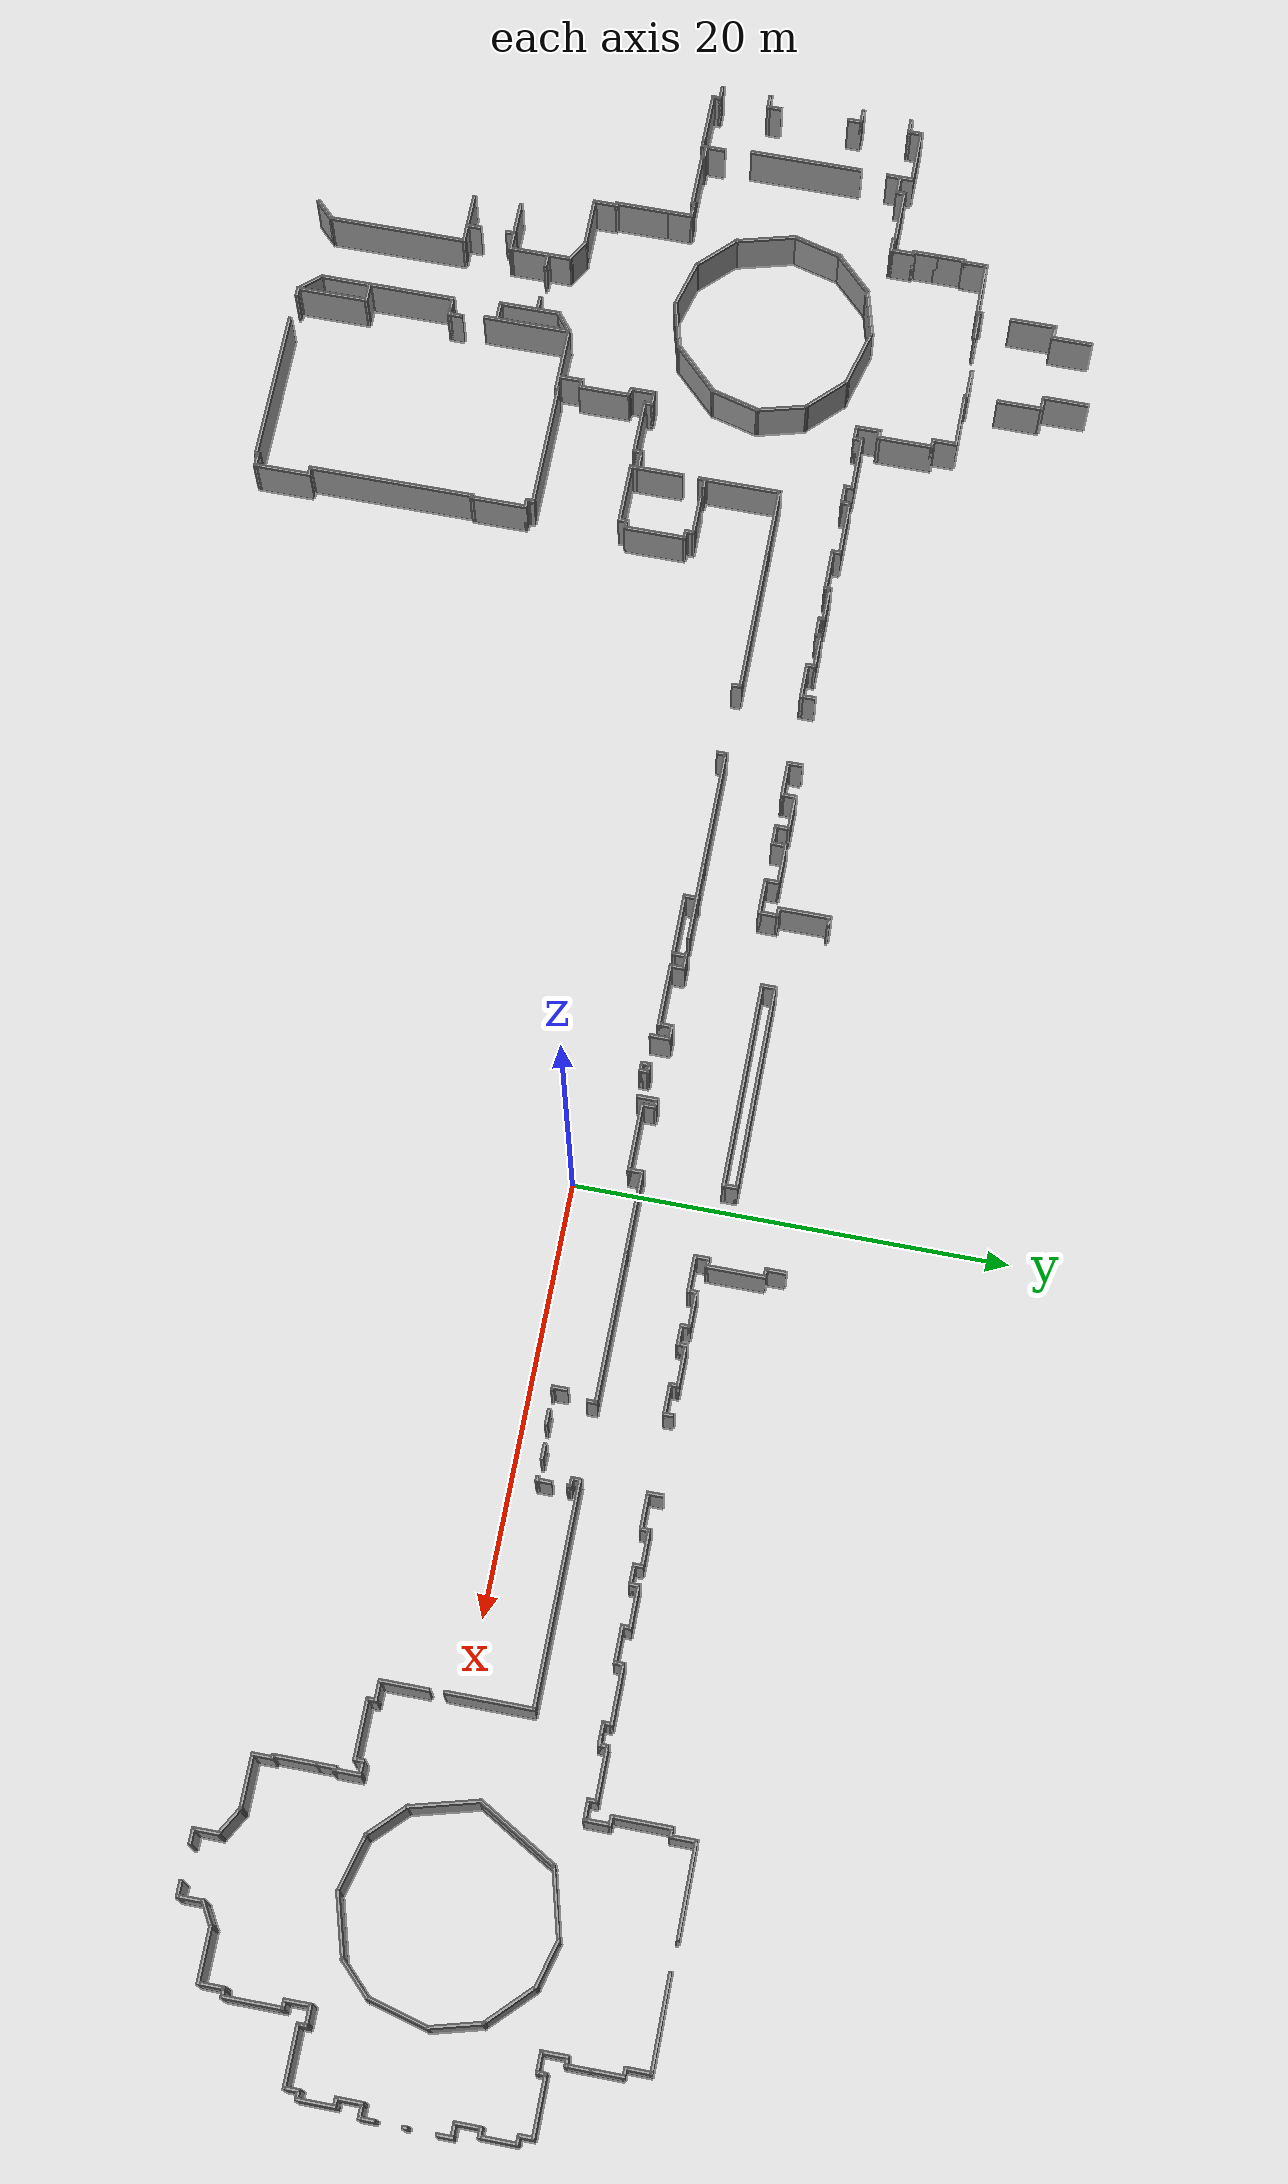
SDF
<?xml version='1.0' encoding='utf-8'?>
<sdf version="1.7">
  <model name="TD_n1_original">
    <pose>-7.14234 -2.45461 0 0 -0 0</pose>
    <link name="Wall_0">
      <collision name="Wall_0_Collision">
        <geometry>
          <box>
            <size>3.25 0.15 2.5</size>
          </box>
        </geometry>
        <pose>0 0 1.25 0 -0 0</pose>
      </collision>
      <visual name="Wall_0_Visual">
        <pose>0 0 1.25 0 -0 0</pose>
        <geometry>
          <box>
            <size>3.25 0.15 2.5</size>
          </box>
        </geometry>
        <material>
          <script>
            <uri>file://media/materials/scripts/gazebo.material</uri>
            <name>Gazebo/Grey</name>
          </script>
          <ambient>1 1 1 1</ambient>
        </material>
        <meta>
          <layer>0</layer>
        </meta>
      </visual>
      <pose>-32.5977 -5.86838 0 0 -0 0</pose>
    </link>
    <link name="Wall_1">
      <collision name="Wall_1_Collision">
        <geometry>
          <box>
            <size>0.25 0.15 2.5</size>
          </box>
        </geometry>
        <pose>0 0 1.25 0 -0 0</pose>
      </collision>
      <visual name="Wall_1_Visual">
        <pose>0 0 1.25 0 -0 0</pose>
        <geometry>
          <box>
            <size>0.25 0.15 2.5</size>
          </box>
        </geometry>
        <material>
          <script>
            <uri>file://media/materials/scripts/gazebo.material</uri>
            <name>Gazebo/Grey</name>
          </script>
          <ambient>1 1 1 1</ambient>
        </material>
        <meta>
          <layer>0</layer>
        </meta>
      </visual>
      <pose>-31.0477 -5.81838 0 0 -0 1.5708</pose>
    </link>
    <link name="Wall_10">
      <collision name="Wall_10_Collision">
        <geometry>
          <box>
            <size>0.5 0.15 2.5</size>
          </box>
        </geometry>
        <pose>0 0 1.25 0 -0 0</pose>
      </collision>
      <visual name="Wall_10_Visual">
        <pose>0 0 1.25 0 -0 0</pose>
        <geometry>
          <box>
            <size>0.5 0.15 2.5</size>
          </box>
        </geometry>
        <material>
          <script>
            <uri>file://media/materials/scripts/gazebo.material</uri>
            <name>Gazebo/Grey</name>
          </script>
          <ambient>1 1 1 1</ambient>
        </material>
        <meta>
          <layer>0</layer>
        </meta>
      </visual>
      <pose>-24.5227 -16.5184 0 0 -0 0</pose>
    </link>
    <link name="Wall_100">
      <collision name="Wall_100_Collision">
        <geometry>
          <box>
            <size>2 0.15 2.5</size>
          </box>
        </geometry>
        <pose>0 0 1.25 0 -0 0</pose>
      </collision>
      <visual name="Wall_100_Visual">
        <pose>0 0 1.25 0 -0 0</pose>
        <geometry>
          <box>
            <size>2 0.15 2.5</size>
          </box>
        </geometry>
        <material>
          <script>
            <uri>file://media/materials/scripts/gazebo.material</uri>
            <name>Gazebo/Grey</name>
          </script>
          <ambient>1 1 1 1</ambient>
        </material>
        <meta>
          <layer>0</layer>
        </meta>
      </visual>
      <pose>-25.6799 1.99288 0 0 -0 3.14159</pose>
    </link>
    <link name="Wall_102">
      <collision name="Wall_102_Collision">
        <geometry>
          <box>
            <size>2.5 0.15 2.5</size>
          </box>
        </geometry>
        <pose>0 0 1.25 0 -0 0</pose>
      </collision>
      <visual name="Wall_102_Visual">
        <pose>0 0 1.25 0 -0 0</pose>
        <geometry>
          <box>
            <size>2.5 0.15 2.5</size>
          </box>
        </geometry>
        <material>
          <script>
            <uri>file://media/materials/scripts/gazebo.material</uri>
            <name>Gazebo/Grey</name>
          </script>
          <ambient>1 1 1 1</ambient>
        </material>
        <meta>
          <layer>0</layer>
        </meta>
      </visual>
      <pose>-37.7105 -0.793001 0 0 -0 2.87979</pose>
    </link>
    <link name="Wall_103">
      <collision name="Wall_103_Collision">
        <geometry>
          <box>
            <size>2.5 0.15 2.5</size>
          </box>
        </geometry>
        <pose>0 0 1.25 0 -0 0</pose>
      </collision>
      <visual name="Wall_103_Visual">
        <pose>0 0 1.25 0 -0 0</pose>
        <geometry>
          <box>
            <size>2.5 0.15 2.5</size>
          </box>
        </geometry>
        <material>
          <script>
            <uri>file://media/materials/scripts/gazebo.material</uri>
            <name>Gazebo/Grey</name>
          </script>
          <ambient>1 1 1 1</ambient>
        </material>
        <meta>
          <layer>0</layer>
        </meta>
      </visual>
      <pose>-39.6763 0.341962 0 0 -0 2.35619</pose>
    </link>
    <link name="Wall_104">
      <collision name="Wall_104_Collision">
        <geometry>
          <box>
            <size>3 0.15 2.5</size>
          </box>
        </geometry>
        <pose>0 0 1.25 0 -0 0</pose>
      </collision>
      <visual name="Wall_104_Visual">
        <pose>0 0 1.25 0 -0 0</pose>
        <geometry>
          <box>
            <size>3 0.15 2.5</size>
          </box>
        </geometry>
        <material>
          <script>
            <uri>file://media/materials/scripts/gazebo.material</uri>
            <name>Gazebo/Grey</name>
          </script>
          <ambient>1 1 1 1</ambient>
        </material>
        <meta>
          <layer>0</layer>
        </meta>
      </visual>
      <pose>-40.876 2.54926 0 0 -0 1.8326</pose>
    </link>
    <link name="Wall_105">
      <collision name="Wall_105_Collision">
        <geometry>
          <box>
            <size>2.5 0.15 2.5</size>
          </box>
        </geometry>
        <pose>0 0 1.25 0 -0 0</pose>
      </collision>
      <visual name="Wall_105_Visual">
        <pose>0 0 1.25 0 -0 0</pose>
        <geometry>
          <box>
            <size>2.5 0.15 2.5</size>
          </box>
        </geometry>
        <material>
          <script>
            <uri>file://media/materials/scripts/gazebo.material</uri>
            <name>Gazebo/Grey</name>
          </script>
          <ambient>1 1 1 1</ambient>
        </material>
        <meta>
          <layer>0</layer>
        </meta>
      </visual>
      <pose>-40.9407 5.06066 0 0 -0 1.309</pose>
    </link>
    <link name="Wall_106">
      <collision name="Wall_106_Collision">
        <geometry>
          <box>
            <size>2.5 0.15 2.5</size>
          </box>
        </geometry>
        <pose>0 0 1.25 0 -0 0</pose>
      </collision>
      <visual name="Wall_106_Visual">
        <pose>0 0 1.25 0 -0 0</pose>
        <geometry>
          <box>
            <size>2.5 0.15 2.5</size>
          </box>
        </geometry>
        <material>
          <script>
            <uri>file://media/materials/scripts/gazebo.material</uri>
            <name>Gazebo/Grey</name>
          </script>
          <ambient>1 1 1 1</ambient>
        </material>
        <meta>
          <layer>0</layer>
        </meta>
      </visual>
      <pose>-39.8057 7.02648 0 0 -0 0.785398</pose>
    </link>
    <link name="Wall_107">
      <collision name="Wall_107_Collision">
        <geometry>
          <box>
            <size>2.5 0.15 2.5</size>
          </box>
        </geometry>
        <pose>0 0 1.25 0 -0 0</pose>
      </collision>
      <visual name="Wall_107_Visual">
        <pose>0 0 1.25 0 -0 0</pose>
        <geometry>
          <box>
            <size>2.5 0.15 2.5</size>
          </box>
        </geometry>
        <material>
          <script>
            <uri>file://media/materials/scripts/gazebo.material</uri>
            <name>Gazebo/Grey</name>
          </script>
          <ambient>1 1 1 1</ambient>
        </material>
        <meta>
          <layer>0</layer>
        </meta>
      </visual>
      <pose>-37.8399 8.16144 0 0 -0 0.261799</pose>
    </link>
    <link name="Wall_108">
      <collision name="Wall_108_Collision">
        <geometry>
          <box>
            <size>3 0.15 2.5</size>
          </box>
        </geometry>
        <pose>0 0 1.25 0 -0 0</pose>
      </collision>
      <visual name="Wall_108_Visual">
        <pose>0 0 1.25 0 -0 0</pose>
        <geometry>
          <box>
            <size>3 0.15 2.5</size>
          </box>
        </geometry>
        <material>
          <script>
            <uri>file://media/materials/scripts/gazebo.material</uri>
            <name>Gazebo/Grey</name>
          </script>
          <ambient>1 1 1 1</ambient>
        </material>
        <meta>
          <layer>0</layer>
        </meta>
      </visual>
      <pose>-35.3285 8.09674 0 0 -0 -0.261799</pose>
    </link>
    <link name="Wall_109">
      <collision name="Wall_109_Collision">
        <geometry>
          <box>
            <size>2.5 0.15 2.5</size>
          </box>
        </geometry>
        <pose>0 0 1.25 0 -0 0</pose>
      </collision>
      <visual name="Wall_109_Visual">
        <pose>0 0 1.25 0 -0 0</pose>
        <geometry>
          <box>
            <size>2.5 0.15 2.5</size>
          </box>
        </geometry>
        <material>
          <script>
            <uri>file://media/materials/scripts/gazebo.material</uri>
            <name>Gazebo/Grey</name>
          </script>
          <ambient>1 1 1 1</ambient>
        </material>
        <meta>
          <layer>0</layer>
        </meta>
      </visual>
      <pose>-33.1212 6.89707 0 0 -0 -0.785398</pose>
    </link>
    <link name="Wall_11">
      <collision name="Wall_11_Collision">
        <geometry>
          <box>
            <size>2.75 0.15 2.5</size>
          </box>
        </geometry>
        <pose>0 0 1.25 0 -0 0</pose>
      </collision>
      <visual name="Wall_11_Visual">
        <pose>0 0 1.25 0 -0 0</pose>
        <geometry>
          <box>
            <size>2.75 0.15 2.5</size>
          </box>
        </geometry>
        <material>
          <script>
            <uri>file://media/materials/scripts/gazebo.material</uri>
            <name>Gazebo/Grey</name>
          </script>
          <ambient>1 1 1 1</ambient>
        </material>
        <meta>
          <layer>0</layer>
        </meta>
      </visual>
      <pose>-24.3477 -17.8184 0 0 -0 -1.5708</pose>
    </link>
    <link name="Wall_110">
      <collision name="Wall_110_Collision">
        <geometry>
          <box>
            <size>2.5 0.15 2.5</size>
          </box>
        </geometry>
        <pose>0 0 1.25 0 -0 0</pose>
      </collision>
      <visual name="Wall_110_Visual">
        <pose>0 0 1.25 0 -0 0</pose>
        <geometry>
          <box>
            <size>2.5 0.15 2.5</size>
          </box>
        </geometry>
        <material>
          <script>
            <uri>file://media/materials/scripts/gazebo.material</uri>
            <name>Gazebo/Grey</name>
          </script>
          <ambient>1 1 1 1</ambient>
        </material>
        <meta>
          <layer>0</layer>
        </meta>
      </visual>
      <pose>-31.9862 4.93125 0 0 -0 -1.309</pose>
    </link>
    <link name="Wall_111">
      <collision name="Wall_111_Collision">
        <geometry>
          <box>
            <size>2.5 0.15 2.5</size>
          </box>
        </geometry>
        <pose>0 0 1.25 0 -0 0</pose>
      </collision>
      <visual name="Wall_111_Visual">
        <pose>0 0 1.25 0 -0 0</pose>
        <geometry>
          <box>
            <size>2.5 0.15 2.5</size>
          </box>
        </geometry>
        <material>
          <script>
            <uri>file://media/materials/scripts/gazebo.material</uri>
            <name>Gazebo/Grey</name>
          </script>
          <ambient>1 1 1 1</ambient>
        </material>
        <meta>
          <layer>0</layer>
        </meta>
      </visual>
      <pose>-31.9862 2.66133 0 0 -0 -1.8326</pose>
    </link>
    <link name="Wall_112">
      <collision name="Wall_112_Collision">
        <geometry>
          <box>
            <size>3 0.15 2.5</size>
          </box>
        </geometry>
        <pose>0 0 1.25 0 -0 0</pose>
      </collision>
      <visual name="Wall_112_Visual">
        <pose>0 0 1.25 0 -0 0</pose>
        <geometry>
          <box>
            <size>3 0.15 2.5</size>
          </box>
        </geometry>
        <material>
          <script>
            <uri>file://media/materials/scripts/gazebo.material</uri>
            <name>Gazebo/Grey</name>
          </script>
          <ambient>1 1 1 1</ambient>
        </material>
        <meta>
          <layer>0</layer>
        </meta>
      </visual>
      <pose>-33.298 0.518739 0 0 -0 -2.35619</pose>
    </link>
    <link name="Wall_113">
      <collision name="Wall_113_Collision">
        <geometry>
          <box>
            <size>2.5 0.15 2.5</size>
          </box>
        </geometry>
        <pose>0 0 1.25 0 -0 0</pose>
      </collision>
      <visual name="Wall_113_Visual">
        <pose>0 0 1.25 0 -0 0</pose>
        <geometry>
          <box>
            <size>2.5 0.15 2.5</size>
          </box>
        </geometry>
        <material>
          <script>
            <uri>file://media/materials/scripts/gazebo.material</uri>
            <name>Gazebo/Grey</name>
          </script>
          <ambient>1 1 1 1</ambient>
        </material>
        <meta>
          <layer>0</layer>
        </meta>
      </visual>
      <pose>-35.4406 -0.793001 0 0 -0 -2.87979</pose>
    </link>
    <link name="Wall_115">
      <collision name="Wall_115_Collision">
        <geometry>
          <box>
            <size>0.75 0.15 2.5</size>
          </box>
        </geometry>
        <pose>0 0 1.25 0 -0 0</pose>
      </collision>
      <visual name="Wall_115_Visual">
        <pose>0 0 1.25 0 -0 0</pose>
        <geometry>
          <box>
            <size>0.75 0.15 2.5</size>
          </box>
        </geometry>
        <material>
          <script>
            <uri>file://media/materials/scripts/gazebo.material</uri>
            <name>Gazebo/Grey</name>
          </script>
          <ambient>1 1 1 1</ambient>
        </material>
        <meta>
          <layer>0</layer>
        </meta>
      </visual>
      <pose>-45.4577 8.08504 0 0 -0 1.5708</pose>
    </link>
    <link name="Wall_116">
      <collision name="Wall_116_Collision">
        <geometry>
          <box>
            <size>1 0.15 2.5</size>
          </box>
        </geometry>
        <pose>0 0 1.25 0 -0 0</pose>
      </collision>
      <visual name="Wall_116_Visual">
        <pose>0 0 1.25 0 -0 0</pose>
        <geometry>
          <box>
            <size>1 0.15 2.5</size>
          </box>
        </geometry>
        <material>
          <script>
            <uri>file://media/materials/scripts/gazebo.material</uri>
            <name>Gazebo/Grey</name>
          </script>
          <ambient>1 1 1 1</ambient>
        </material>
        <meta>
          <layer>0</layer>
        </meta>
      </visual>
      <pose>-45.0327 8.38504 0 0 -0 0</pose>
    </link>
    <link name="Wall_117">
      <collision name="Wall_117_Collision">
        <geometry>
          <box>
            <size>0.5 0.15 2.5</size>
          </box>
        </geometry>
        <pose>0 0 1.25 0 -0 0</pose>
      </collision>
      <visual name="Wall_117_Visual">
        <pose>0 0 1.25 0 -0 0</pose>
        <geometry>
          <box>
            <size>0.5 0.15 2.5</size>
          </box>
        </geometry>
        <material>
          <script>
            <uri>file://media/materials/scripts/gazebo.material</uri>
            <name>Gazebo/Grey</name>
          </script>
          <ambient>1 1 1 1</ambient>
        </material>
        <meta>
          <layer>0</layer>
        </meta>
      </visual>
      <pose>-44.6077 8.56004 0 0 -0 1.5708</pose>
    </link>
    <link name="Wall_118">
      <collision name="Wall_118_Collision">
        <geometry>
          <box>
            <size>2.75 0.15 2.5</size>
          </box>
        </geometry>
        <pose>0 0 1.25 0 -0 0</pose>
      </collision>
      <visual name="Wall_118_Visual">
        <pose>0 0 1.25 0 -0 0</pose>
        <geometry>
          <box>
            <size>2.75 0.15 2.5</size>
          </box>
        </geometry>
        <material>
          <script>
            <uri>file://media/materials/scripts/gazebo.material</uri>
            <name>Gazebo/Grey</name>
          </script>
          <ambient>1 1 1 1</ambient>
        </material>
        <meta>
          <layer>0</layer>
        </meta>
      </visual>
      <pose>-43.3077 8.73504 0 0 -0 0</pose>
    </link>
    <link name="Wall_12">
      <collision name="Wall_12_Collision">
        <geometry>
          <box>
            <size>0.75 0.15 2.5</size>
          </box>
        </geometry>
        <pose>0 0 1.25 0 -0 0</pose>
      </collision>
      <visual name="Wall_12_Visual">
        <pose>0 0 1.25 0 -0 0</pose>
        <geometry>
          <box>
            <size>0.75 0.15 2.5</size>
          </box>
        </geometry>
        <material>
          <script>
            <uri>file://media/materials/scripts/gazebo.material</uri>
            <name>Gazebo/Grey</name>
          </script>
          <ambient>1 1 1 1</ambient>
        </material>
        <meta>
          <layer>0</layer>
        </meta>
      </visual>
      <pose>-24.6477 -19.1184 0 0 -0 3.14159</pose>
    </link>
    <link name="Wall_121">
      <collision name="Wall_121_Collision">
        <geometry>
          <box>
            <size>0.25 0.15 2.5</size>
          </box>
        </geometry>
        <pose>0 0 1.25 0 -0 0</pose>
      </collision>
      <visual name="Wall_121_Visual">
        <pose>0 0 1.25 0 -0 0</pose>
        <geometry>
          <box>
            <size>0.25 0.15 2.5</size>
          </box>
        </geometry>
        <material>
          <script>
            <uri>file://media/materials/scripts/gazebo.material</uri>
            <name>Gazebo/Grey</name>
          </script>
          <ambient>1 1 1 1</ambient>
        </material>
        <meta>
          <layer>0</layer>
        </meta>
      </visual>
      <pose>-42.0077 8.68504 0 0 -0 -1.5708</pose>
    </link>
    <link name="Wall_122">
      <collision name="Wall_122_Collision">
        <geometry>
          <box>
            <size>0.75 0.15 2.5</size>
          </box>
        </geometry>
        <pose>0 0 1.25 0 -0 0</pose>
      </collision>
      <visual name="Wall_122_Visual">
        <pose>0 0 1.25 0 -0 0</pose>
        <geometry>
          <box>
            <size>0.75 0.15 2.5</size>
          </box>
        </geometry>
        <material>
          <script>
            <uri>file://media/materials/scripts/gazebo.material</uri>
            <name>Gazebo/Grey</name>
          </script>
          <ambient>1 1 1 1</ambient>
        </material>
        <meta>
          <layer>0</layer>
        </meta>
      </visual>
      <pose>-41.7077 8.63504 0 0 -0 0</pose>
    </link>
    <link name="Wall_123">
      <collision name="Wall_123_Collision">
        <geometry>
          <box>
            <size>1.25 0.15 2.5</size>
          </box>
        </geometry>
        <pose>0 0 1.25 0 -0 0</pose>
      </collision>
      <visual name="Wall_123_Visual">
        <pose>0 0 1.25 0 -0 0</pose>
        <geometry>
          <box>
            <size>1.25 0.15 2.5</size>
          </box>
        </geometry>
        <material>
          <script>
            <uri>file://media/materials/scripts/gazebo.material</uri>
            <name>Gazebo/Grey</name>
          </script>
          <ambient>1 1 1 1</ambient>
        </material>
        <meta>
          <layer>0</layer>
        </meta>
      </visual>
      <pose>-41.4077 9.18504 0 0 -0 1.5708</pose>
    </link>
    <link name="Wall_124">
      <collision name="Wall_124_Collision">
        <geometry>
          <box>
            <size>0.25 0.15 2.5</size>
          </box>
        </geometry>
        <pose>0 0 1.25 0 -0 0</pose>
      </collision>
      <visual name="Wall_124_Visual">
        <pose>0 0 1.25 0 -0 0</pose>
        <geometry>
          <box>
            <size>0.25 0.15 2.5</size>
          </box>
        </geometry>
        <material>
          <script>
            <uri>file://media/materials/scripts/gazebo.material</uri>
            <name>Gazebo/Grey</name>
          </script>
          <ambient>1 1 1 1</ambient>
        </material>
        <meta>
          <layer>0</layer>
        </meta>
      </visual>
      <pose>-41.4577 9.73504 0 0 -0 3.14159</pose>
    </link>
    <link name="Wall_125">
      <collision name="Wall_125_Collision">
        <geometry>
          <box>
            <size>1.25 0.15 2.5</size>
          </box>
        </geometry>
        <pose>0 0 1.25 0 -0 0</pose>
      </collision>
      <visual name="Wall_125_Visual">
        <pose>0 0 1.25 0 -0 0</pose>
        <geometry>
          <box>
            <size>1.25 0.15 2.5</size>
          </box>
        </geometry>
        <material>
          <script>
            <uri>file://media/materials/scripts/gazebo.material</uri>
            <name>Gazebo/Grey</name>
          </script>
          <ambient>1 1 1 1</ambient>
        </material>
        <meta>
          <layer>0</layer>
        </meta>
      </visual>
      <pose>-41.5077 10.285 0 0 -0 1.5708</pose>
    </link>
    <link name="Wall_127">
      <collision name="Wall_127_Collision">
        <geometry>
          <box>
            <size>1.5 0.15 2.5</size>
          </box>
        </geometry>
        <pose>0 0 1.25 0 -0 0</pose>
      </collision>
      <visual name="Wall_127_Visual">
        <pose>0 0 1.25 0 -0 0</pose>
        <geometry>
          <box>
            <size>1.5 0.15 2.5</size>
          </box>
        </geometry>
        <material>
          <script>
            <uri>file://media/materials/scripts/gazebo.material</uri>
            <name>Gazebo/Grey</name>
          </script>
          <ambient>1 1 1 1</ambient>
        </material>
        <meta>
          <layer>0</layer>
        </meta>
      </visual>
      <pose>-41.5077 11.51 0 0 -0 1.5708</pose>
    </link>
    <link name="Wall_128">
      <collision name="Wall_128_Collision">
        <geometry>
          <box>
            <size>0.25 0.15 2.5</size>
          </box>
        </geometry>
        <pose>0 0 1.25 0 -0 0</pose>
      </collision>
      <visual name="Wall_128_Visual">
        <pose>0 0 1.25 0 -0 0</pose>
        <geometry>
          <box>
            <size>0.25 0.15 2.5</size>
          </box>
        </geometry>
        <material>
          <script>
            <uri>file://media/materials/scripts/gazebo.material</uri>
            <name>Gazebo/Grey</name>
          </script>
          <ambient>1 1 1 1</ambient>
        </material>
        <meta>
          <layer>0</layer>
        </meta>
      </visual>
      <pose>-41.4577 12.185 0 0 -0 0</pose>
    </link>
    <link name="Wall_129">
      <collision name="Wall_129_Collision">
        <geometry>
          <box>
            <size>1.25 0.15 2.5</size>
          </box>
        </geometry>
        <pose>0 0 1.25 0 -0 0</pose>
      </collision>
      <visual name="Wall_129_Visual">
        <pose>0 0 1.25 0 -0 0</pose>
        <geometry>
          <box>
            <size>1.25 0.15 2.5</size>
          </box>
        </geometry>
        <material>
          <script>
            <uri>file://media/materials/scripts/gazebo.material</uri>
            <name>Gazebo/Grey</name>
          </script>
          <ambient>1 1 1 1</ambient>
        </material>
        <meta>
          <layer>0</layer>
        </meta>
      </visual>
      <pose>-41.4077 12.735 0 0 -0 1.5708</pose>
    </link>
    <link name="Wall_13">
      <collision name="Wall_13_Collision">
        <geometry>
          <box>
            <size>0.25 0.15 2.5</size>
          </box>
        </geometry>
        <pose>0 0 1.25 0 -0 0</pose>
      </collision>
      <visual name="Wall_13_Visual">
        <pose>0 0 1.25 0 -0 0</pose>
        <geometry>
          <box>
            <size>0.25 0.15 2.5</size>
          </box>
        </geometry>
        <material>
          <script>
            <uri>file://media/materials/scripts/gazebo.material</uri>
            <name>Gazebo/Grey</name>
          </script>
          <ambient>1 1 1 1</ambient>
        </material>
        <meta>
          <layer>0</layer>
        </meta>
      </visual>
      <pose>-24.9477 -19.1684 0 0 -0 -1.5708</pose>
    </link>
    <link name="Wall_130">
      <collision name="Wall_130_Collision">
        <geometry>
          <box>
            <size>2.75 0.15 2.5</size>
          </box>
        </geometry>
        <pose>0 0 1.25 0 -0 0</pose>
      </collision>
      <visual name="Wall_130_Visual">
        <pose>0 0 1.25 0 -0 0</pose>
        <geometry>
          <box>
            <size>2.75 0.15 2.5</size>
          </box>
        </geometry>
        <material>
          <script>
            <uri>file://media/materials/scripts/gazebo.material</uri>
            <name>Gazebo/Grey</name>
          </script>
          <ambient>1 1 1 1</ambient>
        </material>
        <meta>
          <layer>0</layer>
        </meta>
      </visual>
      <pose>-40.1077 13.285 0 0 -0 0</pose>
    </link>
    <link name="Wall_131">
      <collision name="Wall_131_Collision">
        <geometry>
          <box>
            <size>0.25 0.15 2.5</size>
          </box>
        </geometry>
        <pose>0 0 1.25 0 -0 0</pose>
      </collision>
      <visual name="Wall_131_Visual">
        <pose>0 0 1.25 0 -0 0</pose>
        <geometry>
          <box>
            <size>0.25 0.15 2.5</size>
          </box>
        </geometry>
        <material>
          <script>
            <uri>file://media/materials/scripts/gazebo.material</uri>
            <name>Gazebo/Grey</name>
          </script>
          <ambient>1 1 1 1</ambient>
        </material>
        <meta>
          <layer>0</layer>
        </meta>
      </visual>
      <pose>-38.8077 13.335 0 0 -0 1.5708</pose>
    </link>
    <link name="Wall_132">
      <collision name="Wall_132_Collision">
        <geometry>
          <box>
            <size>1.5 0.15 2.5</size>
          </box>
        </geometry>
        <pose>0 0 1.25 0 -0 0</pose>
      </collision>
      <visual name="Wall_132_Visual">
        <pose>0 0 1.25 0 -0 0</pose>
        <geometry>
          <box>
            <size>1.5 0.15 2.5</size>
          </box>
        </geometry>
        <material>
          <script>
            <uri>file://media/materials/scripts/gazebo.material</uri>
            <name>Gazebo/Grey</name>
          </script>
          <ambient>1 1 1 1</ambient>
        </material>
        <meta>
          <layer>0</layer>
        </meta>
      </visual>
      <pose>-38.1327 13.385 0 0 -0 0</pose>
    </link>
    <link name="Wall_134">
      <collision name="Wall_134_Collision">
        <geometry>
          <box>
            <size>1.5 0.15 2.5</size>
          </box>
        </geometry>
        <pose>0 0 1.25 0 -0 0</pose>
      </collision>
      <visual name="Wall_134_Visual">
        <pose>0 0 1.25 0 -0 0</pose>
        <geometry>
          <box>
            <size>1.5 0.15 2.5</size>
          </box>
        </geometry>
        <material>
          <script>
            <uri>file://media/materials/scripts/gazebo.material</uri>
            <name>Gazebo/Grey</name>
          </script>
          <ambient>1 1 1 1</ambient>
        </material>
        <meta>
          <layer>0</layer>
        </meta>
      </visual>
      <pose>-34.9371 13.5314 0 0 -0 0</pose>
    </link>
    <link name="Wall_135">
      <collision name="Wall_135_Collision">
        <geometry>
          <box>
            <size>0.25 0.15 2.5</size>
          </box>
        </geometry>
        <pose>0 0 1.25 0 -0 0</pose>
      </collision>
      <visual name="Wall_135_Visual">
        <pose>0 0 1.25 0 -0 0</pose>
        <geometry>
          <box>
            <size>0.25 0.15 2.5</size>
          </box>
        </geometry>
        <material>
          <script>
            <uri>file://media/materials/scripts/gazebo.material</uri>
            <name>Gazebo/Grey</name>
          </script>
          <ambient>1 1 1 1</ambient>
        </material>
        <meta>
          <layer>0</layer>
        </meta>
      </visual>
      <pose>-34.2621 13.4814 0 0 -0 -1.5708</pose>
    </link>
    <link name="Wall_136">
      <collision name="Wall_136_Collision">
        <geometry>
          <box>
            <size>2.75 0.15 2.5</size>
          </box>
        </geometry>
        <pose>0 0 1.25 0 -0 0</pose>
      </collision>
      <visual name="Wall_136_Visual">
        <pose>0 0 1.25 0 -0 0</pose>
        <geometry>
          <box>
            <size>2.75 0.15 2.5</size>
          </box>
        </geometry>
        <material>
          <script>
            <uri>file://media/materials/scripts/gazebo.material</uri>
            <name>Gazebo/Grey</name>
          </script>
          <ambient>1 1 1 1</ambient>
        </material>
        <meta>
          <layer>0</layer>
        </meta>
      </visual>
      <pose>-32.9621 13.4314 0 0 -0 0</pose>
    </link>
    <link name="Wall_137">
      <collision name="Wall_137_Collision">
        <geometry>
          <box>
            <size>1.25 0.15 2.5</size>
          </box>
        </geometry>
        <pose>0 0 1.25 0 -0 0</pose>
      </collision>
      <visual name="Wall_137_Visual">
        <pose>0 0 1.25 0 -0 0</pose>
        <geometry>
          <box>
            <size>1.25 0.15 2.5</size>
          </box>
        </geometry>
        <material>
          <script>
            <uri>file://media/materials/scripts/gazebo.material</uri>
            <name>Gazebo/Grey</name>
          </script>
          <ambient>1 1 1 1</ambient>
        </material>
        <meta>
          <layer>0</layer>
        </meta>
      </visual>
      <pose>-31.6621 12.8814 0 0 -0 -1.5708</pose>
    </link>
    <link name="Wall_138">
      <collision name="Wall_138_Collision">
        <geometry>
          <box>
            <size>0.5 0.15 2.5</size>
          </box>
        </geometry>
        <pose>0 0 1.25 0 -0 0</pose>
      </collision>
      <visual name="Wall_138_Visual">
        <pose>0 0 1.25 0 -0 0</pose>
        <geometry>
          <box>
            <size>0.5 0.15 2.5</size>
          </box>
        </geometry>
        <material>
          <script>
            <uri>file://media/materials/scripts/gazebo.material</uri>
            <name>Gazebo/Grey</name>
          </script>
          <ambient>1 1 1 1</ambient>
        </material>
        <meta>
          <layer>0</layer>
        </meta>
      </visual>
      <pose>-31.4871 12.3314 0 0 -0 0</pose>
    </link>
    <link name="Wall_139">
      <collision name="Wall_139_Collision">
        <geometry>
          <box>
            <size>2.75 0.15 2.5</size>
          </box>
        </geometry>
        <pose>0 0 1.25 0 -0 0</pose>
      </collision>
      <visual name="Wall_139_Visual">
        <pose>0 0 1.25 0 -0 0</pose>
        <geometry>
          <box>
            <size>2.75 0.15 2.5</size>
          </box>
        </geometry>
        <material>
          <script>
            <uri>file://media/materials/scripts/gazebo.material</uri>
            <name>Gazebo/Grey</name>
          </script>
          <ambient>1 1 1 1</ambient>
        </material>
        <meta>
          <layer>0</layer>
        </meta>
      </visual>
      <pose>-31.3121 11.0314 0 0 -0 -1.5708</pose>
    </link>
    <link name="Wall_14">
      <collision name="Wall_14_Collision">
        <geometry>
          <box>
            <size>7.5 0.15 2.5</size>
          </box>
        </geometry>
        <pose>0 0 1.25 0 -0 0</pose>
      </collision>
      <visual name="Wall_14_Visual">
        <pose>0 0 1.25 0 -0 0</pose>
        <geometry>
          <box>
            <size>7.5 0.15 2.5</size>
          </box>
        </geometry>
        <material>
          <script>
            <uri>file://media/materials/scripts/gazebo.material</uri>
            <name>Gazebo/Grey</name>
          </script>
          <ambient>1 1 1 1</ambient>
        </material>
        <meta>
          <layer>0</layer>
        </meta>
      </visual>
      <pose>-28.6227 -19.2184 0 0 -0 3.14159</pose>
    </link>
    <link name="Wall_141">
      <collision name="Wall_141_Collision">
        <geometry>
          <box>
            <size>0.5 0.15 2.5</size>
          </box>
        </geometry>
        <pose>0 0 1.25 0 -0 0</pose>
      </collision>
      <visual name="Wall_141_Visual">
        <pose>0 0 1.25 0 -0 0</pose>
        <geometry>
          <box>
            <size>0.5 0.15 2.5</size>
          </box>
        </geometry>
        <material>
          <script>
            <uri>file://media/materials/scripts/gazebo.material</uri>
            <name>Gazebo/Grey</name>
          </script>
          <ambient>1 1 1 1</ambient>
        </material>
        <meta>
          <layer>0</layer>
        </meta>
      </visual>
      <pose>-31.4871 9.73136 0 0 -0 3.14159</pose>
    </link>
    <link name="Wall_142">
      <collision name="Wall_142_Collision">
        <geometry>
          <box>
            <size>1.25 0.15 2.5</size>
          </box>
        </geometry>
        <pose>0 0 1.25 0 -0 0</pose>
      </collision>
      <visual name="Wall_142_Visual">
        <pose>0 0 1.25 0 -0 0</pose>
        <geometry>
          <box>
            <size>1.25 0.15 2.5</size>
          </box>
        </geometry>
        <material>
          <script>
            <uri>file://media/materials/scripts/gazebo.material</uri>
            <name>Gazebo/Grey</name>
          </script>
          <ambient>1 1 1 1</ambient>
        </material>
        <meta>
          <layer>0</layer>
        </meta>
      </visual>
      <pose>-31.6621 9.18136 0 0 -0 -1.5708</pose>
    </link>
    <link name="Wall_143">
      <collision name="Wall_143_Collision">
        <geometry>
          <box>
            <size>0.75 0.15 2.5</size>
          </box>
        </geometry>
        <pose>0 0 1.25 0 -0 0</pose>
      </collision>
      <visual name="Wall_143_Visual">
        <pose>0 0 1.25 0 -0 0</pose>
        <geometry>
          <box>
            <size>0.75 0.15 2.5</size>
          </box>
        </geometry>
        <material>
          <script>
            <uri>file://media/materials/scripts/gazebo.material</uri>
            <name>Gazebo/Grey</name>
          </script>
          <ambient>1 1 1 1</ambient>
        </material>
        <meta>
          <layer>0</layer>
        </meta>
      </visual>
      <pose>-31.3621 8.63136 0 0 -0 0</pose>
    </link>
    <link name="Wall_144">
      <collision name="Wall_144_Collision">
        <geometry>
          <box>
            <size>0.5 0.15 2.5</size>
          </box>
        </geometry>
        <pose>0 0 1.25 0 -0 0</pose>
      </collision>
      <visual name="Wall_144_Visual">
        <pose>0 0 1.25 0 -0 0</pose>
        <geometry>
          <box>
            <size>0.5 0.15 2.5</size>
          </box>
        </geometry>
        <material>
          <script>
            <uri>file://media/materials/scripts/gazebo.material</uri>
            <name>Gazebo/Grey</name>
          </script>
          <ambient>1 1 1 1</ambient>
        </material>
        <meta>
          <layer>0</layer>
        </meta>
      </visual>
      <pose>-31.0621 8.80636 0 0 -0 1.5708</pose>
    </link>
    <link name="Wall_145">
      <collision name="Wall_145_Collision">
        <geometry>
          <box>
            <size>2.75 0.15 2.5</size>
          </box>
        </geometry>
        <pose>0 0 1.25 0 -0 0</pose>
      </collision>
      <visual name="Wall_145_Visual">
        <pose>0 0 1.25 0 -0 0</pose>
        <geometry>
          <box>
            <size>2.75 0.15 2.5</size>
          </box>
        </geometry>
        <material>
          <script>
            <uri>file://media/materials/scripts/gazebo.material</uri>
            <name>Gazebo/Grey</name>
          </script>
          <ambient>1 1 1 1</ambient>
        </material>
        <meta>
          <layer>0</layer>
        </meta>
      </visual>
      <pose>-29.7621 8.98136 0 0 -0 0</pose>
    </link>
    <link name="Wall_146">
      <collision name="Wall_146_Collision">
        <geometry>
          <box>
            <size>0.5 0.15 2.5</size>
          </box>
        </geometry>
        <pose>0 0 1.25 0 -0 0</pose>
      </collision>
      <visual name="Wall_146_Visual">
        <pose>0 0 1.25 0 -0 0</pose>
        <geometry>
          <box>
            <size>0.5 0.15 2.5</size>
          </box>
        </geometry>
        <material>
          <script>
            <uri>file://media/materials/scripts/gazebo.material</uri>
            <name>Gazebo/Grey</name>
          </script>
          <ambient>1 1 1 1</ambient>
        </material>
        <meta>
          <layer>0</layer>
        </meta>
      </visual>
      <pose>-28.4621 8.80636 0 0 -0 -1.5708</pose>
    </link>
    <link name="Wall_147">
      <collision name="Wall_147_Collision">
        <geometry>
          <box>
            <size>1 0.15 2.5</size>
          </box>
        </geometry>
        <pose>0 0 1.25 0 -0 0</pose>
      </collision>
      <visual name="Wall_147_Visual">
        <pose>0 0 1.25 0 -0 0</pose>
        <geometry>
          <box>
            <size>1 0.15 2.5</size>
          </box>
        </geometry>
        <material>
          <script>
            <uri>file://media/materials/scripts/gazebo.material</uri>
            <name>Gazebo/Grey</name>
          </script>
          <ambient>1 1 1 1</ambient>
        </material>
        <meta>
          <layer>0</layer>
        </meta>
      </visual>
      <pose>-28.0371 8.63136 0 0 -0 0</pose>
    </link>
    <link name="Wall_148">
      <collision name="Wall_148_Collision">
        <geometry>
          <box>
            <size>0.5 0.15 2.5</size>
          </box>
        </geometry>
        <pose>0 0 1.25 0 -0 0</pose>
      </collision>
      <visual name="Wall_148_Visual">
        <pose>0 0 1.25 0 -0 0</pose>
        <geometry>
          <box>
            <size>0.5 0.15 2.5</size>
          </box>
        </geometry>
        <material>
          <script>
            <uri>file://media/materials/scripts/gazebo.material</uri>
            <name>Gazebo/Grey</name>
          </script>
          <ambient>1 1 1 1</ambient>
        </material>
        <meta>
          <layer>0</layer>
        </meta>
      </visual>
      <pose>-27.6121 8.80636 0 0 -0 1.5708</pose>
    </link>
    <link name="Wall_149">
      <collision name="Wall_149_Collision">
        <geometry>
          <box>
            <size>2.75 0.15 2.5</size>
          </box>
        </geometry>
        <pose>0 0 1.25 0 -0 0</pose>
      </collision>
      <visual name="Wall_149_Visual">
        <pose>0 0 1.25 0 -0 0</pose>
        <geometry>
          <box>
            <size>2.75 0.15 2.5</size>
          </box>
        </geometry>
        <material>
          <script>
            <uri>file://media/materials/scripts/gazebo.material</uri>
            <name>Gazebo/Grey</name>
          </script>
          <ambient>1 1 1 1</ambient>
        </material>
        <meta>
          <layer>0</layer>
        </meta>
      </visual>
      <pose>-26.3121 8.98136 0 0 -0 0</pose>
    </link>
    <link name="Wall_150">
      <collision name="Wall_150_Collision">
        <geometry>
          <box>
            <size>0.5 0.15 2.5</size>
          </box>
        </geometry>
        <pose>0 0 1.25 0 -0 0</pose>
      </collision>
      <visual name="Wall_150_Visual">
        <pose>0 0 1.25 0 -0 0</pose>
        <geometry>
          <box>
            <size>0.5 0.15 2.5</size>
          </box>
        </geometry>
        <material>
          <script>
            <uri>file://media/materials/scripts/gazebo.material</uri>
            <name>Gazebo/Grey</name>
          </script>
          <ambient>1 1 1 1</ambient>
        </material>
        <meta>
          <layer>0</layer>
        </meta>
      </visual>
      <pose>-25.0121 8.80636 0 0 -0 -1.5708</pose>
    </link>
    <link name="Wall_151">
      <collision name="Wall_151_Collision">
        <geometry>
          <box>
            <size>1.75 0.15 2.5</size>
          </box>
        </geometry>
        <pose>0 0 1.25 0 -0 0</pose>
      </collision>
      <visual name="Wall_151_Visual">
        <pose>0 0 1.25 0 -0 0</pose>
        <geometry>
          <box>
            <size>1.75 0.15 2.5</size>
          </box>
        </geometry>
        <material>
          <script>
            <uri>file://media/materials/scripts/gazebo.material</uri>
            <name>Gazebo/Grey</name>
          </script>
          <ambient>1 1 1 1</ambient>
        </material>
        <meta>
          <layer>0</layer>
        </meta>
      </visual>
      <pose>-24.2121 8.63136 0 0 -0 0</pose>
    </link>
    <link name="Wall_152">
      <collision name="Wall_152_Collision">
        <geometry>
          <box>
            <size>0.5 0.15 2.5</size>
          </box>
        </geometry>
        <pose>0 0 1.25 0 -0 0</pose>
      </collision>
      <visual name="Wall_152_Visual">
        <pose>0 0 1.25 0 -0 0</pose>
        <geometry>
          <box>
            <size>0.5 0.15 2.5</size>
          </box>
        </geometry>
        <material>
          <script>
            <uri>file://media/materials/scripts/gazebo.material</uri>
            <name>Gazebo/Grey</name>
          </script>
          <ambient>1 1 1 1</ambient>
        </material>
        <meta>
          <layer>0</layer>
        </meta>
      </visual>
      <pose>-23.2371 8.63136 0 0 -0 0</pose>
    </link>
    <link name="Wall_153">
      <collision name="Wall_153_Collision">
        <geometry>
          <box>
            <size>0.25 0.15 2.5</size>
          </box>
        </geometry>
        <pose>0 0 1.25 0 -0 0</pose>
      </collision>
      <visual name="Wall_153_Visual">
        <pose>0 0 1.25 0 -0 0</pose>
        <geometry>
          <box>
            <size>0.25 0.15 2.5</size>
          </box>
        </geometry>
        <material>
          <script>
            <uri>file://media/materials/scripts/gazebo.material</uri>
            <name>Gazebo/Grey</name>
          </script>
          <ambient>1 1 1 1</ambient>
        </material>
        <meta>
          <layer>0</layer>
        </meta>
      </visual>
      <pose>-23.0751 8.67966 0 0 -0 1.8326</pose>
    </link>
    <link name="Wall_154">
      <collision name="Wall_154_Collision">
        <geometry>
          <box>
            <size>0.25 0.15 2.5</size>
          </box>
        </geometry>
        <pose>0 0 1.25 0 -0 0</pose>
      </collision>
      <visual name="Wall_154_Visual">
        <pose>0 0 1.25 0 -0 0</pose>
        <geometry>
          <box>
            <size>0.25 0.15 2.5</size>
          </box>
        </geometry>
        <material>
          <script>
            <uri>file://media/materials/scripts/gazebo.material</uri>
            <name>Gazebo/Grey</name>
          </script>
          <ambient>1 1 1 1</ambient>
        </material>
        <meta>
          <layer>0</layer>
        </meta>
      </visual>
      <pose>-23.088 8.77796 0 0 -0 1.5708</pose>
    </link>
    <link name="Wall_155">
      <collision name="Wall_155_Collision">
        <geometry>
          <box>
            <size>1.75 0.15 2.5</size>
          </box>
        </geometry>
        <pose>0 0 1.25 0 -0 0</pose>
      </collision>
      <visual name="Wall_155_Visual">
        <pose>0 0 1.25 0 -0 0</pose>
        <geometry>
          <box>
            <size>1.75 0.15 2.5</size>
          </box>
        </geometry>
        <material>
          <script>
            <uri>file://media/materials/scripts/gazebo.material</uri>
            <name>Gazebo/Grey</name>
          </script>
          <ambient>1 1 1 1</ambient>
        </material>
        <meta>
          <layer>0</layer>
        </meta>
      </visual>
      <pose>-22.288 8.82795 0 0 -0 0</pose>
    </link>
    <link name="Wall_157">
      <collision name="Wall_157_Collision">
        <geometry>
          <box>
            <size>0.25 0.15 2.5</size>
          </box>
        </geometry>
        <pose>0 0 1.25 0 -0 0</pose>
      </collision>
      <visual name="Wall_157_Visual">
        <pose>0 0 1.25 0 -0 0</pose>
        <geometry>
          <box>
            <size>0.25 0.15 2.5</size>
          </box>
        </geometry>
        <material>
          <script>
            <uri>file://media/materials/scripts/gazebo.material</uri>
            <name>Gazebo/Grey</name>
          </script>
          <ambient>1 1 1 1</ambient>
        </material>
        <meta>
          <layer>0</layer>
        </meta>
      </visual>
      <pose>-38.8077 13.435 0 0 -0 1.5708</pose>
    </link>
    <link name="Wall_159">
      <collision name="Wall_159_Collision">
        <geometry>
          <box>
            <size>2.25 0.15 2.5</size>
          </box>
        </geometry>
        <pose>0 0 1.25 0 -0 0</pose>
      </collision>
      <visual name="Wall_159_Visual">
        <pose>0 0 1.25 0 -0 0</pose>
        <geometry>
          <box>
            <size>2.25 0.15 2.5</size>
          </box>
        </geometry>
        <material>
          <script>
            <uri>file://media/materials/scripts/gazebo.material</uri>
            <name>Gazebo/Grey</name>
          </script>
          <ambient>1 1 1 1</ambient>
        </material>
        <meta>
          <layer>0</layer>
        </meta>
      </visual>
      <pose>-38.7414 16.0283 0 0 -0 1.5708</pose>
    </link>
    <link name="Wall_16">
      <collision name="Wall_16_Collision">
        <geometry>
          <box>
            <size>0.5 0.15 2.5</size>
          </box>
        </geometry>
        <pose>0 0 1.25 0 -0 0</pose>
      </collision>
      <visual name="Wall_16_Visual">
        <pose>0 0 1.25 0 -0 0</pose>
        <geometry>
          <box>
            <size>0.5 0.15 2.5</size>
          </box>
        </geometry>
        <material>
          <script>
            <uri>file://media/materials/scripts/gazebo.material</uri>
            <name>Gazebo/Grey</name>
          </script>
          <ambient>1 1 1 1</ambient>
        </material>
        <meta>
          <layer>0</layer>
        </meta>
      </visual>
      <pose>-33.8173 -19.1685 0 0 -0 3.14159</pose>
    </link>
    <link name="Wall_160">
      <collision name="Wall_160_Collision">
        <geometry>
          <box>
            <size>0.75 0.15 2.5</size>
          </box>
        </geometry>
        <pose>0 0 1.25 0 -0 0</pose>
      </collision>
      <visual name="Wall_160_Visual">
        <pose>0 0 1.25 0 -0 0</pose>
        <geometry>
          <box>
            <size>0.75 0.15 2.5</size>
          </box>
        </geometry>
        <material>
          <script>
            <uri>file://media/materials/scripts/gazebo.material</uri>
            <name>Gazebo/Grey</name>
          </script>
          <ambient>1 1 1 1</ambient>
        </material>
        <meta>
          <layer>0</layer>
        </meta>
      </visual>
      <pose>-38.4414 17.0783 0 0 -0 0</pose>
    </link>
    <link name="Wall_161">
      <collision name="Wall_161_Collision">
        <geometry>
          <box>
            <size>2 0.15 2.5</size>
          </box>
        </geometry>
        <pose>0 0 1.25 0 -0 0</pose>
      </collision>
      <visual name="Wall_161_Visual">
        <pose>0 0 1.25 0 -0 0</pose>
        <geometry>
          <box>
            <size>2 0.15 2.5</size>
          </box>
        </geometry>
        <material>
          <script>
            <uri>file://media/materials/scripts/gazebo.material</uri>
            <name>Gazebo/Grey</name>
          </script>
          <ambient>1 1 1 1</ambient>
        </material>
        <meta>
          <layer>0</layer>
        </meta>
      </visual>
      <pose>-38.1414 18.0033 0 0 -0 1.5708</pose>
    </link>
    <link name="Wall_163">
      <collision name="Wall_163_Collision">
        <geometry>
          <box>
            <size>2.25 0.15 2.5</size>
          </box>
        </geometry>
        <pose>0 0 1.25 0 -0 0</pose>
      </collision>
      <visual name="Wall_163_Visual">
        <pose>0 0 1.25 0 -0 0</pose>
        <geometry>
          <box>
            <size>2.25 0.15 2.5</size>
          </box>
        </geometry>
        <material>
          <script>
            <uri>file://media/materials/scripts/gazebo.material</uri>
            <name>Gazebo/Grey</name>
          </script>
          <ambient>1 1 1 1</ambient>
        </material>
        <meta>
          <layer>0</layer>
        </meta>
      </visual>
      <pose>-34.2815 16.0983 0 0 -0 1.5708</pose>
    </link>
    <link name="Wall_164">
      <collision name="Wall_164_Collision">
        <geometry>
          <box>
            <size>0.75 0.15 2.5</size>
          </box>
        </geometry>
        <pose>0 0 1.25 0 -0 0</pose>
      </collision>
      <visual name="Wall_164_Visual">
        <pose>0 0 1.25 0 -0 0</pose>
        <geometry>
          <box>
            <size>0.75 0.15 2.5</size>
          </box>
        </geometry>
        <material>
          <script>
            <uri>file://media/materials/scripts/gazebo.material</uri>
            <name>Gazebo/Grey</name>
          </script>
          <ambient>1 1 1 1</ambient>
        </material>
        <meta>
          <layer>0</layer>
        </meta>
      </visual>
      <pose>-34.5815 17.1483 0 0 -0 3.14159</pose>
    </link>
    <link name="Wall_165">
      <collision name="Wall_165_Collision">
        <geometry>
          <box>
            <size>2.25 0.15 2.5</size>
          </box>
        </geometry>
        <pose>0 0 1.25 0 -0 0</pose>
      </collision>
      <visual name="Wall_165_Visual">
        <pose>0 0 1.25 0 -0 0</pose>
        <geometry>
          <box>
            <size>2.25 0.15 2.5</size>
          </box>
        </geometry>
        <material>
          <script>
            <uri>file://media/materials/scripts/gazebo.material</uri>
            <name>Gazebo/Grey</name>
          </script>
          <ambient>1 1 1 1</ambient>
        </material>
        <meta>
          <layer>0</layer>
        </meta>
      </visual>
      <pose>-34.8815 18.1983 0 0 -0 1.5708</pose>
    </link>
    <link name="Wall_167">
      <collision name="Wall_167_Collision">
        <geometry>
          <box>
            <size>0.75 0.15 2.5</size>
          </box>
        </geometry>
        <pose>0 0 1.25 0 -0 0</pose>
      </collision>
      <visual name="Wall_167_Visual">
        <pose>0 0 1.25 0 -0 0</pose>
        <geometry>
          <box>
            <size>0.75 0.15 2.5</size>
          </box>
        </geometry>
        <material>
          <script>
            <uri>file://media/materials/scripts/gazebo.material</uri>
            <name>Gazebo/Grey</name>
          </script>
          <ambient>1 1 1 1</ambient>
        </material>
        <meta>
          <layer>0</layer>
        </meta>
      </visual>
      <pose>-45.4577 8.68504 0 0 -0 1.5708</pose>
    </link>
    <link name="Wall_168">
      <collision name="Wall_168_Collision">
        <geometry>
          <box>
            <size>2.75 0.15 2.5</size>
          </box>
        </geometry>
        <pose>0 0 1.25 0 -0 0</pose>
      </collision>
      <visual name="Wall_168_Visual">
        <pose>0 0 1.25 0 -0 0</pose>
        <geometry>
          <box>
            <size>2.75 0.15 2.5</size>
          </box>
        </geometry>
        <material>
          <script>
            <uri>file://media/materials/scripts/gazebo.material</uri>
            <name>Gazebo/Grey</name>
          </script>
          <ambient>1 1 1 1</ambient>
        </material>
        <meta>
          <layer>0</layer>
        </meta>
      </visual>
      <pose>-46.7577 8.98504 0 0 -0 3.14159</pose>
    </link>
    <link name="Wall_169">
      <collision name="Wall_169_Collision">
        <geometry>
          <box>
            <size>0.75 0.15 2.5</size>
          </box>
        </geometry>
        <pose>0 0 1.25 0 -0 0</pose>
      </collision>
      <visual name="Wall_169_Visual">
        <pose>0 0 1.25 0 -0 0</pose>
        <geometry>
          <box>
            <size>0.75 0.15 2.5</size>
          </box>
        </geometry>
        <material>
          <script>
            <uri>file://media/materials/scripts/gazebo.material</uri>
            <name>Gazebo/Grey</name>
          </script>
          <ambient>1 1 1 1</ambient>
        </material>
        <meta>
          <layer>0</layer>
        </meta>
      </visual>
      <pose>-48.0577 8.68504 0 0 -0 -1.5708</pose>
    </link>
    <link name="Wall_17">
      <collision name="Wall_17_Collision">
        <geometry>
          <box>
            <size>3.5 0.15 2.5</size>
          </box>
        </geometry>
        <pose>0 0 1.25 0 -0 0</pose>
      </collision>
      <visual name="Wall_17_Visual">
        <pose>0 0 1.25 0 -0 0</pose>
        <geometry>
          <box>
            <size>3.5 0.15 2.5</size>
          </box>
        </geometry>
        <material>
          <script>
            <uri>file://media/materials/scripts/gazebo.material</uri>
            <name>Gazebo/Grey</name>
          </script>
          <ambient>1 1 1 1</ambient>
        </material>
        <meta>
          <layer>0</layer>
        </meta>
      </visual>
      <pose>-33.9923 -17.4935 0 0 -0 1.5708</pose>
    </link>
    <link name="Wall_171">
      <collision name="Wall_171_Collision">
        <geometry>
          <box>
            <size>0.75 0.15 2.5</size>
          </box>
        </geometry>
        <pose>0 0 1.25 0 -0 0</pose>
      </collision>
      <visual name="Wall_171_Visual">
        <pose>0 0 1.25 0 -0 0</pose>
        <geometry>
          <box>
            <size>0.75 0.15 2.5</size>
          </box>
        </geometry>
        <material>
          <script>
            <uri>file://media/materials/scripts/gazebo.material</uri>
            <name>Gazebo/Grey</name>
          </script>
          <ambient>1 1 1 1</ambient>
        </material>
        <meta>
          <layer>0</layer>
        </meta>
      </visual>
      <pose>-48.3577 8.38504 0 0 -0 3.14159</pose>
    </link>
    <link name="Wall_173">
      <collision name="Wall_173_Collision">
        <geometry>
          <box>
            <size>0.75 0.15 2.5</size>
          </box>
        </geometry>
        <pose>0 0 1.25 0 -0 0</pose>
      </collision>
      <visual name="Wall_173_Visual">
        <pose>0 0 1.25 0 -0 0</pose>
        <geometry>
          <box>
            <size>0.75 0.15 2.5</size>
          </box>
        </geometry>
        <material>
          <script>
            <uri>file://media/materials/scripts/gazebo.material</uri>
            <name>Gazebo/Grey</name>
          </script>
          <ambient>1 1 1 1</ambient>
        </material>
        <meta>
          <layer>0</layer>
        </meta>
      </visual>
      <pose>-48.478 5.98707 0 0 -0 0</pose>
    </link>
    <link name="Wall_174">
      <collision name="Wall_174_Collision">
        <geometry>
          <box>
            <size>0.75 0.15 2.5</size>
          </box>
        </geometry>
        <pose>0 0 1.25 0 -0 0</pose>
      </collision>
      <visual name="Wall_174_Visual">
        <pose>0 0 1.25 0 -0 0</pose>
        <geometry>
          <box>
            <size>0.75 0.15 2.5</size>
          </box>
        </geometry>
        <material>
          <script>
            <uri>file://media/materials/scripts/gazebo.material</uri>
            <name>Gazebo/Grey</name>
          </script>
          <ambient>1 1 1 1</ambient>
        </material>
        <meta>
          <layer>0</layer>
        </meta>
      </visual>
      <pose>-48.178 5.68707 0 0 -0 -1.5708</pose>
    </link>
    <link name="Wall_176">
      <collision name="Wall_176_Collision">
        <geometry>
          <box>
            <size>0.75 0.15 2.5</size>
          </box>
        </geometry>
        <pose>0 0 1.25 0 -0 0</pose>
      </collision>
      <visual name="Wall_176_Visual">
        <pose>0 0 1.25 0 -0 0</pose>
        <geometry>
          <box>
            <size>0.75 0.15 2.5</size>
          </box>
        </geometry>
        <material>
          <script>
            <uri>file://media/materials/scripts/gazebo.material</uri>
            <name>Gazebo/Grey</name>
          </script>
          <ambient>1 1 1 1</ambient>
        </material>
        <meta>
          <layer>0</layer>
        </meta>
      </visual>
      <pose>-48.1484 1.64687 0 0 -0 -1.5708</pose>
    </link>
    <link name="Wall_177">
      <collision name="Wall_177_Collision">
        <geometry>
          <box>
            <size>0.75 0.15 2.5</size>
          </box>
        </geometry>
        <pose>0 0 1.25 0 -0 0</pose>
      </collision>
      <visual name="Wall_177_Visual">
        <pose>0 0 1.25 0 -0 0</pose>
        <geometry>
          <box>
            <size>0.75 0.15 2.5</size>
          </box>
        </geometry>
        <material>
          <script>
            <uri>file://media/materials/scripts/gazebo.material</uri>
            <name>Gazebo/Grey</name>
          </script>
          <ambient>1 1 1 1</ambient>
        </material>
        <meta>
          <layer>0</layer>
        </meta>
      </visual>
      <pose>-48.4484 1.34686 0 0 -0 3.14159</pose>
    </link>
    <link name="Wall_179">
      <collision name="Wall_179_Collision">
        <geometry>
          <box>
            <size>0.75 0.15 2.5</size>
          </box>
        </geometry>
        <pose>0 0 1.25 0 -0 0</pose>
      </collision>
      <visual name="Wall_179_Visual">
        <pose>0 0 1.25 0 -0 0</pose>
        <geometry>
          <box>
            <size>0.75 0.15 2.5</size>
          </box>
        </geometry>
        <material>
          <script>
            <uri>file://media/materials/scripts/gazebo.material</uri>
            <name>Gazebo/Grey</name>
          </script>
          <ambient>1 1 1 1</ambient>
        </material>
        <meta>
          <layer>0</layer>
        </meta>
      </visual>
      <pose>-48.4955 -1.06143 0 0 -0 0</pose>
    </link>
    <link name="Wall_18">
      <collision name="Wall_18_Collision">
        <geometry>
          <box>
            <size>1 0.15 2.5</size>
          </box>
        </geometry>
        <pose>0 0 1.25 0 -0 0</pose>
      </collision>
      <visual name="Wall_18_Visual">
        <pose>0 0 1.25 0 -0 0</pose>
        <geometry>
          <box>
            <size>1 0.15 2.5</size>
          </box>
        </geometry>
        <material>
          <script>
            <uri>file://media/materials/scripts/gazebo.material</uri>
            <name>Gazebo/Grey</name>
          </script>
          <ambient>1 1 1 1</ambient>
        </material>
        <meta>
          <layer>0</layer>
        </meta>
      </visual>
      <pose>-34.4173 -15.8185 0 0 -0 3.14159</pose>
    </link>
    <link name="Wall_180">
      <collision name="Wall_180_Collision">
        <geometry>
          <box>
            <size>0.5 0.15 2.5</size>
          </box>
        </geometry>
        <pose>0 0 1.25 0 -0 0</pose>
      </collision>
      <visual name="Wall_180_Visual">
        <pose>0 0 1.25 0 -0 0</pose>
        <geometry>
          <box>
            <size>0.5 0.15 2.5</size>
          </box>
        </geometry>
        <material>
          <script>
            <uri>file://media/materials/scripts/gazebo.material</uri>
            <name>Gazebo/Grey</name>
          </script>
          <ambient>1 1 1 1</ambient>
        </material>
        <meta>
          <layer>0</layer>
        </meta>
      </visual>
      <pose>-48.1955 -1.23643 0 0 -0 -1.5708</pose>
    </link>
    <link name="Wall_181">
      <collision name="Wall_181_Collision">
        <geometry>
          <box>
            <size>2.63697 0.15 2.5</size>
          </box>
        </geometry>
        <pose>0 0 1.25 0 -0 0</pose>
      </collision>
      <visual name="Wall_181_Visual">
        <pose>0 0 1.25 0 -0 0</pose>
        <geometry>
          <box>
            <size>2.63697 0.15 2.5</size>
          </box>
        </geometry>
        <material>
          <script>
            <uri>file://media/materials/scripts/gazebo.material</uri>
            <name>Gazebo/Grey</name>
          </script>
          <ambient>1 1 1 1</ambient>
        </material>
        <meta>
          <layer>0</layer>
        </meta>
      </visual>
      <pose>-46.952 -1.41577 0 0 -0 -0.003496</pose>
    </link>
    <link name="Wall_183">
      <collision name="Wall_183_Collision">
        <geometry>
          <box>
            <size>0.5 0.15 2.5</size>
          </box>
        </geometry>
        <pose>0 0 1.25 0 -0 0</pose>
      </collision>
      <visual name="Wall_183_Visual">
        <pose>0 0 1.25 0 -0 0</pose>
        <geometry>
          <box>
            <size>0.5 0.15 2.5</size>
          </box>
        </geometry>
        <material>
          <script>
            <uri>file://media/materials/scripts/gazebo.material</uri>
            <name>Gazebo/Grey</name>
          </script>
          <ambient>1 1 1 1</ambient>
        </material>
        <meta>
          <layer>0</layer>
        </meta>
      </visual>
      <pose>-45.5292 -1.42012 0 0 -0 0</pose>
    </link>
    <link name="Wall_185">
      <collision name="Wall_185_Collision">
        <geometry>
          <box>
            <size>0.347693 0.15 2.5</size>
          </box>
        </geometry>
        <pose>0 0 1.25 0 -0 0</pose>
      </collision>
      <visual name="Wall_185_Visual">
        <pose>0 0 1.25 0 -0 0</pose>
        <geometry>
          <box>
            <size>0.347693 0.15 2.5</size>
          </box>
        </geometry>
        <material>
          <script>
            <uri>file://media/materials/scripts/gazebo.material</uri>
            <name>Gazebo/Grey</name>
          </script>
          <ambient>1 1 1 1</ambient>
        </material>
        <meta>
          <layer>0</layer>
        </meta>
      </visual>
      <pose>-45.3589 -1.32128 0 0 -0 1.57458</pose>
    </link>
    <link name="Wall_187">
      <collision name="Wall_187_Collision">
        <geometry>
          <box>
            <size>1.75 0.15 2.5</size>
          </box>
        </geometry>
        <pose>0 0 1.25 0 -0 0</pose>
      </collision>
      <visual name="Wall_187_Visual">
        <pose>0 0 1.25 0 -0 0</pose>
        <geometry>
          <box>
            <size>1.75 0.15 2.5</size>
          </box>
        </geometry>
        <material>
          <script>
            <uri>file://media/materials/scripts/gazebo.material</uri>
            <name>Gazebo/Grey</name>
          </script>
          <ambient>1 1 1 1</ambient>
        </material>
        <meta>
          <layer>0</layer>
        </meta>
      </visual>
      <pose>-39.7095 -11.8394 0 0 -0 3.14159</pose>
    </link>
    <link name="Wall_189">
      <collision name="Wall_189_Collision">
        <geometry>
          <box>
            <size>1.75 0.15 2.5</size>
          </box>
        </geometry>
        <pose>0 0 1.25 0 -0 0</pose>
      </collision>
      <visual name="Wall_189_Visual">
        <pose>0 0 1.25 0 -0 0</pose>
        <geometry>
          <box>
            <size>1.75 0.15 2.5</size>
          </box>
        </geometry>
        <material>
          <script>
            <uri>file://media/materials/scripts/gazebo.material</uri>
            <name>Gazebo/Grey</name>
          </script>
          <ambient>1 1 1 1</ambient>
        </material>
        <meta>
          <layer>0</layer>
        </meta>
      </visual>
      <pose>-39.7067 -9.52243 0 0 -0 3.14159</pose>
    </link>
    <link name="Wall_19">
      <collision name="Wall_19_Collision">
        <geometry>
          <box>
            <size>2.5 0.15 2.5</size>
          </box>
        </geometry>
        <pose>0 0 1.25 0 -0 0</pose>
      </collision>
      <visual name="Wall_19_Visual">
        <pose>0 0 1.25 0 -0 0</pose>
        <geometry>
          <box>
            <size>2.5 0.15 2.5</size>
          </box>
        </geometry>
        <material>
          <script>
            <uri>file://media/materials/scripts/gazebo.material</uri>
            <name>Gazebo/Grey</name>
          </script>
          <ambient>1 1 1 1</ambient>
        </material>
        <meta>
          <layer>0</layer>
        </meta>
      </visual>
      <pose>-34.8423 -16.9935 0 0 -0 -1.5708</pose>
    </link>
    <link name="Wall_191">
      <collision name="Wall_191_Collision">
        <geometry>
          <box>
            <size>0.25 0.15 2.5</size>
          </box>
        </geometry>
        <pose>0 0 1.25 0 -0 0</pose>
      </collision>
      <visual name="Wall_191_Visual">
        <pose>0 0 1.25 0 -0 0</pose>
        <geometry>
          <box>
            <size>0.25 0.15 2.5</size>
          </box>
        </geometry>
        <material>
          <script>
            <uri>file://media/materials/scripts/gazebo.material</uri>
            <name>Gazebo/Grey</name>
          </script>
          <ambient>1 1 1 1</ambient>
        </material>
        <meta>
          <layer>0</layer>
        </meta>
      </visual>
      <pose>-21.488 8.77796 0 0 -0 -1.5708</pose>
    </link>
    <link name="Wall_192">
      <collision name="Wall_192_Collision">
        <geometry>
          <box>
            <size>0.25 0.15 2.5</size>
          </box>
        </geometry>
        <pose>0 0 1.25 0 -0 0</pose>
      </collision>
      <visual name="Wall_192_Visual">
        <pose>0 0 1.25 0 -0 0</pose>
        <geometry>
          <box>
            <size>0.25 0.15 2.5</size>
          </box>
        </geometry>
        <material>
          <script>
            <uri>file://media/materials/scripts/gazebo.material</uri>
            <name>Gazebo/Grey</name>
          </script>
          <ambient>1 1 1 1</ambient>
        </material>
        <meta>
          <layer>0</layer>
        </meta>
      </visual>
      <pose>-21.488 8.67796 0 0 -0 -1.5708</pose>
    </link>
    <link name="Wall_193">
      <collision name="Wall_193_Collision">
        <geometry>
          <box>
            <size>1 0.15 2.5</size>
          </box>
        </geometry>
        <pose>0 0 1.25 0 -0 0</pose>
      </collision>
      <visual name="Wall_193_Visual">
        <pose>0 0 1.25 0 -0 0</pose>
        <geometry>
          <box>
            <size>1 0.15 2.5</size>
          </box>
        </geometry>
        <material>
          <script>
            <uri>file://media/materials/scripts/gazebo.material</uri>
            <name>Gazebo/Grey</name>
          </script>
          <ambient>1 1 1 1</ambient>
        </material>
        <meta>
          <layer>0</layer>
        </meta>
      </visual>
      <pose>-21.063 8.62796 0 0 -0 0</pose>
    </link>
    <link name="Wall_194">
      <collision name="Wall_194_Collision">
        <geometry>
          <box>
            <size>0.25 0.15 2.5</size>
          </box>
        </geometry>
        <pose>0 0 1.25 0 -0 0</pose>
      </collision>
      <visual name="Wall_194_Visual">
        <pose>0 0 1.25 0 -0 0</pose>
        <geometry>
          <box>
            <size>0.25 0.15 2.5</size>
          </box>
        </geometry>
        <material>
          <script>
            <uri>file://media/materials/scripts/gazebo.material</uri>
            <name>Gazebo/Grey</name>
          </script>
          <ambient>1 1 1 1</ambient>
        </material>
        <meta>
          <layer>0</layer>
        </meta>
      </visual>
      <pose>-20.638 8.67796 0 0 -0 1.5708</pose>
    </link>
    <link name="Wall_195">
      <collision name="Wall_195_Collision">
        <geometry>
          <box>
            <size>0.25 0.15 2.5</size>
          </box>
        </geometry>
        <pose>0 0 1.25 0 -0 0</pose>
      </collision>
      <visual name="Wall_195_Visual">
        <pose>0 0 1.25 0 -0 0</pose>
        <geometry>
          <box>
            <size>0.25 0.15 2.5</size>
          </box>
        </geometry>
        <material>
          <script>
            <uri>file://media/materials/scripts/gazebo.material</uri>
            <name>Gazebo/Grey</name>
          </script>
          <ambient>1 1 1 1</ambient>
        </material>
        <meta>
          <layer>0</layer>
        </meta>
      </visual>
      <pose>-20.638 8.77796 0 0 -0 1.5708</pose>
    </link>
    <link name="Wall_196">
      <collision name="Wall_196_Collision">
        <geometry>
          <box>
            <size>1.75 0.15 2.5</size>
          </box>
        </geometry>
        <pose>0 0 1.25 0 -0 0</pose>
      </collision>
      <visual name="Wall_196_Visual">
        <pose>0 0 1.25 0 -0 0</pose>
        <geometry>
          <box>
            <size>1.75 0.15 2.5</size>
          </box>
        </geometry>
        <material>
          <script>
            <uri>file://media/materials/scripts/gazebo.material</uri>
            <name>Gazebo/Grey</name>
          </script>
          <ambient>1 1 1 1</ambient>
        </material>
        <meta>
          <layer>0</layer>
        </meta>
      </visual>
      <pose>-19.838 8.82795 0 0 -0 0</pose>
    </link>
    <link name="Wall_197">
      <collision name="Wall_197_Collision">
        <geometry>
          <box>
            <size>0.5 0.15 2.5</size>
          </box>
        </geometry>
        <pose>0 0 1.25 0 -0 0</pose>
      </collision>
      <visual name="Wall_197_Visual">
        <pose>0 0 1.25 0 -0 0</pose>
        <geometry>
          <box>
            <size>0.5 0.15 2.5</size>
          </box>
        </geometry>
        <material>
          <script>
            <uri>file://media/materials/scripts/gazebo.material</uri>
            <name>Gazebo/Grey</name>
          </script>
          <ambient>1 1 1 1</ambient>
        </material>
        <meta>
          <layer>0</layer>
        </meta>
      </visual>
      <pose>-19.038 8.65296 0 0 -0 -1.5708</pose>
    </link>
    <link name="Wall_198">
      <collision name="Wall_198_Collision">
        <geometry>
          <box>
            <size>1.75 0.15 2.5</size>
          </box>
        </geometry>
        <pose>0 0 1.25 0 -0 0</pose>
      </collision>
      <visual name="Wall_198_Visual">
        <pose>0 0 1.25 0 -0 0</pose>
        <geometry>
          <box>
            <size>1.75 0.15 2.5</size>
          </box>
        </geometry>
        <material>
          <script>
            <uri>file://media/materials/scripts/gazebo.material</uri>
            <name>Gazebo/Grey</name>
          </script>
          <ambient>1 1 1 1</ambient>
        </material>
        <meta>
          <layer>0</layer>
        </meta>
      </visual>
      <pose>-18.238 8.47795 0 0 -0 0</pose>
    </link>
    <link name="Wall_199">
      <collision name="Wall_199_Collision">
        <geometry>
          <box>
            <size>0.75 0.15 2.5</size>
          </box>
        </geometry>
        <pose>0 0 1.25 0 -0 0</pose>
      </collision>
      <visual name="Wall_199_Visual">
        <pose>0 0 1.25 0 -0 0</pose>
        <geometry>
          <box>
            <size>0.75 0.15 2.5</size>
          </box>
        </geometry>
        <material>
          <script>
            <uri>file://media/materials/scripts/gazebo.material</uri>
            <name>Gazebo/Grey</name>
          </script>
          <ambient>1 1 1 1</ambient>
        </material>
        <meta>
          <layer>0</layer>
        </meta>
      </visual>
      <pose>-17.438 8.77796 0 0 -0 1.5708</pose>
    </link>
    <link name="Wall_2">
      <collision name="Wall_2_Collision">
        <geometry>
          <box>
            <size>6.25 0.15 2.5</size>
          </box>
        </geometry>
        <pose>0 0 1.25 0 -0 0</pose>
      </collision>
      <visual name="Wall_2_Visual">
        <pose>0 0 1.25 0 -0 0</pose>
        <geometry>
          <box>
            <size>6.25 0.15 2.5</size>
          </box>
        </geometry>
        <material>
          <script>
            <uri>file://media/materials/scripts/gazebo.material</uri>
            <name>Gazebo/Grey</name>
          </script>
          <ambient>1 1 1 1</ambient>
        </material>
        <meta>
          <layer>0</layer>
        </meta>
      </visual>
      <pose>-27.9977 -5.76838 0 0 -0 0</pose>
    </link>
    <link name="Wall_20">
      <collision name="Wall_20_Collision">
        <geometry>
          <box>
            <size>1.46244 0.15 2.5</size>
          </box>
        </geometry>
        <pose>0 0 1.25 0 -0 0</pose>
      </collision>
      <visual name="Wall_20_Visual">
        <pose>0 0 1.25 0 -0 0</pose>
        <geometry>
          <box>
            <size>1.46244 0.15 2.5</size>
          </box>
        </geometry>
        <material>
          <script>
            <uri>file://media/materials/scripts/gazebo.material</uri>
            <name>Gazebo/Grey</name>
          </script>
          <ambient>1 1 1 1</ambient>
        </material>
        <meta>
          <layer>0</layer>
        </meta>
      </visual>
      <pose>-34.4173 -18.6685 0 0 -0 -0.866302</pose>
    </link>
    <link name="Wall_201">
      <collision name="Wall_201_Collision">
        <geometry>
          <box>
            <size>7 0.15 2.5</size>
          </box>
        </geometry>
        <pose>0 0 1.25 0 -0 0</pose>
      </collision>
      <visual name="Wall_201_Visual">
        <pose>0 0 1.25 0 -0 0</pose>
        <geometry>
          <box>
            <size>7 0.15 2.5</size>
          </box>
        </geometry>
        <material>
          <script>
            <uri>file://media/materials/scripts/gazebo.material</uri>
            <name>Gazebo/Grey</name>
          </script>
          <ambient>1 1 1 1</ambient>
        </material>
        <meta>
          <layer>0</layer>
        </meta>
      </visual>
      <pose>-20.8208 5.61227 0 0 -0 0</pose>
    </link>
    <link name="Wall_202">
      <collision name="Wall_202_Collision">
        <geometry>
          <box>
            <size>0.5 0.15 2.5</size>
          </box>
        </geometry>
        <pose>0 0 1.25 0 -0 0</pose>
      </collision>
      <visual name="Wall_202_Visual">
        <pose>0 0 1.25 0 -0 0</pose>
        <geometry>
          <box>
            <size>0.5 0.15 2.5</size>
          </box>
        </geometry>
        <material>
          <script>
            <uri>file://media/materials/scripts/gazebo.material</uri>
            <name>Gazebo/Grey</name>
          </script>
          <ambient>1 1 1 1</ambient>
        </material>
        <meta>
          <layer>0</layer>
        </meta>
      </visual>
      <pose>-17.3958 5.43727 0 0 -0 -1.5708</pose>
    </link>
    <link name="Wall_204">
      <collision name="Wall_204_Collision">
        <geometry>
          <box>
            <size>0.5 0.15 2.5</size>
          </box>
        </geometry>
        <pose>0 0 1.25 0 -0 0</pose>
      </collision>
      <visual name="Wall_204_Visual">
        <pose>0 0 1.25 0 -0 0</pose>
        <geometry>
          <box>
            <size>0.5 0.15 2.5</size>
          </box>
        </geometry>
        <material>
          <script>
            <uri>file://media/materials/scripts/gazebo.material</uri>
            <name>Gazebo/Grey</name>
          </script>
          <ambient>1 1 1 1</ambient>
        </material>
        <meta>
          <layer>0</layer>
        </meta>
      </visual>
      <pose>-13.8967 5.37703 0 0 -0 1.5708</pose>
    </link>
    <link name="Wall_205">
      <collision name="Wall_205_Collision">
        <geometry>
          <box>
            <size>5.75 0.15 2.5</size>
          </box>
        </geometry>
        <pose>0 0 1.25 0 -0 0</pose>
      </collision>
      <visual name="Wall_205_Visual">
        <pose>0 0 1.25 0 -0 0</pose>
        <geometry>
          <box>
            <size>5.75 0.15 2.5</size>
          </box>
        </geometry>
        <material>
          <script>
            <uri>file://media/materials/scripts/gazebo.material</uri>
            <name>Gazebo/Grey</name>
          </script>
          <ambient>1 1 1 1</ambient>
        </material>
        <meta>
          <layer>0</layer>
        </meta>
      </visual>
      <pose>-11.0967 5.55204 0 0 -0 0</pose>
    </link>
    <link name="Wall_207">
      <collision name="Wall_207_Collision">
        <geometry>
          <box>
            <size>0.75 0.15 2.5</size>
          </box>
        </geometry>
        <pose>0 0 1.25 0 -0 0</pose>
      </collision>
      <visual name="Wall_207_Visual">
        <pose>0 0 1.25 0 -0 0</pose>
        <geometry>
          <box>
            <size>0.75 0.15 2.5</size>
          </box>
        </geometry>
        <material>
          <script>
            <uri>file://media/materials/scripts/gazebo.material</uri>
            <name>Gazebo/Grey</name>
          </script>
          <ambient>1 1 1 1</ambient>
        </material>
        <meta>
          <layer>0</layer>
        </meta>
      </visual>
      <pose>-14.0008 8.78798 0 0 -0 -1.5708</pose>
    </link>
    <link name="Wall_208">
      <collision name="Wall_208_Collision">
        <geometry>
          <box>
            <size>1.75 0.15 2.5</size>
          </box>
        </geometry>
        <pose>0 0 1.25 0 -0 0</pose>
      </collision>
      <visual name="Wall_208_Visual">
        <pose>0 0 1.25 0 -0 0</pose>
        <geometry>
          <box>
            <size>1.75 0.15 2.5</size>
          </box>
        </geometry>
        <material>
          <script>
            <uri>file://media/materials/scripts/gazebo.material</uri>
            <name>Gazebo/Grey</name>
          </script>
          <ambient>1 1 1 1</ambient>
        </material>
        <meta>
          <layer>0</layer>
        </meta>
      </visual>
      <pose>-13.2008 8.48798 0 0 -0 0</pose>
    </link>
    <link name="Wall_209">
      <collision name="Wall_209_Collision">
        <geometry>
          <box>
            <size>0.75 0.15 2.5</size>
          </box>
        </geometry>
        <pose>0 0 1.25 0 -0 0</pose>
      </collision>
      <visual name="Wall_209_Visual">
        <pose>0 0 1.25 0 -0 0</pose>
        <geometry>
          <box>
            <size>0.75 0.15 2.5</size>
          </box>
        </geometry>
        <material>
          <script>
            <uri>file://media/materials/scripts/gazebo.material</uri>
            <name>Gazebo/Grey</name>
          </script>
          <ambient>1 1 1 1</ambient>
        </material>
        <meta>
          <layer>0</layer>
        </meta>
      </visual>
      <pose>-12.4008 8.78798 0 0 -0 1.5708</pose>
    </link>
    <link name="Wall_210">
      <collision name="Wall_210_Collision">
        <geometry>
          <box>
            <size>1.75 0.15 2.5</size>
          </box>
        </geometry>
        <pose>0 0 1.25 0 -0 0</pose>
      </collision>
      <visual name="Wall_210_Visual">
        <pose>0 0 1.25 0 -0 0</pose>
        <geometry>
          <box>
            <size>1.75 0.15 2.5</size>
          </box>
        </geometry>
        <material>
          <script>
            <uri>file://media/materials/scripts/gazebo.material</uri>
            <name>Gazebo/Grey</name>
          </script>
          <ambient>1 1 1 1</ambient>
        </material>
        <meta>
          <layer>0</layer>
        </meta>
      </visual>
      <pose>-11.6008 9.08798 0 0 -0 0</pose>
    </link>
    <link name="Wall_211">
      <collision name="Wall_211_Collision">
        <geometry>
          <box>
            <size>0.75 0.15 2.5</size>
          </box>
        </geometry>
        <pose>0 0 1.25 0 -0 0</pose>
      </collision>
      <visual name="Wall_211_Visual">
        <pose>0 0 1.25 0 -0 0</pose>
        <geometry>
          <box>
            <size>0.75 0.15 2.5</size>
          </box>
        </geometry>
        <material>
          <script>
            <uri>file://media/materials/scripts/gazebo.material</uri>
            <name>Gazebo/Grey</name>
          </script>
          <ambient>1 1 1 1</ambient>
        </material>
        <meta>
          <layer>0</layer>
        </meta>
      </visual>
      <pose>-10.8008 8.78798 0 0 -0 -1.5708</pose>
    </link>
    <link name="Wall_212">
      <collision name="Wall_212_Collision">
        <geometry>
          <box>
            <size>1 0.15 2.5</size>
          </box>
        </geometry>
        <pose>0 0 1.25 0 -0 0</pose>
      </collision>
      <visual name="Wall_212_Visual">
        <pose>0 0 1.25 0 -0 0</pose>
        <geometry>
          <box>
            <size>1 0.15 2.5</size>
          </box>
        </geometry>
        <material>
          <script>
            <uri>file://media/materials/scripts/gazebo.material</uri>
            <name>Gazebo/Grey</name>
          </script>
          <ambient>1 1 1 1</ambient>
        </material>
        <meta>
          <layer>0</layer>
        </meta>
      </visual>
      <pose>-10.3758 8.48798 0 0 -0 0</pose>
    </link>
    <link name="Wall_213">
      <collision name="Wall_213_Collision">
        <geometry>
          <box>
            <size>0.75 0.15 2.5</size>
          </box>
        </geometry>
        <pose>0 0 1.25 0 -0 0</pose>
      </collision>
      <visual name="Wall_213_Visual">
        <pose>0 0 1.25 0 -0 0</pose>
        <geometry>
          <box>
            <size>0.75 0.15 2.5</size>
          </box>
        </geometry>
        <material>
          <script>
            <uri>file://media/materials/scripts/gazebo.material</uri>
            <name>Gazebo/Grey</name>
          </script>
          <ambient>1 1 1 1</ambient>
        </material>
        <meta>
          <layer>0</layer>
        </meta>
      </visual>
      <pose>-9.95077 8.78798 0 0 -0 1.5708</pose>
    </link>
    <link name="Wall_214">
      <collision name="Wall_214_Collision">
        <geometry>
          <box>
            <size>2 0.15 2.5</size>
          </box>
        </geometry>
        <pose>0 0 1.25 0 -0 0</pose>
      </collision>
      <visual name="Wall_214_Visual">
        <pose>0 0 1.25 0 -0 0</pose>
        <geometry>
          <box>
            <size>2 0.15 2.5</size>
          </box>
        </geometry>
        <material>
          <script>
            <uri>file://media/materials/scripts/gazebo.material</uri>
            <name>Gazebo/Grey</name>
          </script>
          <ambient>1 1 1 1</ambient>
        </material>
        <meta>
          <layer>0</layer>
        </meta>
      </visual>
      <pose>-9.02577 9.08798 0 0 -0 0</pose>
    </link>
    <link name="Wall_215">
      <collision name="Wall_215_Collision">
        <geometry>
          <box>
            <size>0.75 0.15 2.5</size>
          </box>
        </geometry>
        <pose>0 0 1.25 0 -0 0</pose>
      </collision>
      <visual name="Wall_215_Visual">
        <pose>0 0 1.25 0 -0 0</pose>
        <geometry>
          <box>
            <size>0.75 0.15 2.5</size>
          </box>
        </geometry>
        <material>
          <script>
            <uri>file://media/materials/scripts/gazebo.material</uri>
            <name>Gazebo/Grey</name>
          </script>
          <ambient>1 1 1 1</ambient>
        </material>
        <meta>
          <layer>0</layer>
        </meta>
      </visual>
      <pose>-8.10077 8.78798 0 0 -0 -1.5708</pose>
    </link>
    <link name="Wall_216">
      <collision name="Wall_216_Collision">
        <geometry>
          <box>
            <size>1.75 0.15 2.5</size>
          </box>
        </geometry>
        <pose>0 0 1.25 0 -0 0</pose>
      </collision>
      <visual name="Wall_216_Visual">
        <pose>0 0 1.25 0 -0 0</pose>
        <geometry>
          <box>
            <size>1.75 0.15 2.5</size>
          </box>
        </geometry>
        <material>
          <script>
            <uri>file://media/materials/scripts/gazebo.material</uri>
            <name>Gazebo/Grey</name>
          </script>
          <ambient>1 1 1 1</ambient>
        </material>
        <meta>
          <layer>0</layer>
        </meta>
      </visual>
      <pose>-7.30077 8.48798 0 0 -0 0</pose>
    </link>
    <link name="Wall_218">
      <collision name="Wall_218_Collision">
        <geometry>
          <box>
            <size>3.75 0.15 2.5</size>
          </box>
        </geometry>
        <pose>0 0 1.25 0 -0 0</pose>
      </collision>
      <visual name="Wall_218_Visual">
        <pose>0 0 1.25 0 -0 0</pose>
        <geometry>
          <box>
            <size>3.75 0.15 2.5</size>
          </box>
        </geometry>
        <material>
          <script>
            <uri>file://media/materials/scripts/gazebo.material</uri>
            <name>Gazebo/Grey</name>
          </script>
          <ambient>1 1 1 1</ambient>
        </material>
        <meta>
          <layer>0</layer>
        </meta>
      </visual>
      <pose>-6.49668 5.55204 0 0 -0 0</pose>
    </link>
    <link name="Wall_22">
      <collision name="Wall_22_Collision">
        <geometry>
          <box>
            <size>4.25 0.15 2.5</size>
          </box>
        </geometry>
        <pose>0 0 1.25 0 -0 0</pose>
      </collision>
      <visual name="Wall_22_Visual">
        <pose>0 0 1.25 0 -0 0</pose>
        <geometry>
          <box>
            <size>4.25 0.15 2.5</size>
          </box>
        </geometry>
        <material>
          <script>
            <uri>file://media/materials/scripts/gazebo.material</uri>
            <name>Gazebo/Grey</name>
          </script>
          <ambient>1 1 1 1</ambient>
        </material>
        <meta>
          <layer>0</layer>
        </meta>
      </visual>
      <pose>-34.8423 -13.7685 0 0 -0 1.5708</pose>
    </link>
    <link name="Wall_220">
      <collision name="Wall_220_Collision">
        <geometry>
          <box>
            <size>0.75 0.15 2.5</size>
          </box>
        </geometry>
        <pose>0 0 1.25 0 -0 0</pose>
      </collision>
      <visual name="Wall_220_Visual">
        <pose>0 0 1.25 0 -0 0</pose>
        <geometry>
          <box>
            <size>0.75 0.15 2.5</size>
          </box>
        </geometry>
        <material>
          <script>
            <uri>file://media/materials/scripts/gazebo.material</uri>
            <name>Gazebo/Grey</name>
          </script>
          <ambient>1 1 1 1</ambient>
        </material>
        <meta>
          <layer>0</layer>
        </meta>
      </visual>
      <pose>-6.6568 5.29526 0 0 -0 -1.5708</pose>
    </link>
    <link name="Wall_221">
      <collision name="Wall_221_Collision">
        <geometry>
          <box>
            <size>3 0.15 2.5</size>
          </box>
        </geometry>
        <pose>0 0 1.25 0 -0 0</pose>
      </collision>
      <visual name="Wall_221_Visual">
        <pose>0 0 1.25 0 -0 0</pose>
        <geometry>
          <box>
            <size>3 0.15 2.5</size>
          </box>
        </geometry>
        <material>
          <script>
            <uri>file://media/materials/scripts/gazebo.material</uri>
            <name>Gazebo/Grey</name>
          </script>
          <ambient>1 1 1 1</ambient>
        </material>
        <meta>
          <layer>0</layer>
        </meta>
      </visual>
      <pose>-5.2318 4.99526 0 0 -0 0</pose>
    </link>
    <link name="Wall_222">
      <collision name="Wall_222_Collision">
        <geometry>
          <box>
            <size>0.75 0.15 2.5</size>
          </box>
        </geometry>
        <pose>0 0 1.25 0 -0 0</pose>
      </collision>
      <visual name="Wall_222_Visual">
        <pose>0 0 1.25 0 -0 0</pose>
        <geometry>
          <box>
            <size>0.75 0.15 2.5</size>
          </box>
        </geometry>
        <material>
          <script>
            <uri>file://media/materials/scripts/gazebo.material</uri>
            <name>Gazebo/Grey</name>
          </script>
          <ambient>1 1 1 1</ambient>
        </material>
        <meta>
          <layer>0</layer>
        </meta>
      </visual>
      <pose>-3.8068 5.29526 0 0 -0 1.5708</pose>
    </link>
    <link name="Wall_223">
      <collision name="Wall_223_Collision">
        <geometry>
          <box>
            <size>0.25 0.15 2.5</size>
          </box>
        </geometry>
        <pose>0 0 1.25 0 -0 0</pose>
      </collision>
      <visual name="Wall_223_Visual">
        <pose>0 0 1.25 0 -0 0</pose>
        <geometry>
          <box>
            <size>0.25 0.15 2.5</size>
          </box>
        </geometry>
        <material>
          <script>
            <uri>file://media/materials/scripts/gazebo.material</uri>
            <name>Gazebo/Grey</name>
          </script>
          <ambient>1 1 1 1</ambient>
        </material>
        <meta>
          <layer>0</layer>
        </meta>
      </visual>
      <pose>-3.8568 5.59525 0 0 -0 3.14159</pose>
    </link>
    <link name="Wall_225">
      <collision name="Wall_225_Collision">
        <geometry>
          <box>
            <size>1 0.15 2.5</size>
          </box>
        </geometry>
        <pose>0 0 1.25 0 -0 0</pose>
      </collision>
      <visual name="Wall_225_Visual">
        <pose>0 0 1.25 0 -0 0</pose>
        <geometry>
          <box>
            <size>1 0.15 2.5</size>
          </box>
        </geometry>
        <material>
          <script>
            <uri>file://media/materials/scripts/gazebo.material</uri>
            <name>Gazebo/Grey</name>
          </script>
          <ambient>1 1 1 1</ambient>
        </material>
        <meta>
          <layer>0</layer>
        </meta>
      </visual>
      <pose>-6.50077 8.91298 0 0 -0 1.5708</pose>
    </link>
    <link name="Wall_226">
      <collision name="Wall_226_Collision">
        <geometry>
          <box>
            <size>0.5 0.15 2.5</size>
          </box>
        </geometry>
        <pose>0 0 1.25 0 -0 0</pose>
      </collision>
      <visual name="Wall_226_Visual">
        <pose>0 0 1.25 0 -0 0</pose>
        <geometry>
          <box>
            <size>0.5 0.15 2.5</size>
          </box>
        </geometry>
        <material>
          <script>
            <uri>file://media/materials/scripts/gazebo.material</uri>
            <name>Gazebo/Grey</name>
          </script>
          <ambient>1 1 1 1</ambient>
        </material>
        <meta>
          <layer>0</layer>
        </meta>
      </visual>
      <pose>-6.67577 9.33798 0 0 -0 3.14159</pose>
    </link>
    <link name="Wall_227">
      <collision name="Wall_227_Collision">
        <geometry>
          <box>
            <size>2.5 0.15 2.5</size>
          </box>
        </geometry>
        <pose>0 0 1.25 0 -0 0</pose>
      </collision>
      <visual name="Wall_227_Visual">
        <pose>0 0 1.25 0 -0 0</pose>
        <geometry>
          <box>
            <size>2.5 0.15 2.5</size>
          </box>
        </geometry>
        <material>
          <script>
            <uri>file://media/materials/scripts/gazebo.material</uri>
            <name>Gazebo/Grey</name>
          </script>
          <ambient>1 1 1 1</ambient>
        </material>
        <meta>
          <layer>0</layer>
        </meta>
      </visual>
      <pose>-6.85077 10.513 0 0 -0 1.5708</pose>
    </link>
    <link name="Wall_228">
      <collision name="Wall_228_Collision">
        <geometry>
          <box>
            <size>0.5 0.15 2.5</size>
          </box>
        </geometry>
        <pose>0 0 1.25 0 -0 0</pose>
      </collision>
      <visual name="Wall_228_Visual">
        <pose>0 0 1.25 0 -0 0</pose>
        <geometry>
          <box>
            <size>0.5 0.15 2.5</size>
          </box>
        </geometry>
        <material>
          <script>
            <uri>file://media/materials/scripts/gazebo.material</uri>
            <name>Gazebo/Grey</name>
          </script>
          <ambient>1 1 1 1</ambient>
        </material>
        <meta>
          <layer>0</layer>
        </meta>
      </visual>
      <pose>-6.67577 11.688 0 0 -0 0</pose>
    </link>
    <link name="Wall_230">
      <collision name="Wall_230_Collision">
        <geometry>
          <box>
            <size>0.75 0.15 2.5</size>
          </box>
        </geometry>
        <pose>0 0 1.25 0 -0 0</pose>
      </collision>
      <visual name="Wall_230_Visual">
        <pose>0 0 1.25 0 -0 0</pose>
        <geometry>
          <box>
            <size>0.75 0.15 2.5</size>
          </box>
        </geometry>
        <material>
          <script>
            <uri>file://media/materials/scripts/gazebo.material</uri>
            <name>Gazebo/Grey</name>
          </script>
          <ambient>1 1 1 1</ambient>
        </material>
        <meta>
          <layer>0</layer>
        </meta>
      </visual>
      <pose>-3.5068 5.59525 0 0 -0 0</pose>
    </link>
    <link name="Wall_231">
      <collision name="Wall_231_Collision">
        <geometry>
          <box>
            <size>0.75 0.15 2.5</size>
          </box>
        </geometry>
        <pose>0 0 1.25 0 -0 0</pose>
      </collision>
      <visual name="Wall_231_Visual">
        <pose>0 0 1.25 0 -0 0</pose>
        <geometry>
          <box>
            <size>0.75 0.15 2.5</size>
          </box>
        </geometry>
        <material>
          <script>
            <uri>file://media/materials/scripts/gazebo.material</uri>
            <name>Gazebo/Grey</name>
          </script>
          <ambient>1 1 1 1</ambient>
        </material>
        <meta>
          <layer>0</layer>
        </meta>
      </visual>
      <pose>-3.2068 5.29526 0 0 -0 -1.5708</pose>
    </link>
    <link name="Wall_232">
      <collision name="Wall_232_Collision">
        <geometry>
          <box>
            <size>3 0.15 2.5</size>
          </box>
        </geometry>
        <pose>0 0 1.25 0 -0 0</pose>
      </collision>
      <visual name="Wall_232_Visual">
        <pose>0 0 1.25 0 -0 0</pose>
        <geometry>
          <box>
            <size>3 0.15 2.5</size>
          </box>
        </geometry>
        <material>
          <script>
            <uri>file://media/materials/scripts/gazebo.material</uri>
            <name>Gazebo/Grey</name>
          </script>
          <ambient>1 1 1 1</ambient>
        </material>
        <meta>
          <layer>0</layer>
        </meta>
      </visual>
      <pose>-1.7818 4.99526 0 0 -0 0</pose>
    </link>
    <link name="Wall_233">
      <collision name="Wall_233_Collision">
        <geometry>
          <box>
            <size>0.75 0.15 2.5</size>
          </box>
        </geometry>
        <pose>0 0 1.25 0 -0 0</pose>
      </collision>
      <visual name="Wall_233_Visual">
        <pose>0 0 1.25 0 -0 0</pose>
        <geometry>
          <box>
            <size>0.75 0.15 2.5</size>
          </box>
        </geometry>
        <material>
          <script>
            <uri>file://media/materials/scripts/gazebo.material</uri>
            <name>Gazebo/Grey</name>
          </script>
          <ambient>1 1 1 1</ambient>
        </material>
        <meta>
          <layer>0</layer>
        </meta>
      </visual>
      <pose>-0.356799 5.29526 0 0 -0 1.5708</pose>
    </link>
    <link name="Wall_234">
      <collision name="Wall_234_Collision">
        <geometry>
          <box>
            <size>0.75 0.15 2.5</size>
          </box>
        </geometry>
        <pose>0 0 1.25 0 -0 0</pose>
      </collision>
      <visual name="Wall_234_Visual">
        <pose>0 0 1.25 0 -0 0</pose>
        <geometry>
          <box>
            <size>0.75 0.15 2.5</size>
          </box>
        </geometry>
        <material>
          <script>
            <uri>file://media/materials/scripts/gazebo.material</uri>
            <name>Gazebo/Grey</name>
          </script>
          <ambient>1 1 1 1</ambient>
        </material>
        <meta>
          <layer>0</layer>
        </meta>
      </visual>
      <pose>-0.056799 5.59525 0 0 -0 0</pose>
    </link>
    <link name="Wall_235">
      <collision name="Wall_235_Collision">
        <geometry>
          <box>
            <size>1 0.15 2.5</size>
          </box>
        </geometry>
        <pose>0 0 1.25 0 -0 0</pose>
      </collision>
      <visual name="Wall_235_Visual">
        <pose>0 0 1.25 0 -0 0</pose>
        <geometry>
          <box>
            <size>1 0.15 2.5</size>
          </box>
        </geometry>
        <material>
          <script>
            <uri>file://media/materials/scripts/gazebo.material</uri>
            <name>Gazebo/Grey</name>
          </script>
          <ambient>1 1 1 1</ambient>
        </material>
        <meta>
          <layer>0</layer>
        </meta>
      </visual>
      <pose>0.243201 5.17026 0 0 -0 -1.5708</pose>
    </link>
    <link name="Wall_237">
      <collision name="Wall_237_Collision">
        <geometry>
          <box>
            <size>0.5 0.15 2.5</size>
          </box>
        </geometry>
        <pose>0 0 1.25 0 -0 0</pose>
      </collision>
      <visual name="Wall_237_Visual">
        <pose>0 0 1.25 0 -0 0</pose>
        <geometry>
          <box>
            <size>0.5 0.15 2.5</size>
          </box>
        </geometry>
        <material>
          <script>
            <uri>file://media/materials/scripts/gazebo.material</uri>
            <name>Gazebo/Grey</name>
          </script>
          <ambient>1 1 1 1</ambient>
        </material>
        <meta>
          <layer>0</layer>
        </meta>
      </visual>
      <pose>1.78509 4.94663 0 0 -0 0</pose>
    </link>
    <link name="Wall_238">
      <collision name="Wall_238_Collision">
        <geometry>
          <box>
            <size>0.5 0.15 2.5</size>
          </box>
        </geometry>
        <pose>0 0 1.25 0 -0 0</pose>
      </collision>
      <visual name="Wall_238_Visual">
        <pose>0 0 1.25 0 -0 0</pose>
        <geometry>
          <box>
            <size>0.5 0.15 2.5</size>
          </box>
        </geometry>
        <material>
          <script>
            <uri>file://media/materials/scripts/gazebo.material</uri>
            <name>Gazebo/Grey</name>
          </script>
          <ambient>1 1 1 1</ambient>
        </material>
        <meta>
          <layer>0</layer>
        </meta>
      </visual>
      <pose>1.96009 4.77163 0 0 -0 -1.5708</pose>
    </link>
    <link name="Wall_239">
      <collision name="Wall_239_Collision">
        <geometry>
          <box>
            <size>0.5 0.15 2.5</size>
          </box>
        </geometry>
        <pose>0 0 1.25 0 -0 0</pose>
      </collision>
      <visual name="Wall_239_Visual">
        <pose>0 0 1.25 0 -0 0</pose>
        <geometry>
          <box>
            <size>0.5 0.15 2.5</size>
          </box>
        </geometry>
        <material>
          <script>
            <uri>file://media/materials/scripts/gazebo.material</uri>
            <name>Gazebo/Grey</name>
          </script>
          <ambient>1 1 1 1</ambient>
        </material>
        <meta>
          <layer>0</layer>
        </meta>
      </visual>
      <pose>1.78509 4.59663 0 0 -0 3.14159</pose>
    </link>
    <link name="Wall_24">
      <collision name="Wall_24_Collision">
        <geometry>
          <box>
            <size>0.15 0.15 2.5</size>
          </box>
        </geometry>
        <pose>0 0 1.25 0 -0 0</pose>
      </collision>
      <visual name="Wall_24_Visual">
        <pose>0 0 1.25 0 -0 0</pose>
        <geometry>
          <box>
            <size>0.15 0.15 2.5</size>
          </box>
        </geometry>
        <material>
          <script>
            <uri>file://media/materials/scripts/gazebo.material</uri>
            <name>Gazebo/Grey</name>
          </script>
          <ambient>1 1 1 1</ambient>
        </material>
        <meta>
          <layer>0</layer>
        </meta>
      </visual>
      <pose>-34.2281 -11.71 0 0 -0 0</pose>
    </link>
    <link name="Wall_240">
      <collision name="Wall_240_Collision">
        <geometry>
          <box>
            <size>0.5 0.15 2.5</size>
          </box>
        </geometry>
        <pose>0 0 1.25 0 -0 0</pose>
      </collision>
      <visual name="Wall_240_Visual">
        <pose>0 0 1.25 0 -0 0</pose>
        <geometry>
          <box>
            <size>0.5 0.15 2.5</size>
          </box>
        </geometry>
        <material>
          <script>
            <uri>file://media/materials/scripts/gazebo.material</uri>
            <name>Gazebo/Grey</name>
          </script>
          <ambient>1 1 1 1</ambient>
        </material>
        <meta>
          <layer>0</layer>
        </meta>
      </visual>
      <pose>1.61009 4.77163 0 0 -0 1.5708</pose>
    </link>
    <link name="Wall_242">
      <collision name="Wall_242_Collision">
        <geometry>
          <box>
            <size>1 0.15 2.5</size>
          </box>
        </geometry>
        <pose>0 0 1.25 0 -0 0</pose>
      </collision>
      <visual name="Wall_242_Visual">
        <pose>0 0 1.25 0 -0 0</pose>
        <geometry>
          <box>
            <size>1 0.15 2.5</size>
          </box>
        </geometry>
        <material>
          <script>
            <uri>file://media/materials/scripts/gazebo.material</uri>
            <name>Gazebo/Grey</name>
          </script>
          <ambient>1 1 1 1</ambient>
        </material>
        <meta>
          <layer>0</layer>
        </meta>
      </visual>
      <pose>3.18549 5.1422 0 0 -0 1.5708</pose>
    </link>
    <link name="Wall_243">
      <collision name="Wall_243_Collision">
        <geometry>
          <box>
            <size>0.5 0.15 2.5</size>
          </box>
        </geometry>
        <pose>0 0 1.25 0 -0 0</pose>
      </collision>
      <visual name="Wall_243_Visual">
        <pose>0 0 1.25 0 -0 0</pose>
        <geometry>
          <box>
            <size>0.5 0.15 2.5</size>
          </box>
        </geometry>
        <material>
          <script>
            <uri>file://media/materials/scripts/gazebo.material</uri>
            <name>Gazebo/Grey</name>
          </script>
          <ambient>1 1 1 1</ambient>
        </material>
        <meta>
          <layer>0</layer>
        </meta>
      </visual>
      <pose>3.36049 5.5672 0 0 -0 0</pose>
    </link>
    <link name="Wall_244">
      <collision name="Wall_244_Collision">
        <geometry>
          <box>
            <size>0.75 0.15 2.5</size>
          </box>
        </geometry>
        <pose>0 0 1.25 0 -0 0</pose>
      </collision>
      <visual name="Wall_244_Visual">
        <pose>0 0 1.25 0 -0 0</pose>
        <geometry>
          <box>
            <size>0.75 0.15 2.5</size>
          </box>
        </geometry>
        <material>
          <script>
            <uri>file://media/materials/scripts/gazebo.material</uri>
            <name>Gazebo/Grey</name>
          </script>
          <ambient>1 1 1 1</ambient>
        </material>
        <meta>
          <layer>0</layer>
        </meta>
      </visual>
      <pose>3.53549 5.2672 0 0 -0 -1.5708</pose>
    </link>
    <link name="Wall_245">
      <collision name="Wall_245_Collision">
        <geometry>
          <box>
            <size>3.25 0.15 2.5</size>
          </box>
        </geometry>
        <pose>0 0 1.25 0 -0 0</pose>
      </collision>
      <visual name="Wall_245_Visual">
        <pose>0 0 1.25 0 -0 0</pose>
        <geometry>
          <box>
            <size>3.25 0.15 2.5</size>
          </box>
        </geometry>
        <material>
          <script>
            <uri>file://media/materials/scripts/gazebo.material</uri>
            <name>Gazebo/Grey</name>
          </script>
          <ambient>1 1 1 1</ambient>
        </material>
        <meta>
          <layer>0</layer>
        </meta>
      </visual>
      <pose>5.08549 4.9672 0 0 -0 0</pose>
    </link>
    <link name="Wall_246">
      <collision name="Wall_246_Collision">
        <geometry>
          <box>
            <size>0.75 0.15 2.5</size>
          </box>
        </geometry>
        <pose>0 0 1.25 0 -0 0</pose>
      </collision>
      <visual name="Wall_246_Visual">
        <pose>0 0 1.25 0 -0 0</pose>
        <geometry>
          <box>
            <size>0.75 0.15 2.5</size>
          </box>
        </geometry>
        <material>
          <script>
            <uri>file://media/materials/scripts/gazebo.material</uri>
            <name>Gazebo/Grey</name>
          </script>
          <ambient>1 1 1 1</ambient>
        </material>
        <meta>
          <layer>0</layer>
        </meta>
      </visual>
      <pose>6.63549 5.2672 0 0 -0 1.5708</pose>
    </link>
    <link name="Wall_247">
      <collision name="Wall_247_Collision">
        <geometry>
          <box>
            <size>4 0.15 2.5</size>
          </box>
        </geometry>
        <pose>0 0 1.25 0 -0 0</pose>
      </collision>
      <visual name="Wall_247_Visual">
        <pose>0 0 1.25 0 -0 0</pose>
        <geometry>
          <box>
            <size>4 0.15 2.5</size>
          </box>
        </geometry>
        <material>
          <script>
            <uri>file://media/materials/scripts/gazebo.material</uri>
            <name>Gazebo/Grey</name>
          </script>
          <ambient>1 1 1 1</ambient>
        </material>
        <meta>
          <layer>0</layer>
        </meta>
      </visual>
      <pose>8.56049 5.5672 0 0 -0 0</pose>
    </link>
    <link name="Wall_249">
      <collision name="Wall_249_Collision">
        <geometry>
          <box>
            <size>0.75 0.15 2.5</size>
          </box>
        </geometry>
        <pose>0 0 1.25 0 -0 0</pose>
      </collision>
      <visual name="Wall_249_Visual">
        <pose>0 0 1.25 0 -0 0</pose>
        <geometry>
          <box>
            <size>0.75 0.15 2.5</size>
          </box>
        </geometry>
        <material>
          <script>
            <uri>file://media/materials/scripts/gazebo.material</uri>
            <name>Gazebo/Grey</name>
          </script>
          <ambient>1 1 1 1</ambient>
        </material>
        <meta>
          <layer>0</layer>
        </meta>
      </visual>
      <pose>-3.03962 9.54456 0 0 -0 1.5708</pose>
    </link>
    <link name="Wall_250">
      <collision name="Wall_250_Collision">
        <geometry>
          <box>
            <size>9.75 0.15 2.5</size>
          </box>
        </geometry>
        <pose>0 0 1.25 0 -0 0</pose>
      </collision>
      <visual name="Wall_250_Visual">
        <pose>0 0 1.25 0 -0 0</pose>
        <geometry>
          <box>
            <size>9.75 0.15 2.5</size>
          </box>
        </geometry>
        <material>
          <script>
            <uri>file://media/materials/scripts/gazebo.material</uri>
            <name>Gazebo/Grey</name>
          </script>
          <ambient>1 1 1 1</ambient>
        </material>
        <meta>
          <layer>0</layer>
        </meta>
      </visual>
      <pose>1.76038 9.84456 0 0 -0 0</pose>
    </link>
    <link name="Wall_251">
      <collision name="Wall_251_Collision">
        <geometry>
          <box>
            <size>0.75 0.15 2.5</size>
          </box>
        </geometry>
        <pose>0 0 1.25 0 -0 0</pose>
      </collision>
      <visual name="Wall_251_Visual">
        <pose>0 0 1.25 0 -0 0</pose>
        <geometry>
          <box>
            <size>0.75 0.15 2.5</size>
          </box>
        </geometry>
        <material>
          <script>
            <uri>file://media/materials/scripts/gazebo.material</uri>
            <name>Gazebo/Grey</name>
          </script>
          <ambient>1 1 1 1</ambient>
        </material>
        <meta>
          <layer>0</layer>
        </meta>
      </visual>
      <pose>6.56038 9.54456 0 0 -0 -1.5708</pose>
    </link>
    <link name="Wall_252">
      <collision name="Wall_252_Collision">
        <geometry>
          <box>
            <size>9.75 0.15 2.5</size>
          </box>
        </geometry>
        <pose>0 0 1.25 0 -0 0</pose>
      </collision>
      <visual name="Wall_252_Visual">
        <pose>0 0 1.25 0 -0 0</pose>
        <geometry>
          <box>
            <size>9.75 0.15 2.5</size>
          </box>
        </geometry>
        <material>
          <script>
            <uri>file://media/materials/scripts/gazebo.material</uri>
            <name>Gazebo/Grey</name>
          </script>
          <ambient>1 1 1 1</ambient>
        </material>
        <meta>
          <layer>0</layer>
        </meta>
      </visual>
      <pose>1.76038 9.24456 0 0 -0 3.14159</pose>
    </link>
    <link name="Wall_254">
      <collision name="Wall_254_Collision">
        <geometry>
          <box>
            <size>1 0.15 2.5</size>
          </box>
        </geometry>
        <pose>0 0 1.25 0 -0 0</pose>
      </collision>
      <visual name="Wall_254_Visual">
        <pose>0 0 1.25 0 -0 0</pose>
        <geometry>
          <box>
            <size>1 0.15 2.5</size>
          </box>
        </geometry>
        <material>
          <script>
            <uri>file://media/materials/scripts/gazebo.material</uri>
            <name>Gazebo/Grey</name>
          </script>
          <ambient>1 1 1 1</ambient>
        </material>
        <meta>
          <layer>0</layer>
        </meta>
      </visual>
      <pose>10.0224 12.2304 0 0 -0 -1.5708</pose>
    </link>
    <link name="Wall_255">
      <collision name="Wall_255_Collision">
        <geometry>
          <box>
            <size>0.5 0.15 2.5</size>
          </box>
        </geometry>
        <pose>0 0 1.25 0 -0 0</pose>
      </collision>
      <visual name="Wall_255_Visual">
        <pose>0 0 1.25 0 -0 0</pose>
        <geometry>
          <box>
            <size>0.5 0.15 2.5</size>
          </box>
        </geometry>
        <material>
          <script>
            <uri>file://media/materials/scripts/gazebo.material</uri>
            <name>Gazebo/Grey</name>
          </script>
          <ambient>1 1 1 1</ambient>
        </material>
        <meta>
          <layer>0</layer>
        </meta>
      </visual>
      <pose>10.1974 11.8054 0 0 -0 0</pose>
    </link>
    <link name="Wall_256">
      <collision name="Wall_256_Collision">
        <geometry>
          <box>
            <size>2.75 0.15 2.5</size>
          </box>
        </geometry>
        <pose>0 0 1.25 0 -0 0</pose>
      </collision>
      <visual name="Wall_256_Visual">
        <pose>0 0 1.25 0 -0 0</pose>
        <geometry>
          <box>
            <size>2.75 0.15 2.5</size>
          </box>
        </geometry>
        <material>
          <script>
            <uri>file://media/materials/scripts/gazebo.material</uri>
            <name>Gazebo/Grey</name>
          </script>
          <ambient>1 1 1 1</ambient>
        </material>
        <meta>
          <layer>0</layer>
        </meta>
      </visual>
      <pose>10.3724 10.5054 0 0 -0 -1.5708</pose>
    </link>
    <link name="Wall_257">
      <collision name="Wall_257_Collision">
        <geometry>
          <box>
            <size>0.5 0.15 2.5</size>
          </box>
        </geometry>
        <pose>0 0 1.25 0 -0 0</pose>
      </collision>
      <visual name="Wall_257_Visual">
        <pose>0 0 1.25 0 -0 0</pose>
        <geometry>
          <box>
            <size>0.5 0.15 2.5</size>
          </box>
        </geometry>
        <material>
          <script>
            <uri>file://media/materials/scripts/gazebo.material</uri>
            <name>Gazebo/Grey</name>
          </script>
          <ambient>1 1 1 1</ambient>
        </material>
        <meta>
          <layer>0</layer>
        </meta>
      </visual>
      <pose>10.1974 9.20537 0 0 -0 3.14159</pose>
    </link>
    <link name="Wall_258">
      <collision name="Wall_258_Collision">
        <geometry>
          <box>
            <size>0.75 0.15 2.5</size>
          </box>
        </geometry>
        <pose>0 0 1.25 0 -0 0</pose>
      </collision>
      <visual name="Wall_258_Visual">
        <pose>0 0 1.25 0 -0 0</pose>
        <geometry>
          <box>
            <size>0.75 0.15 2.5</size>
          </box>
        </geometry>
        <material>
          <script>
            <uri>file://media/materials/scripts/gazebo.material</uri>
            <name>Gazebo/Grey</name>
          </script>
          <ambient>1 1 1 1</ambient>
        </material>
        <meta>
          <layer>0</layer>
        </meta>
      </visual>
      <pose>10.0224 8.90537 0 0 -0 -1.5708</pose>
    </link>
    <link name="Wall_259">
      <collision name="Wall_259_Collision">
        <geometry>
          <box>
            <size>1.75 0.15 2.5</size>
          </box>
        </geometry>
        <pose>0 0 1.25 0 -0 0</pose>
      </collision>
      <visual name="Wall_259_Visual">
        <pose>0 0 1.25 0 -0 0</pose>
        <geometry>
          <box>
            <size>1.75 0.15 2.5</size>
          </box>
        </geometry>
        <material>
          <script>
            <uri>file://media/materials/scripts/gazebo.material</uri>
            <name>Gazebo/Grey</name>
          </script>
          <ambient>1 1 1 1</ambient>
        </material>
        <meta>
          <layer>0</layer>
        </meta>
      </visual>
      <pose>10.8224 8.60537 0 0 -0 0</pose>
    </link>
    <link name="Wall_260">
      <collision name="Wall_260_Collision">
        <geometry>
          <box>
            <size>0.5 0.15 2.5</size>
          </box>
        </geometry>
        <pose>0 0 1.25 0 -0 0</pose>
      </collision>
      <visual name="Wall_260_Visual">
        <pose>0 0 1.25 0 -0 0</pose>
        <geometry>
          <box>
            <size>0.5 0.15 2.5</size>
          </box>
        </geometry>
        <material>
          <script>
            <uri>file://media/materials/scripts/gazebo.material</uri>
            <name>Gazebo/Grey</name>
          </script>
          <ambient>1 1 1 1</ambient>
        </material>
        <meta>
          <layer>0</layer>
        </meta>
      </visual>
      <pose>11.6224 8.78037 0 0 -0 1.5708</pose>
    </link>
    <link name="Wall_261">
      <collision name="Wall_261_Collision">
        <geometry>
          <box>
            <size>1.75 0.15 2.5</size>
          </box>
        </geometry>
        <pose>0 0 1.25 0 -0 0</pose>
      </collision>
      <visual name="Wall_261_Visual">
        <pose>0 0 1.25 0 -0 0</pose>
        <geometry>
          <box>
            <size>1.75 0.15 2.5</size>
          </box>
        </geometry>
        <material>
          <script>
            <uri>file://media/materials/scripts/gazebo.material</uri>
            <name>Gazebo/Grey</name>
          </script>
          <ambient>1 1 1 1</ambient>
        </material>
        <meta>
          <layer>0</layer>
        </meta>
      </visual>
      <pose>12.4224 8.95537 0 0 -0 0</pose>
    </link>
    <link name="Wall_262">
      <collision name="Wall_262_Collision">
        <geometry>
          <box>
            <size>0.5 0.15 2.5</size>
          </box>
        </geometry>
        <pose>0 0 1.25 0 -0 0</pose>
      </collision>
      <visual name="Wall_262_Visual">
        <pose>0 0 1.25 0 -0 0</pose>
        <geometry>
          <box>
            <size>0.5 0.15 2.5</size>
          </box>
        </geometry>
        <material>
          <script>
            <uri>file://media/materials/scripts/gazebo.material</uri>
            <name>Gazebo/Grey</name>
          </script>
          <ambient>1 1 1 1</ambient>
        </material>
        <meta>
          <layer>0</layer>
        </meta>
      </visual>
      <pose>13.2224 8.78037 0 0 -0 -1.5708</pose>
    </link>
    <link name="Wall_263">
      <collision name="Wall_263_Collision">
        <geometry>
          <box>
            <size>1 0.15 2.5</size>
          </box>
        </geometry>
        <pose>0 0 1.25 0 -0 0</pose>
      </collision>
      <visual name="Wall_263_Visual">
        <pose>0 0 1.25 0 -0 0</pose>
        <geometry>
          <box>
            <size>1 0.15 2.5</size>
          </box>
        </geometry>
        <material>
          <script>
            <uri>file://media/materials/scripts/gazebo.material</uri>
            <name>Gazebo/Grey</name>
          </script>
          <ambient>1 1 1 1</ambient>
        </material>
        <meta>
          <layer>0</layer>
        </meta>
      </visual>
      <pose>13.6474 8.60537 0 0 -0 0</pose>
    </link>
    <link name="Wall_264">
      <collision name="Wall_264_Collision">
        <geometry>
          <box>
            <size>0.5 0.15 2.5</size>
          </box>
        </geometry>
        <pose>0 0 1.25 0 -0 0</pose>
      </collision>
      <visual name="Wall_264_Visual">
        <pose>0 0 1.25 0 -0 0</pose>
        <geometry>
          <box>
            <size>0.5 0.15 2.5</size>
          </box>
        </geometry>
        <material>
          <script>
            <uri>file://media/materials/scripts/gazebo.material</uri>
            <name>Gazebo/Grey</name>
          </script>
          <ambient>1 1 1 1</ambient>
        </material>
        <meta>
          <layer>0</layer>
        </meta>
      </visual>
      <pose>14.0724 8.78037 0 0 -0 1.5708</pose>
    </link>
    <link name="Wall_265">
      <collision name="Wall_265_Collision">
        <geometry>
          <box>
            <size>2 0.15 2.5</size>
          </box>
        </geometry>
        <pose>0 0 1.25 0 -0 0</pose>
      </collision>
      <visual name="Wall_265_Visual">
        <pose>0 0 1.25 0 -0 0</pose>
        <geometry>
          <box>
            <size>2 0.15 2.5</size>
          </box>
        </geometry>
        <material>
          <script>
            <uri>file://media/materials/scripts/gazebo.material</uri>
            <name>Gazebo/Grey</name>
          </script>
          <ambient>1 1 1 1</ambient>
        </material>
        <meta>
          <layer>0</layer>
        </meta>
      </visual>
      <pose>14.9974 8.95537 0 0 -0 0</pose>
    </link>
    <link name="Wall_266">
      <collision name="Wall_266_Collision">
        <geometry>
          <box>
            <size>0.5 0.15 2.5</size>
          </box>
        </geometry>
        <pose>0 0 1.25 0 -0 0</pose>
      </collision>
      <visual name="Wall_266_Visual">
        <pose>0 0 1.25 0 -0 0</pose>
        <geometry>
          <box>
            <size>0.5 0.15 2.5</size>
          </box>
        </geometry>
        <material>
          <script>
            <uri>file://media/materials/scripts/gazebo.material</uri>
            <name>Gazebo/Grey</name>
          </script>
          <ambient>1 1 1 1</ambient>
        </material>
        <meta>
          <layer>0</layer>
        </meta>
      </visual>
      <pose>15.9224 8.78037 0 0 -0 -1.5708</pose>
    </link>
    <link name="Wall_267">
      <collision name="Wall_267_Collision">
        <geometry>
          <box>
            <size>1.5 0.15 2.5</size>
          </box>
        </geometry>
        <pose>0 0 1.25 0 -0 0</pose>
      </collision>
      <visual name="Wall_267_Visual">
        <pose>0 0 1.25 0 -0 0</pose>
        <geometry>
          <box>
            <size>1.5 0.15 2.5</size>
          </box>
        </geometry>
        <material>
          <script>
            <uri>file://media/materials/scripts/gazebo.material</uri>
            <name>Gazebo/Grey</name>
          </script>
          <ambient>1 1 1 1</ambient>
        </material>
        <meta>
          <layer>0</layer>
        </meta>
      </visual>
      <pose>16.5974 8.60537 0 0 -0 0</pose>
    </link>
    <link name="Wall_268">
      <collision name="Wall_268_Collision">
        <geometry>
          <box>
            <size>0.5 0.15 2.5</size>
          </box>
        </geometry>
        <pose>0 0 1.25 0 -0 0</pose>
      </collision>
      <visual name="Wall_268_Visual">
        <pose>0 0 1.25 0 -0 0</pose>
        <geometry>
          <box>
            <size>0.5 0.15 2.5</size>
          </box>
        </geometry>
        <material>
          <script>
            <uri>file://media/materials/scripts/gazebo.material</uri>
            <name>Gazebo/Grey</name>
          </script>
          <ambient>1 1 1 1</ambient>
        </material>
        <meta>
          <layer>0</layer>
        </meta>
      </visual>
      <pose>17.2724 8.78037 0 0 -0 1.5708</pose>
    </link>
    <link name="Wall_270">
      <collision name="Wall_270_Collision">
        <geometry>
          <box>
            <size>7 0.15 2.5</size>
          </box>
        </geometry>
        <pose>0 0 1.25 0 -0 0</pose>
      </collision>
      <visual name="Wall_270_Visual">
        <pose>0 0 1.25 0 -0 0</pose>
        <geometry>
          <box>
            <size>7 0.15 2.5</size>
          </box>
        </geometry>
        <material>
          <script>
            <uri>file://media/materials/scripts/gazebo.material</uri>
            <name>Gazebo/Grey</name>
          </script>
          <ambient>1 1 1 1</ambient>
        </material>
        <meta>
          <layer>0</layer>
        </meta>
      </visual>
      <pose>13.9105 5.5672 0 0 -0 0</pose>
    </link>
    <link name="Wall_271">
      <collision name="Wall_271_Collision">
        <geometry>
          <box>
            <size>0.5 0.15 2.5</size>
          </box>
        </geometry>
        <pose>0 0 1.25 0 -0 0</pose>
      </collision>
      <visual name="Wall_271_Visual">
        <pose>0 0 1.25 0 -0 0</pose>
        <geometry>
          <box>
            <size>0.5 0.15 2.5</size>
          </box>
        </geometry>
        <material>
          <script>
            <uri>file://media/materials/scripts/gazebo.material</uri>
            <name>Gazebo/Grey</name>
          </script>
          <ambient>1 1 1 1</ambient>
        </material>
        <meta>
          <layer>0</layer>
        </meta>
      </visual>
      <pose>17.3355 5.3922 0 0 -0 -1.5708</pose>
    </link>
    <link name="Wall_273">
      <collision name="Wall_273_Collision">
        <geometry>
          <box>
            <size>0.75 0.15 2.5</size>
          </box>
        </geometry>
        <pose>0 0 1.25 0 -0 0</pose>
      </collision>
      <visual name="Wall_273_Visual">
        <pose>0 0 1.25 0 -0 0</pose>
        <geometry>
          <box>
            <size>0.75 0.15 2.5</size>
          </box>
        </geometry>
        <material>
          <script>
            <uri>file://media/materials/scripts/gazebo.material</uri>
            <name>Gazebo/Grey</name>
          </script>
          <ambient>1 1 1 1</ambient>
        </material>
        <meta>
          <layer>0</layer>
        </meta>
      </visual>
      <pose>16.997 3.88187 0 0 -0 -1.5708</pose>
    </link>
    <link name="Wall_274">
      <collision name="Wall_274_Collision">
        <geometry>
          <box>
            <size>0.25 0.15 2.5</size>
          </box>
        </geometry>
        <pose>0 0 1.25 0 -0 0</pose>
      </collision>
      <visual name="Wall_274_Visual">
        <pose>0 0 1.25 0 -0 0</pose>
        <geometry>
          <box>
            <size>0.25 0.15 2.5</size>
          </box>
        </geometry>
        <material>
          <script>
            <uri>file://media/materials/scripts/gazebo.material</uri>
            <name>Gazebo/Grey</name>
          </script>
          <ambient>1 1 1 1</ambient>
        </material>
        <meta>
          <layer>0</layer>
        </meta>
      </visual>
      <pose>17.047 3.58188 0 0 -0 0</pose>
    </link>
    <link name="Wall_276">
      <collision name="Wall_276_Collision">
        <geometry>
          <box>
            <size>0.75 0.15 2.5</size>
          </box>
        </geometry>
        <pose>0 0 1.25 0 -0 0</pose>
      </collision>
      <visual name="Wall_276_Visual">
        <pose>0 0 1.25 0 -0 0</pose>
        <geometry>
          <box>
            <size>0.75 0.15 2.5</size>
          </box>
        </geometry>
        <material>
          <script>
            <uri>file://media/materials/scripts/gazebo.material</uri>
            <name>Gazebo/Grey</name>
          </script>
          <ambient>1 1 1 1</ambient>
        </material>
        <meta>
          <layer>0</layer>
        </meta>
      </visual>
      <pose>18.3676 3.61596 0 0 -0 0</pose>
    </link>
    <link name="Wall_278">
      <collision name="Wall_278_Collision">
        <geometry>
          <box>
            <size>0.75 0.15 2.5</size>
          </box>
        </geometry>
        <pose>0 0 1.25 0 -0 0</pose>
      </collision>
      <visual name="Wall_278_Visual">
        <pose>0 0 1.25 0 -0 0</pose>
        <geometry>
          <box>
            <size>0.75 0.15 2.5</size>
          </box>
        </geometry>
        <material>
          <script>
            <uri>file://media/materials/scripts/gazebo.material</uri>
            <name>Gazebo/Grey</name>
          </script>
          <ambient>1 1 1 1</ambient>
        </material>
        <meta>
          <layer>0</layer>
        </meta>
      </visual>
      <pose>19.8971 3.73832 0 0 -0 0</pose>
    </link>
    <link name="Wall_28">
      <collision name="Wall_28_Collision">
        <geometry>
          <box>
            <size>1 0.15 2.5</size>
          </box>
        </geometry>
        <pose>0 0 1.25 0 -0 0</pose>
      </collision>
      <visual name="Wall_28_Visual">
        <pose>0 0 1.25 0 -0 0</pose>
        <geometry>
          <box>
            <size>1 0.15 2.5</size>
          </box>
        </geometry>
        <material>
          <script>
            <uri>file://media/materials/scripts/gazebo.material</uri>
            <name>Gazebo/Grey</name>
          </script>
          <ambient>1 1 1 1</ambient>
        </material>
        <meta>
          <layer>0</layer>
        </meta>
      </visual>
      <pose>-34.4173 -11.7185 0 0 -0 0</pose>
    </link>
    <link name="Wall_280">
      <collision name="Wall_280_Collision">
        <geometry>
          <box>
            <size>0.25 0.15 2.5</size>
          </box>
        </geometry>
        <pose>0 0 1.25 0 -0 0</pose>
      </collision>
      <visual name="Wall_280_Visual">
        <pose>0 0 1.25 0 -0 0</pose>
        <geometry>
          <box>
            <size>0.25 0.15 2.5</size>
          </box>
        </geometry>
        <material>
          <script>
            <uri>file://media/materials/scripts/gazebo.material</uri>
            <name>Gazebo/Grey</name>
          </script>
          <ambient>1 1 1 1</ambient>
        </material>
        <meta>
          <layer>0</layer>
        </meta>
      </visual>
      <pose>21.1308 3.70773 0 0 -0 0</pose>
    </link>
    <link name="Wall_281">
      <collision name="Wall_281_Collision">
        <geometry>
          <box>
            <size>0.75 0.15 2.5</size>
          </box>
        </geometry>
        <pose>0 0 1.25 0 -0 0</pose>
      </collision>
      <visual name="Wall_281_Visual">
        <pose>0 0 1.25 0 -0 0</pose>
        <geometry>
          <box>
            <size>0.75 0.15 2.5</size>
          </box>
        </geometry>
        <material>
          <script>
            <uri>file://media/materials/scripts/gazebo.material</uri>
            <name>Gazebo/Grey</name>
          </script>
          <ambient>1 1 1 1</ambient>
        </material>
        <meta>
          <layer>0</layer>
        </meta>
      </visual>
      <pose>21.1808 4.00773 0 0 -0 1.5708</pose>
    </link>
    <link name="Wall_283">
      <collision name="Wall_283_Collision">
        <geometry>
          <box>
            <size>0.25 0.15 2.5</size>
          </box>
        </geometry>
        <pose>0 0 1.25 0 -0 0</pose>
      </collision>
      <visual name="Wall_283_Visual">
        <pose>0 0 1.25 0 -0 0</pose>
        <geometry>
          <box>
            <size>0.25 0.15 2.5</size>
          </box>
        </geometry>
        <material>
          <script>
            <uri>file://media/materials/scripts/gazebo.material</uri>
            <name>Gazebo/Grey</name>
          </script>
          <ambient>1 1 1 1</ambient>
        </material>
        <meta>
          <layer>0</layer>
        </meta>
      </visual>
      <pose>21.1878 5.14958 0 0 -0 1.5708</pose>
    </link>
    <link name="Wall_284">
      <collision name="Wall_284_Collision">
        <geometry>
          <box>
            <size>0.5 0.15 2.5</size>
          </box>
        </geometry>
        <pose>0 0 1.25 0 -0 0</pose>
      </collision>
      <visual name="Wall_284_Visual">
        <pose>0 0 1.25 0 -0 0</pose>
        <geometry>
          <box>
            <size>0.5 0.15 2.5</size>
          </box>
        </geometry>
        <material>
          <script>
            <uri>file://media/materials/scripts/gazebo.material</uri>
            <name>Gazebo/Grey</name>
          </script>
          <ambient>1 1 1 1</ambient>
        </material>
        <meta>
          <layer>0</layer>
        </meta>
      </visual>
      <pose>21.0128 5.19958 0 0 -0 3.14159</pose>
    </link>
    <link name="Wall_285">
      <collision name="Wall_285_Collision">
        <geometry>
          <box>
            <size>0.5 0.15 2.5</size>
          </box>
        </geometry>
        <pose>0 0 1.25 0 -0 0</pose>
      </collision>
      <visual name="Wall_285_Visual">
        <pose>0 0 1.25 0 -0 0</pose>
        <geometry>
          <box>
            <size>0.5 0.15 2.5</size>
          </box>
        </geometry>
        <material>
          <script>
            <uri>file://media/materials/scripts/gazebo.material</uri>
            <name>Gazebo/Grey</name>
          </script>
          <ambient>1 1 1 1</ambient>
        </material>
        <meta>
          <layer>0</layer>
        </meta>
      </visual>
      <pose>20.8378 5.37458 0 0 -0 1.5708</pose>
    </link>
    <link name="Wall_286">
      <collision name="Wall_286_Collision">
        <geometry>
          <box>
            <size>10.25 0.15 2.5</size>
          </box>
        </geometry>
        <pose>0 0 1.25 0 -0 0</pose>
      </collision>
      <visual name="Wall_286_Visual">
        <pose>0 0 1.25 0 -0 0</pose>
        <geometry>
          <box>
            <size>10.25 0.15 2.5</size>
          </box>
        </geometry>
        <material>
          <script>
            <uri>file://media/materials/scripts/gazebo.material</uri>
            <name>Gazebo/Grey</name>
          </script>
          <ambient>1 1 1 1</ambient>
        </material>
        <meta>
          <layer>0</layer>
        </meta>
      </visual>
      <pose>25.8878 5.54958 0 0 -0 0</pose>
    </link>
    <link name="Wall_288">
      <collision name="Wall_288_Collision">
        <geometry>
          <box>
            <size>0.75 0.15 2.5</size>
          </box>
        </geometry>
        <pose>0 0 1.25 0 -0 0</pose>
      </collision>
      <visual name="Wall_288_Visual">
        <pose>0 0 1.25 0 -0 0</pose>
        <geometry>
          <box>
            <size>0.75 0.15 2.5</size>
          </box>
        </geometry>
        <material>
          <script>
            <uri>file://media/materials/scripts/gazebo.material</uri>
            <name>Gazebo/Grey</name>
          </script>
          <ambient>1 1 1 1</ambient>
        </material>
        <meta>
          <layer>0</layer>
        </meta>
      </visual>
      <pose>20.8513 8.86808 0 0 -0 -1.5708</pose>
    </link>
    <link name="Wall_289">
      <collision name="Wall_289_Collision">
        <geometry>
          <box>
            <size>1.75 0.15 2.5</size>
          </box>
        </geometry>
        <pose>0 0 1.25 0 -0 0</pose>
      </collision>
      <visual name="Wall_289_Visual">
        <pose>0 0 1.25 0 -0 0</pose>
        <geometry>
          <box>
            <size>1.75 0.15 2.5</size>
          </box>
        </geometry>
        <material>
          <script>
            <uri>file://media/materials/scripts/gazebo.material</uri>
            <name>Gazebo/Grey</name>
          </script>
          <ambient>1 1 1 1</ambient>
        </material>
        <meta>
          <layer>0</layer>
        </meta>
      </visual>
      <pose>21.6513 8.56808 0 0 -0 0</pose>
    </link>
    <link name="Wall_29">
      <collision name="Wall_29_Collision">
        <geometry>
          <box>
            <size>0.75 0.15 2.5</size>
          </box>
        </geometry>
        <pose>0 0 1.25 0 -0 0</pose>
      </collision>
      <visual name="Wall_29_Visual">
        <pose>0 0 1.25 0 -0 0</pose>
        <geometry>
          <box>
            <size>0.75 0.15 2.5</size>
          </box>
        </geometry>
        <material>
          <script>
            <uri>file://media/materials/scripts/gazebo.material</uri>
            <name>Gazebo/Grey</name>
          </script>
          <ambient>1 1 1 1</ambient>
        </material>
        <meta>
          <layer>0</layer>
        </meta>
      </visual>
      <pose>-33.9923 -11.4185 0 0 -0 1.5708</pose>
    </link>
    <link name="Wall_290">
      <collision name="Wall_290_Collision">
        <geometry>
          <box>
            <size>0.5 0.15 2.5</size>
          </box>
        </geometry>
        <pose>0 0 1.25 0 -0 0</pose>
      </collision>
      <visual name="Wall_290_Visual">
        <pose>0 0 1.25 0 -0 0</pose>
        <geometry>
          <box>
            <size>0.5 0.15 2.5</size>
          </box>
        </geometry>
        <material>
          <script>
            <uri>file://media/materials/scripts/gazebo.material</uri>
            <name>Gazebo/Grey</name>
          </script>
          <ambient>1 1 1 1</ambient>
        </material>
        <meta>
          <layer>0</layer>
        </meta>
      </visual>
      <pose>22.4513 8.74308 0 0 -0 1.5708</pose>
    </link>
    <link name="Wall_291">
      <collision name="Wall_291_Collision">
        <geometry>
          <box>
            <size>1.75 0.15 2.5</size>
          </box>
        </geometry>
        <pose>0 0 1.25 0 -0 0</pose>
      </collision>
      <visual name="Wall_291_Visual">
        <pose>0 0 1.25 0 -0 0</pose>
        <geometry>
          <box>
            <size>1.75 0.15 2.5</size>
          </box>
        </geometry>
        <material>
          <script>
            <uri>file://media/materials/scripts/gazebo.material</uri>
            <name>Gazebo/Grey</name>
          </script>
          <ambient>1 1 1 1</ambient>
        </material>
        <meta>
          <layer>0</layer>
        </meta>
      </visual>
      <pose>23.2513 8.91808 0 0 -0 0</pose>
    </link>
    <link name="Wall_292">
      <collision name="Wall_292_Collision">
        <geometry>
          <box>
            <size>0.5 0.15 2.5</size>
          </box>
        </geometry>
        <pose>0 0 1.25 0 -0 0</pose>
      </collision>
      <visual name="Wall_292_Visual">
        <pose>0 0 1.25 0 -0 0</pose>
        <geometry>
          <box>
            <size>0.5 0.15 2.5</size>
          </box>
        </geometry>
        <material>
          <script>
            <uri>file://media/materials/scripts/gazebo.material</uri>
            <name>Gazebo/Grey</name>
          </script>
          <ambient>1 1 1 1</ambient>
        </material>
        <meta>
          <layer>0</layer>
        </meta>
      </visual>
      <pose>24.0513 8.74308 0 0 -0 -1.5708</pose>
    </link>
    <link name="Wall_293">
      <collision name="Wall_293_Collision">
        <geometry>
          <box>
            <size>1 0.15 2.5</size>
          </box>
        </geometry>
        <pose>0 0 1.25 0 -0 0</pose>
      </collision>
      <visual name="Wall_293_Visual">
        <pose>0 0 1.25 0 -0 0</pose>
        <geometry>
          <box>
            <size>1 0.15 2.5</size>
          </box>
        </geometry>
        <material>
          <script>
            <uri>file://media/materials/scripts/gazebo.material</uri>
            <name>Gazebo/Grey</name>
          </script>
          <ambient>1 1 1 1</ambient>
        </material>
        <meta>
          <layer>0</layer>
        </meta>
      </visual>
      <pose>24.4763 8.56808 0 0 -0 0</pose>
    </link>
    <link name="Wall_294">
      <collision name="Wall_294_Collision">
        <geometry>
          <box>
            <size>0.5 0.15 2.5</size>
          </box>
        </geometry>
        <pose>0 0 1.25 0 -0 0</pose>
      </collision>
      <visual name="Wall_294_Visual">
        <pose>0 0 1.25 0 -0 0</pose>
        <geometry>
          <box>
            <size>0.5 0.15 2.5</size>
          </box>
        </geometry>
        <material>
          <script>
            <uri>file://media/materials/scripts/gazebo.material</uri>
            <name>Gazebo/Grey</name>
          </script>
          <ambient>1 1 1 1</ambient>
        </material>
        <meta>
          <layer>0</layer>
        </meta>
      </visual>
      <pose>24.9013 8.74308 0 0 -0 1.5708</pose>
    </link>
    <link name="Wall_295">
      <collision name="Wall_295_Collision">
        <geometry>
          <box>
            <size>2 0.15 2.5</size>
          </box>
        </geometry>
        <pose>0 0 1.25 0 -0 0</pose>
      </collision>
      <visual name="Wall_295_Visual">
        <pose>0 0 1.25 0 -0 0</pose>
        <geometry>
          <box>
            <size>2 0.15 2.5</size>
          </box>
        </geometry>
        <material>
          <script>
            <uri>file://media/materials/scripts/gazebo.material</uri>
            <name>Gazebo/Grey</name>
          </script>
          <ambient>1 1 1 1</ambient>
        </material>
        <meta>
          <layer>0</layer>
        </meta>
      </visual>
      <pose>25.8263 8.91808 0 0 -0 0</pose>
    </link>
    <link name="Wall_296">
      <collision name="Wall_296_Collision">
        <geometry>
          <box>
            <size>0.5 0.15 2.5</size>
          </box>
        </geometry>
        <pose>0 0 1.25 0 -0 0</pose>
      </collision>
      <visual name="Wall_296_Visual">
        <pose>0 0 1.25 0 -0 0</pose>
        <geometry>
          <box>
            <size>0.5 0.15 2.5</size>
          </box>
        </geometry>
        <material>
          <script>
            <uri>file://media/materials/scripts/gazebo.material</uri>
            <name>Gazebo/Grey</name>
          </script>
          <ambient>1 1 1 1</ambient>
        </material>
        <meta>
          <layer>0</layer>
        </meta>
      </visual>
      <pose>26.7513 8.74308 0 0 -0 -1.5708</pose>
    </link>
    <link name="Wall_297">
      <collision name="Wall_297_Collision">
        <geometry>
          <box>
            <size>1.75 0.15 2.5</size>
          </box>
        </geometry>
        <pose>0 0 1.25 0 -0 0</pose>
      </collision>
      <visual name="Wall_297_Visual">
        <pose>0 0 1.25 0 -0 0</pose>
        <geometry>
          <box>
            <size>1.75 0.15 2.5</size>
          </box>
        </geometry>
        <material>
          <script>
            <uri>file://media/materials/scripts/gazebo.material</uri>
            <name>Gazebo/Grey</name>
          </script>
          <ambient>1 1 1 1</ambient>
        </material>
        <meta>
          <layer>0</layer>
        </meta>
      </visual>
      <pose>27.5513 8.56808 0 0 -0 0</pose>
    </link>
    <link name="Wall_298">
      <collision name="Wall_298_Collision">
        <geometry>
          <box>
            <size>0.5 0.15 2.5</size>
          </box>
        </geometry>
        <pose>0 0 1.25 0 -0 0</pose>
      </collision>
      <visual name="Wall_298_Visual">
        <pose>0 0 1.25 0 -0 0</pose>
        <geometry>
          <box>
            <size>0.5 0.15 2.5</size>
          </box>
        </geometry>
        <material>
          <script>
            <uri>file://media/materials/scripts/gazebo.material</uri>
            <name>Gazebo/Grey</name>
          </script>
          <ambient>1 1 1 1</ambient>
        </material>
        <meta>
          <layer>0</layer>
        </meta>
      </visual>
      <pose>28.3513 8.74308 0 0 -0 1.5708</pose>
    </link>
    <link name="Wall_299">
      <collision name="Wall_299_Collision">
        <geometry>
          <box>
            <size>2.75 0.15 2.5</size>
          </box>
        </geometry>
        <pose>0 0 1.25 0 -0 0</pose>
      </collision>
      <visual name="Wall_299_Visual">
        <pose>0 0 1.25 0 -0 0</pose>
        <geometry>
          <box>
            <size>2.75 0.15 2.5</size>
          </box>
        </geometry>
        <material>
          <script>
            <uri>file://media/materials/scripts/gazebo.material</uri>
            <name>Gazebo/Grey</name>
          </script>
          <ambient>1 1 1 1</ambient>
        </material>
        <meta>
          <layer>0</layer>
        </meta>
      </visual>
      <pose>29.6513 8.91808 0 0 -0 0</pose>
    </link>
    <link name="Wall_3">
      <collision name="Wall_3_Collision">
        <geometry>
          <box>
            <size>0.25 0.15 2.5</size>
          </box>
        </geometry>
        <pose>0 0 1.25 0 -0 0</pose>
      </collision>
      <visual name="Wall_3_Visual">
        <pose>0 0 1.25 0 -0 0</pose>
        <geometry>
          <box>
            <size>0.25 0.15 2.5</size>
          </box>
        </geometry>
        <material>
          <script>
            <uri>file://media/materials/scripts/gazebo.material</uri>
            <name>Gazebo/Grey</name>
          </script>
          <ambient>1 1 1 1</ambient>
        </material>
        <meta>
          <layer>0</layer>
        </meta>
      </visual>
      <pose>-24.9477 -5.81838 0 0 -0 -1.5708</pose>
    </link>
    <link name="Wall_300">
      <collision name="Wall_300_Collision">
        <geometry>
          <box>
            <size>0.5 0.15 2.5</size>
          </box>
        </geometry>
        <pose>0 0 1.25 0 -0 0</pose>
      </collision>
      <visual name="Wall_300_Visual">
        <pose>0 0 1.25 0 -0 0</pose>
        <geometry>
          <box>
            <size>0.5 0.15 2.5</size>
          </box>
        </geometry>
        <material>
          <script>
            <uri>file://media/materials/scripts/gazebo.material</uri>
            <name>Gazebo/Grey</name>
          </script>
          <ambient>1 1 1 1</ambient>
        </material>
        <meta>
          <layer>0</layer>
        </meta>
      </visual>
      <pose>30.9513 8.74308 0 0 -0 -1.5708</pose>
    </link>
    <link name="Wall_301">
      <collision name="Wall_301_Collision">
        <geometry>
          <box>
            <size>0.75 0.15 2.5</size>
          </box>
        </geometry>
        <pose>0 0 1.25 0 -0 0</pose>
      </collision>
      <visual name="Wall_301_Visual">
        <pose>0 0 1.25 0 -0 0</pose>
        <geometry>
          <box>
            <size>0.75 0.15 2.5</size>
          </box>
        </geometry>
        <material>
          <script>
            <uri>file://media/materials/scripts/gazebo.material</uri>
            <name>Gazebo/Grey</name>
          </script>
          <ambient>1 1 1 1</ambient>
        </material>
        <meta>
          <layer>0</layer>
        </meta>
      </visual>
      <pose>31.2513 8.56808 0 0 -0 0</pose>
    </link>
    <link name="Wall_302">
      <collision name="Wall_302_Collision">
        <geometry>
          <box>
            <size>0.5 0.15 2.5</size>
          </box>
        </geometry>
        <pose>0 0 1.25 0 -0 0</pose>
      </collision>
      <visual name="Wall_302_Visual">
        <pose>0 0 1.25 0 -0 0</pose>
        <geometry>
          <box>
            <size>0.5 0.15 2.5</size>
          </box>
        </geometry>
        <material>
          <script>
            <uri>file://media/materials/scripts/gazebo.material</uri>
            <name>Gazebo/Grey</name>
          </script>
          <ambient>1 1 1 1</ambient>
        </material>
        <meta>
          <layer>0</layer>
        </meta>
      </visual>
      <pose>31.7263 8.56808 0 0 -0 0</pose>
    </link>
    <link name="Wall_303">
      <collision name="Wall_303_Collision">
        <geometry>
          <box>
            <size>0.5 0.15 2.5</size>
          </box>
        </geometry>
        <pose>0 0 1.25 0 -0 0</pose>
      </collision>
      <visual name="Wall_303_Visual">
        <pose>0 0 1.25 0 -0 0</pose>
        <geometry>
          <box>
            <size>0.5 0.15 2.5</size>
          </box>
        </geometry>
        <material>
          <script>
            <uri>file://media/materials/scripts/gazebo.material</uri>
            <name>Gazebo/Grey</name>
          </script>
          <ambient>1 1 1 1</ambient>
        </material>
        <meta>
          <layer>0</layer>
        </meta>
      </visual>
      <pose>31.9013 8.74308 0 0 -0 1.5708</pose>
    </link>
    <link name="Wall_304">
      <collision name="Wall_304_Collision">
        <geometry>
          <box>
            <size>2.5 0.15 2.5</size>
          </box>
        </geometry>
        <pose>0 0 1.25 0 -0 0</pose>
      </collision>
      <visual name="Wall_304_Visual">
        <pose>0 0 1.25 0 -0 0</pose>
        <geometry>
          <box>
            <size>2.5 0.15 2.5</size>
          </box>
        </geometry>
        <material>
          <script>
            <uri>file://media/materials/scripts/gazebo.material</uri>
            <name>Gazebo/Grey</name>
          </script>
          <ambient>1 1 1 1</ambient>
        </material>
        <meta>
          <layer>0</layer>
        </meta>
      </visual>
      <pose>33.0763 8.91808 0 0 -0 0</pose>
    </link>
    <link name="Wall_305">
      <collision name="Wall_305_Collision">
        <geometry>
          <box>
            <size>0.5 0.15 2.5</size>
          </box>
        </geometry>
        <pose>0 0 1.25 0 -0 0</pose>
      </collision>
      <visual name="Wall_305_Visual">
        <pose>0 0 1.25 0 -0 0</pose>
        <geometry>
          <box>
            <size>0.5 0.15 2.5</size>
          </box>
        </geometry>
        <material>
          <script>
            <uri>file://media/materials/scripts/gazebo.material</uri>
            <name>Gazebo/Grey</name>
          </script>
          <ambient>1 1 1 1</ambient>
        </material>
        <meta>
          <layer>0</layer>
        </meta>
      </visual>
      <pose>34.2513 8.74308 0 0 -0 -1.5708</pose>
    </link>
    <link name="Wall_306">
      <collision name="Wall_306_Collision">
        <geometry>
          <box>
            <size>1 0.15 2.5</size>
          </box>
        </geometry>
        <pose>0 0 1.25 0 -0 0</pose>
      </collision>
      <visual name="Wall_306_Visual">
        <pose>0 0 1.25 0 -0 0</pose>
        <geometry>
          <box>
            <size>1 0.15 2.5</size>
          </box>
        </geometry>
        <material>
          <script>
            <uri>file://media/materials/scripts/gazebo.material</uri>
            <name>Gazebo/Grey</name>
          </script>
          <ambient>1 1 1 1</ambient>
        </material>
        <meta>
          <layer>0</layer>
        </meta>
      </visual>
      <pose>34.6763 8.56808 0 0 -0 0</pose>
    </link>
    <link name="Wall_307">
      <collision name="Wall_307_Collision">
        <geometry>
          <box>
            <size>1.25 0.15 2.5</size>
          </box>
        </geometry>
        <pose>0 0 1.25 0 -0 0</pose>
      </collision>
      <visual name="Wall_307_Visual">
        <pose>0 0 1.25 0 -0 0</pose>
        <geometry>
          <box>
            <size>1.25 0.15 2.5</size>
          </box>
        </geometry>
        <material>
          <script>
            <uri>file://media/materials/scripts/gazebo.material</uri>
            <name>Gazebo/Grey</name>
          </script>
          <ambient>1 1 1 1</ambient>
        </material>
        <meta>
          <layer>0</layer>
        </meta>
      </visual>
      <pose>35.1013 9.11808 0 0 -0 1.5708</pose>
    </link>
    <link name="Wall_308">
      <collision name="Wall_308_Collision">
        <geometry>
          <box>
            <size>0.5 0.15 2.5</size>
          </box>
        </geometry>
        <pose>0 0 1.25 0 -0 0</pose>
      </collision>
      <visual name="Wall_308_Visual">
        <pose>0 0 1.25 0 -0 0</pose>
        <geometry>
          <box>
            <size>0.5 0.15 2.5</size>
          </box>
        </geometry>
        <material>
          <script>
            <uri>file://media/materials/scripts/gazebo.material</uri>
            <name>Gazebo/Grey</name>
          </script>
          <ambient>1 1 1 1</ambient>
        </material>
        <meta>
          <layer>0</layer>
        </meta>
      </visual>
      <pose>34.9263 9.66808 0 0 -0 3.14159</pose>
    </link>
    <link name="Wall_309">
      <collision name="Wall_309_Collision">
        <geometry>
          <box>
            <size>2.75 0.15 2.5</size>
          </box>
        </geometry>
        <pose>0 0 1.25 0 -0 0</pose>
      </collision>
      <visual name="Wall_309_Visual">
        <pose>0 0 1.25 0 -0 0</pose>
        <geometry>
          <box>
            <size>2.75 0.15 2.5</size>
          </box>
        </geometry>
        <material>
          <script>
            <uri>file://media/materials/scripts/gazebo.material</uri>
            <name>Gazebo/Grey</name>
          </script>
          <ambient>1 1 1 1</ambient>
        </material>
        <meta>
          <layer>0</layer>
        </meta>
      </visual>
      <pose>34.7513 10.9681 0 0 -0 1.5708</pose>
    </link>
    <link name="Wall_31">
      <collision name="Wall_31_Collision">
        <geometry>
          <box>
            <size>4.25 0.15 2.5</size>
          </box>
        </geometry>
        <pose>0 0 1.25 0 -0 0</pose>
      </collision>
      <visual name="Wall_31_Visual">
        <pose>0 0 1.25 0 -0 0</pose>
        <geometry>
          <box>
            <size>4.25 0.15 2.5</size>
          </box>
        </geometry>
        <material>
          <script>
            <uri>file://media/materials/scripts/gazebo.material</uri>
            <name>Gazebo/Grey</name>
          </script>
          <ambient>1 1 1 1</ambient>
        </material>
        <meta>
          <layer>0</layer>
        </meta>
      </visual>
      <pose>-34.1477 -7.91838 0 0 -0 -1.5708</pose>
    </link>
    <link name="Wall_310">
      <collision name="Wall_310_Collision">
        <geometry>
          <box>
            <size>0.5 0.15 2.5</size>
          </box>
        </geometry>
        <pose>0 0 1.25 0 -0 0</pose>
      </collision>
      <visual name="Wall_310_Visual">
        <pose>0 0 1.25 0 -0 0</pose>
        <geometry>
          <box>
            <size>0.5 0.15 2.5</size>
          </box>
        </geometry>
        <material>
          <script>
            <uri>file://media/materials/scripts/gazebo.material</uri>
            <name>Gazebo/Grey</name>
          </script>
          <ambient>1 1 1 1</ambient>
        </material>
        <meta>
          <layer>0</layer>
        </meta>
      </visual>
      <pose>34.9263 12.2681 0 0 -0 0</pose>
    </link>
    <link name="Wall_311">
      <collision name="Wall_311_Collision">
        <geometry>
          <box>
            <size>1.25 0.15 2.5</size>
          </box>
        </geometry>
        <pose>0 0 1.25 0 -0 0</pose>
      </collision>
      <visual name="Wall_311_Visual">
        <pose>0 0 1.25 0 -0 0</pose>
        <geometry>
          <box>
            <size>1.25 0.15 2.5</size>
          </box>
        </geometry>
        <material>
          <script>
            <uri>file://media/materials/scripts/gazebo.material</uri>
            <name>Gazebo/Grey</name>
          </script>
          <ambient>1 1 1 1</ambient>
        </material>
        <meta>
          <layer>0</layer>
        </meta>
      </visual>
      <pose>35.1013 12.8181 0 0 -0 1.5708</pose>
    </link>
    <link name="Wall_312">
      <collision name="Wall_312_Collision">
        <geometry>
          <box>
            <size>4.25 0.15 2.5</size>
          </box>
        </geometry>
        <pose>0 0 1.25 0 -0 0</pose>
      </collision>
      <visual name="Wall_312_Visual">
        <pose>0 0 1.25 0 -0 0</pose>
        <geometry>
          <box>
            <size>4.25 0.15 2.5</size>
          </box>
        </geometry>
        <material>
          <script>
            <uri>file://media/materials/scripts/gazebo.material</uri>
            <name>Gazebo/Grey</name>
          </script>
          <ambient>1 1 1 1</ambient>
        </material>
        <meta>
          <layer>0</layer>
        </meta>
      </visual>
      <pose>37.1513 13.3681 0 0 -0 0</pose>
    </link>
    <link name="Wall_314">
      <collision name="Wall_314_Collision">
        <geometry>
          <box>
            <size>4 0.15 2.5</size>
          </box>
        </geometry>
        <pose>0 0 1.25 0 -0 0</pose>
      </collision>
      <visual name="Wall_314_Visual">
        <pose>0 0 1.25 0 -0 0</pose>
        <geometry>
          <box>
            <size>4 0.15 2.5</size>
          </box>
        </geometry>
        <material>
          <script>
            <uri>file://media/materials/scripts/gazebo.material</uri>
            <name>Gazebo/Grey</name>
          </script>
          <ambient>1 1 1 1</ambient>
        </material>
        <meta>
          <layer>0</layer>
        </meta>
      </visual>
      <pose>30.9378 3.62458 0 0 -0 -1.5708</pose>
    </link>
    <link name="Wall_316">
      <collision name="Wall_316_Collision">
        <geometry>
          <box>
            <size>2.25 0.15 2.5</size>
          </box>
        </geometry>
        <pose>0 0 1.25 0 -0 0</pose>
      </collision>
      <visual name="Wall_316_Visual">
        <pose>0 0 1.25 0 -0 0</pose>
        <geometry>
          <box>
            <size>2.25 0.15 2.5</size>
          </box>
        </geometry>
        <material>
          <script>
            <uri>file://media/materials/scripts/gazebo.material</uri>
            <name>Gazebo/Grey</name>
          </script>
          <ambient>1 1 1 1</ambient>
        </material>
        <meta>
          <layer>0</layer>
        </meta>
      </visual>
      <pose>30.9767 -0.110689 0 0 -0 -1.5708</pose>
    </link>
    <link name="Wall_317">
      <collision name="Wall_317_Collision">
        <geometry>
          <box>
            <size>1 0.15 2.5</size>
          </box>
        </geometry>
        <pose>0 0 1.25 0 -0 0</pose>
      </collision>
      <visual name="Wall_317_Visual">
        <pose>0 0 1.25 0 -0 0</pose>
        <geometry>
          <box>
            <size>1 0.15 2.5</size>
          </box>
        </geometry>
        <material>
          <script>
            <uri>file://media/materials/scripts/gazebo.material</uri>
            <name>Gazebo/Grey</name>
          </script>
          <ambient>1 1 1 1</ambient>
        </material>
        <meta>
          <layer>0</layer>
        </meta>
      </visual>
      <pose>31.4017 -1.16069 0 0 -0 0</pose>
    </link>
    <link name="Wall_318">
      <collision name="Wall_318_Collision">
        <geometry>
          <box>
            <size>0.5 0.15 2.5</size>
          </box>
        </geometry>
        <pose>0 0 1.25 0 -0 0</pose>
      </collision>
      <visual name="Wall_318_Visual">
        <pose>0 0 1.25 0 -0 0</pose>
        <geometry>
          <box>
            <size>0.5 0.15 2.5</size>
          </box>
        </geometry>
        <material>
          <script>
            <uri>file://media/materials/scripts/gazebo.material</uri>
            <name>Gazebo/Grey</name>
          </script>
          <ambient>1 1 1 1</ambient>
        </material>
        <meta>
          <layer>0</layer>
        </meta>
      </visual>
      <pose>31.8267 -1.33569 0 0 -0 -1.5708</pose>
    </link>
    <link name="Wall_319">
      <collision name="Wall_319_Collision">
        <geometry>
          <box>
            <size>2.75 0.15 2.5</size>
          </box>
        </geometry>
        <pose>0 0 1.25 0 -0 0</pose>
      </collision>
      <visual name="Wall_319_Visual">
        <pose>0 0 1.25 0 -0 0</pose>
        <geometry>
          <box>
            <size>2.75 0.15 2.5</size>
          </box>
        </geometry>
        <material>
          <script>
            <uri>file://media/materials/scripts/gazebo.material</uri>
            <name>Gazebo/Grey</name>
          </script>
          <ambient>1 1 1 1</ambient>
        </material>
        <meta>
          <layer>0</layer>
        </meta>
      </visual>
      <pose>33.1267 -1.51069 0 0 -0 0</pose>
    </link>
    <link name="Wall_320">
      <collision name="Wall_320_Collision">
        <geometry>
          <box>
            <size>0.5 0.15 2.5</size>
          </box>
        </geometry>
        <pose>0 0 1.25 0 -0 0</pose>
      </collision>
      <visual name="Wall_320_Visual">
        <pose>0 0 1.25 0 -0 0</pose>
        <geometry>
          <box>
            <size>0.5 0.15 2.5</size>
          </box>
        </geometry>
        <material>
          <script>
            <uri>file://media/materials/scripts/gazebo.material</uri>
            <name>Gazebo/Grey</name>
          </script>
          <ambient>1 1 1 1</ambient>
        </material>
        <meta>
          <layer>0</layer>
        </meta>
      </visual>
      <pose>34.4267 -1.33569 0 0 -0 1.5708</pose>
    </link>
    <link name="Wall_321">
      <collision name="Wall_321_Collision">
        <geometry>
          <box>
            <size>0.75 0.15 2.5</size>
          </box>
        </geometry>
        <pose>0 0 1.25 0 -0 0</pose>
      </collision>
      <visual name="Wall_321_Visual">
        <pose>0 0 1.25 0 -0 0</pose>
        <geometry>
          <box>
            <size>0.75 0.15 2.5</size>
          </box>
        </geometry>
        <material>
          <script>
            <uri>file://media/materials/scripts/gazebo.material</uri>
            <name>Gazebo/Grey</name>
          </script>
          <ambient>1 1 1 1</ambient>
        </material>
        <meta>
          <layer>0</layer>
        </meta>
      </visual>
      <pose>34.7267 -1.16069 0 0 -0 0</pose>
    </link>
    <link name="Wall_322">
      <collision name="Wall_322_Collision">
        <geometry>
          <box>
            <size>1.25 0.15 2.5</size>
          </box>
        </geometry>
        <pose>0 0 1.25 0 -0 0</pose>
      </collision>
      <visual name="Wall_322_Visual">
        <pose>0 0 1.25 0 -0 0</pose>
        <geometry>
          <box>
            <size>1.25 0.15 2.5</size>
          </box>
        </geometry>
        <material>
          <script>
            <uri>file://media/materials/scripts/gazebo.material</uri>
            <name>Gazebo/Grey</name>
          </script>
          <ambient>1 1 1 1</ambient>
        </material>
        <meta>
          <layer>0</layer>
        </meta>
      </visual>
      <pose>35.0267 -1.71069 0 0 -0 -1.5708</pose>
    </link>
    <link name="Wall_323">
      <collision name="Wall_323_Collision">
        <geometry>
          <box>
            <size>0.25 0.15 2.5</size>
          </box>
        </geometry>
        <pose>0 0 1.25 0 -0 0</pose>
      </collision>
      <visual name="Wall_323_Visual">
        <pose>0 0 1.25 0 -0 0</pose>
        <geometry>
          <box>
            <size>0.25 0.15 2.5</size>
          </box>
        </geometry>
        <material>
          <script>
            <uri>file://media/materials/scripts/gazebo.material</uri>
            <name>Gazebo/Grey</name>
          </script>
          <ambient>1 1 1 1</ambient>
        </material>
        <meta>
          <layer>0</layer>
        </meta>
      </visual>
      <pose>34.9767 -2.26069 0 0 -0 3.14159</pose>
    </link>
    <link name="Wall_324">
      <collision name="Wall_324_Collision">
        <geometry>
          <box>
            <size>1 0.15 2.5</size>
          </box>
        </geometry>
        <pose>0 0 1.25 0 -0 0</pose>
      </collision>
      <visual name="Wall_324_Visual">
        <pose>0 0 1.25 0 -0 0</pose>
        <geometry>
          <box>
            <size>1 0.15 2.5</size>
          </box>
        </geometry>
        <material>
          <script>
            <uri>file://media/materials/scripts/gazebo.material</uri>
            <name>Gazebo/Grey</name>
          </script>
          <ambient>1 1 1 1</ambient>
        </material>
        <meta>
          <layer>0</layer>
        </meta>
      </visual>
      <pose>34.9267 -2.68569 0 0 -0 -1.5708</pose>
    </link>
    <link name="Wall_326">
      <collision name="Wall_326_Collision">
        <geometry>
          <box>
            <size>2.75 0.15 2.5</size>
          </box>
        </geometry>
        <pose>0 0 1.25 0 -0 0</pose>
      </collision>
      <visual name="Wall_326_Visual">
        <pose>0 0 1.25 0 -0 0</pose>
        <geometry>
          <box>
            <size>2.75 0.15 2.5</size>
          </box>
        </geometry>
        <material>
          <script>
            <uri>file://media/materials/scripts/gazebo.material</uri>
            <name>Gazebo/Grey</name>
          </script>
          <ambient>1 1 1 1</ambient>
        </material>
        <meta>
          <layer>0</layer>
        </meta>
      </visual>
      <pose>38.6992 -0.712589 0 0 -0 2.87979</pose>
    </link>
    <link name="Wall_327">
      <collision name="Wall_327_Collision">
        <geometry>
          <box>
            <size>2.25 0.15 2.5</size>
          </box>
        </geometry>
        <pose>0 0 1.25 0 -0 0</pose>
      </collision>
      <visual name="Wall_327_Visual">
        <pose>0 0 1.25 0 -0 0</pose>
        <geometry>
          <box>
            <size>2.25 0.15 2.5</size>
          </box>
        </geometry>
        <material>
          <script>
            <uri>file://media/materials/scripts/gazebo.material</uri>
            <name>Gazebo/Grey</name>
          </script>
          <ambient>1 1 1 1</ambient>
        </material>
        <meta>
          <layer>0</layer>
        </meta>
      </visual>
      <pose>36.7011 0.366338 0 0 -0 2.35619</pose>
    </link>
    <link name="Wall_328">
      <collision name="Wall_328_Collision">
        <geometry>
          <box>
            <size>3.25 0.15 2.5</size>
          </box>
        </geometry>
        <pose>0 0 1.25 0 -0 0</pose>
      </collision>
      <visual name="Wall_328_Visual">
        <pose>0 0 1.25 0 -0 0</pose>
        <geometry>
          <box>
            <size>3.25 0.15 2.5</size>
          </box>
        </geometry>
        <material>
          <script>
            <uri>file://media/materials/scripts/gazebo.material</uri>
            <name>Gazebo/Grey</name>
          </script>
          <ambient>1 1 1 1</ambient>
        </material>
        <meta>
          <layer>0</layer>
        </meta>
      </visual>
      <pose>35.5574 2.60598 0 0 -0 1.8326</pose>
    </link>
    <link name="Wall_329">
      <collision name="Wall_329_Collision">
        <geometry>
          <box>
            <size>4.25 0.15 2.5</size>
          </box>
        </geometry>
        <pose>0 0 1.25 0 -0 0</pose>
      </collision>
      <visual name="Wall_329_Visual">
        <pose>0 0 1.25 0 -0 0</pose>
        <geometry>
          <box>
            <size>4.25 0.15 2.5</size>
          </box>
        </geometry>
        <material>
          <script>
            <uri>file://media/materials/scripts/gazebo.material</uri>
            <name>Gazebo/Grey</name>
          </script>
          <ambient>1 1 1 1</ambient>
        </material>
        <meta>
          <layer>0</layer>
        </meta>
      </visual>
      <pose>36.1813 5.87852 0 0 -0 1.0472</pose>
    </link>
    <link name="Wall_33">
      <collision name="Wall_33_Collision">
        <geometry>
          <box>
            <size>1 0.15 2.5</size>
          </box>
        </geometry>
        <pose>0 0 1.25 0 -0 0</pose>
      </collision>
      <visual name="Wall_33_Visual">
        <pose>0 0 1.25 0 -0 0</pose>
        <geometry>
          <box>
            <size>1 0.15 2.5</size>
          </box>
        </geometry>
        <material>
          <script>
            <uri>file://media/materials/scripts/gazebo.material</uri>
            <name>Gazebo/Grey</name>
          </script>
          <ambient>1 1 1 1</ambient>
        </material>
        <meta>
          <layer>0</layer>
        </meta>
      </visual>
      <pose>-34.5914 -9.39863 0 0 -0 3.14159</pose>
    </link>
    <link name="Wall_330">
      <collision name="Wall_330_Collision">
        <geometry>
          <box>
            <size>3.25 0.15 2.5</size>
          </box>
        </geometry>
        <pose>0 0 1.25 0 -0 0</pose>
      </collision>
      <visual name="Wall_330_Visual">
        <pose>0 0 1.25 0 -0 0</pose>
        <geometry>
          <box>
            <size>3.25 0.15 2.5</size>
          </box>
        </geometry>
        <material>
          <script>
            <uri>file://media/materials/scripts/gazebo.material</uri>
            <name>Gazebo/Grey</name>
          </script>
          <ambient>1 1 1 1</ambient>
        </material>
        <meta>
          <layer>0</layer>
        </meta>
      </visual>
      <pose>38.7035 8.05504 0 0 -0 0.261799</pose>
    </link>
    <link name="Wall_331">
      <collision name="Wall_331_Collision">
        <geometry>
          <box>
            <size>2.25 0.15 2.5</size>
          </box>
        </geometry>
        <pose>0 0 1.25 0 -0 0</pose>
      </collision>
      <visual name="Wall_331_Visual">
        <pose>0 0 1.25 0 -0 0</pose>
        <geometry>
          <box>
            <size>2.25 0.15 2.5</size>
          </box>
        </geometry>
        <material>
          <script>
            <uri>file://media/materials/scripts/gazebo.material</uri>
            <name>Gazebo/Grey</name>
          </script>
          <ambient>1 1 1 1</ambient>
        </material>
        <meta>
          <layer>0</layer>
        </meta>
      </visual>
      <pose>41.2149 8.18445 0 0 -0 -0.261799</pose>
    </link>
    <link name="Wall_332">
      <collision name="Wall_332_Collision">
        <geometry>
          <box>
            <size>2.75 0.15 2.5</size>
          </box>
        </geometry>
        <pose>0 0 1.25 0 -0 0</pose>
      </collision>
      <visual name="Wall_332_Visual">
        <pose>0 0 1.25 0 -0 0</pose>
        <geometry>
          <box>
            <size>2.75 0.15 2.5</size>
          </box>
        </geometry>
        <material>
          <script>
            <uri>file://media/materials/scripts/gazebo.material</uri>
            <name>Gazebo/Grey</name>
          </script>
          <ambient>1 1 1 1</ambient>
        </material>
        <meta>
          <layer>0</layer>
        </meta>
      </visual>
      <pose>43.1483 6.99345 0 0 -0 -0.785398</pose>
    </link>
    <link name="Wall_333">
      <collision name="Wall_333_Collision">
        <geometry>
          <box>
            <size>2.5 0.15 2.5</size>
          </box>
        </geometry>
        <pose>0 0 1.25 0 -0 0</pose>
      </collision>
      <visual name="Wall_333_Visual">
        <pose>0 0 1.25 0 -0 0</pose>
        <geometry>
          <box>
            <size>2.5 0.15 2.5</size>
          </box>
        </geometry>
        <material>
          <script>
            <uri>file://media/materials/scripts/gazebo.material</uri>
            <name>Gazebo/Grey</name>
          </script>
          <ambient>1 1 1 1</ambient>
        </material>
        <meta>
          <layer>0</layer>
        </meta>
      </visual>
      <pose>44.3717 4.93925 0 0 -0 -1.309</pose>
    </link>
    <link name="Wall_334">
      <collision name="Wall_334_Collision">
        <geometry>
          <box>
            <size>3 0.15 2.5</size>
          </box>
        </geometry>
        <pose>0 0 1.25 0 -0 0</pose>
      </collision>
      <visual name="Wall_334_Visual">
        <pose>0 0 1.25 0 -0 0</pose>
        <geometry>
          <box>
            <size>3 0.15 2.5</size>
          </box>
        </geometry>
        <material>
          <script>
            <uri>file://media/materials/scripts/gazebo.material</uri>
            <name>Gazebo/Grey</name>
          </script>
          <ambient>1 1 1 1</ambient>
        </material>
        <meta>
          <layer>0</layer>
        </meta>
      </visual>
      <pose>44.307 2.42785 0 0 -0 -1.8326</pose>
    </link>
    <link name="Wall_335">
      <collision name="Wall_335_Collision">
        <geometry>
          <box>
            <size>2 0.15 2.5</size>
          </box>
        </geometry>
        <pose>0 0 1.25 0 -0 0</pose>
      </collision>
      <visual name="Wall_335_Visual">
        <pose>0 0 1.25 0 -0 0</pose>
        <geometry>
          <box>
            <size>2 0.15 2.5</size>
          </box>
        </geometry>
        <material>
          <script>
            <uri>file://media/materials/scripts/gazebo.material</uri>
            <name>Gazebo/Grey</name>
          </script>
          <ambient>1 1 1 1</ambient>
        </material>
        <meta>
          <layer>0</layer>
        </meta>
      </visual>
      <pose>43.2841 0.397327 0 0 -0 -2.35619</pose>
    </link>
    <link name="Wall_336">
      <collision name="Wall_336_Collision">
        <geometry>
          <box>
            <size>2.93993 0.15 2.5</size>
          </box>
        </geometry>
        <pose>0 0 1.25 0 -0 0</pose>
      </collision>
      <visual name="Wall_336_Visual">
        <pose>0 0 1.25 0 -0 0</pose>
        <geometry>
          <box>
            <size>2.93993 0.15 2.5</size>
          </box>
        </geometry>
        <material>
          <script>
            <uri>file://media/materials/scripts/gazebo.material</uri>
            <name>Gazebo/Grey</name>
          </script>
          <ambient>1 1 1 1</ambient>
        </material>
        <meta>
          <layer>0</layer>
        </meta>
      </visual>
      <pose>41.2925 -0.6529 0 0 -0 -2.85364</pose>
    </link>
    <link name="Wall_338">
      <collision name="Wall_338_Collision">
        <geometry>
          <box>
            <size>2 0.15 2.5</size>
          </box>
        </geometry>
        <pose>0 0 1.25 0 -0 0</pose>
      </collision>
      <visual name="Wall_338_Visual">
        <pose>0 0 1.25 0 -0 0</pose>
        <geometry>
          <box>
            <size>2 0.15 2.5</size>
          </box>
        </geometry>
        <material>
          <script>
            <uri>file://media/materials/scripts/gazebo.material</uri>
            <name>Gazebo/Grey</name>
          </script>
          <ambient>1 1 1 1</ambient>
        </material>
        <meta>
          <layer>0</layer>
        </meta>
      </visual>
      <pose>34.9267 -4.03569 0 0 -0 -1.5708</pose>
    </link>
    <link name="Wall_339">
      <collision name="Wall_339_Collision">
        <geometry>
          <box>
            <size>0.25 0.15 2.5</size>
          </box>
        </geometry>
        <pose>0 0 1.25 0 -0 0</pose>
      </collision>
      <visual name="Wall_339_Visual">
        <pose>0 0 1.25 0 -0 0</pose>
        <geometry>
          <box>
            <size>0.25 0.15 2.5</size>
          </box>
        </geometry>
        <material>
          <script>
            <uri>file://media/materials/scripts/gazebo.material</uri>
            <name>Gazebo/Grey</name>
          </script>
          <ambient>1 1 1 1</ambient>
        </material>
        <meta>
          <layer>0</layer>
        </meta>
      </visual>
      <pose>34.9767 -4.96069 0 0 -0 0</pose>
    </link>
    <link name="Wall_34">
      <collision name="Wall_34_Collision">
        <geometry>
          <box>
            <size>3 0.15 2.5</size>
          </box>
        </geometry>
        <pose>0 0 1.25 0 -0 0</pose>
      </collision>
      <visual name="Wall_34_Visual">
        <pose>0 0 1.25 0 -0 0</pose>
        <geometry>
          <box>
            <size>3 0.15 2.5</size>
          </box>
        </geometry>
        <material>
          <script>
            <uri>file://media/materials/scripts/gazebo.material</uri>
            <name>Gazebo/Grey</name>
          </script>
          <ambient>1 1 1 1</ambient>
        </material>
        <meta>
          <layer>0</layer>
        </meta>
      </visual>
      <pose>-35.0164 -7.97363 0 0 -0 1.5708</pose>
    </link>
    <link name="Wall_340">
      <collision name="Wall_340_Collision">
        <geometry>
          <box>
            <size>1 0.15 2.5</size>
          </box>
        </geometry>
        <pose>0 0 1.25 0 -0 0</pose>
      </collision>
      <visual name="Wall_340_Visual">
        <pose>0 0 1.25 0 -0 0</pose>
        <geometry>
          <box>
            <size>1 0.15 2.5</size>
          </box>
        </geometry>
        <material>
          <script>
            <uri>file://media/materials/scripts/gazebo.material</uri>
            <name>Gazebo/Grey</name>
          </script>
          <ambient>1 1 1 1</ambient>
        </material>
        <meta>
          <layer>0</layer>
        </meta>
      </visual>
      <pose>35.0267 -5.38569 0 0 -0 -1.5708</pose>
    </link>
    <link name="Wall_341">
      <collision name="Wall_341_Collision">
        <geometry>
          <box>
            <size>2.5 0.15 2.5</size>
          </box>
        </geometry>
        <pose>0 0 1.25 0 -0 0</pose>
      </collision>
      <visual name="Wall_341_Visual">
        <pose>0 0 1.25 0 -0 0</pose>
        <geometry>
          <box>
            <size>2.5 0.15 2.5</size>
          </box>
        </geometry>
        <material>
          <script>
            <uri>file://media/materials/scripts/gazebo.material</uri>
            <name>Gazebo/Grey</name>
          </script>
          <ambient>1 1 1 1</ambient>
        </material>
        <meta>
          <layer>0</layer>
        </meta>
      </visual>
      <pose>36.2017 -5.81069 0 0 -0 0</pose>
    </link>
    <link name="Wall_342">
      <collision name="Wall_342_Collision">
        <geometry>
          <box>
            <size>1.5 0.15 2.5</size>
          </box>
        </geometry>
        <pose>0 0 1.25 0 -0 0</pose>
      </collision>
      <visual name="Wall_342_Visual">
        <pose>0 0 1.25 0 -0 0</pose>
        <geometry>
          <box>
            <size>1.5 0.15 2.5</size>
          </box>
        </geometry>
        <material>
          <script>
            <uri>file://media/materials/scripts/gazebo.material</uri>
            <name>Gazebo/Grey</name>
          </script>
          <ambient>1 1 1 1</ambient>
        </material>
        <meta>
          <layer>0</layer>
        </meta>
      </visual>
      <pose>37.9613 -6.14819 0 0 -0 -0.523599</pose>
    </link>
    <link name="Wall_343">
      <collision name="Wall_343_Collision">
        <geometry>
          <box>
            <size>1.25 0.15 2.5</size>
          </box>
        </geometry>
        <pose>0 0 1.25 0 -0 0</pose>
      </collision>
      <visual name="Wall_343_Visual">
        <pose>0 0 1.25 0 -0 0</pose>
        <geometry>
          <box>
            <size>1.25 0.15 2.5</size>
          </box>
        </geometry>
        <material>
          <script>
            <uri>file://media/materials/scripts/gazebo.material</uri>
            <name>Gazebo/Grey</name>
          </script>
          <ambient>1 1 1 1</ambient>
        </material>
        <meta>
          <layer>0</layer>
        </meta>
      </visual>
      <pose>38.5458 -7.03569 0 0 -0 -1.5708</pose>
    </link>
    <link name="Wall_344">
      <collision name="Wall_344_Collision">
        <geometry>
          <box>
            <size>0.75 0.15 2.5</size>
          </box>
        </geometry>
        <pose>0 0 1.25 0 -0 0</pose>
      </collision>
      <visual name="Wall_344_Visual">
        <pose>0 0 1.25 0 -0 0</pose>
        <geometry>
          <box>
            <size>0.75 0.15 2.5</size>
          </box>
        </geometry>
        <material>
          <script>
            <uri>file://media/materials/scripts/gazebo.material</uri>
            <name>Gazebo/Grey</name>
          </script>
          <ambient>1 1 1 1</ambient>
        </material>
        <meta>
          <layer>0</layer>
        </meta>
      </visual>
      <pose>38.8458 -7.58569 0 0 -0 0</pose>
    </link>
    <link name="Wall_346">
      <collision name="Wall_346_Collision">
        <geometry>
          <box>
            <size>0.75 0.15 2.5</size>
          </box>
        </geometry>
        <pose>0 0 1.25 0 -0 0</pose>
      </collision>
      <visual name="Wall_346_Visual">
        <pose>0 0 1.25 0 -0 0</pose>
        <geometry>
          <box>
            <size>0.75 0.15 2.5</size>
          </box>
        </geometry>
        <material>
          <script>
            <uri>file://media/materials/scripts/gazebo.material</uri>
            <name>Gazebo/Grey</name>
          </script>
          <ambient>1 1 1 1</ambient>
        </material>
        <meta>
          <layer>0</layer>
        </meta>
      </visual>
      <pose>41.0962 -7.61066 0 0 -0 0</pose>
    </link>
    <link name="Wall_347">
      <collision name="Wall_347_Collision">
        <geometry>
          <box>
            <size>1.25 0.15 2.5</size>
          </box>
        </geometry>
        <pose>0 0 1.25 0 -0 0</pose>
      </collision>
      <visual name="Wall_347_Visual">
        <pose>0 0 1.25 0 -0 0</pose>
        <geometry>
          <box>
            <size>1.25 0.15 2.5</size>
          </box>
        </geometry>
        <material>
          <script>
            <uri>file://media/materials/scripts/gazebo.material</uri>
            <name>Gazebo/Grey</name>
          </script>
          <ambient>1 1 1 1</ambient>
        </material>
        <meta>
          <layer>0</layer>
        </meta>
      </visual>
      <pose>41.3962 -7.06066 0 0 -0 1.5708</pose>
    </link>
    <link name="Wall_348">
      <collision name="Wall_348_Collision">
        <geometry>
          <box>
            <size>1.25 0.15 2.5</size>
          </box>
        </geometry>
        <pose>0 0 1.25 0 -0 0</pose>
      </collision>
      <visual name="Wall_348_Visual">
        <pose>0 0 1.25 0 -0 0</pose>
        <geometry>
          <box>
            <size>1.25 0.15 2.5</size>
          </box>
        </geometry>
        <material>
          <script>
            <uri>file://media/materials/scripts/gazebo.material</uri>
            <name>Gazebo/Grey</name>
          </script>
          <ambient>1 1 1 1</ambient>
        </material>
        <meta>
          <layer>0</layer>
        </meta>
      </visual>
      <pose>41.8725 -6.23566 0 0 -0 0.523599</pose>
    </link>
    <link name="Wall_349">
      <collision name="Wall_349_Collision">
        <geometry>
          <box>
            <size>2.5 0.15 2.5</size>
          </box>
        </geometry>
        <pose>0 0 1.25 0 -0 0</pose>
      </collision>
      <visual name="Wall_349_Visual">
        <pose>0 0 1.25 0 -0 0</pose>
        <geometry>
          <box>
            <size>2.5 0.15 2.5</size>
          </box>
        </geometry>
        <material>
          <script>
            <uri>file://media/materials/scripts/gazebo.material</uri>
            <name>Gazebo/Grey</name>
          </script>
          <ambient>1 1 1 1</ambient>
        </material>
        <meta>
          <layer>0</layer>
        </meta>
      </visual>
      <pose>43.5238 -5.96066 0 0 -0 0</pose>
    </link>
    <link name="Wall_35">
      <collision name="Wall_35_Collision">
        <geometry>
          <box>
            <size>1.25334 0.15 2.5</size>
          </box>
        </geometry>
        <pose>0 0 1.25 0 -0 0</pose>
      </collision>
      <visual name="Wall_35_Visual">
        <pose>0 0 1.25 0 -0 0</pose>
        <geometry>
          <box>
            <size>1.25334 0.15 2.5</size>
          </box>
        </geometry>
        <material>
          <script>
            <uri>file://media/materials/scripts/gazebo.material</uri>
            <name>Gazebo/Grey</name>
          </script>
          <ambient>1 1 1 1</ambient>
        </material>
        <meta>
          <layer>0</layer>
        </meta>
      </visual>
      <pose>-34.5821 -6.20851 0 0 -0 0.664339</pose>
    </link>
    <link name="Wall_350">
      <collision name="Wall_350_Collision">
        <geometry>
          <box>
            <size>1.25 0.15 2.5</size>
          </box>
        </geometry>
        <pose>0 0 1.25 0 -0 0</pose>
      </collision>
      <visual name="Wall_350_Visual">
        <pose>0 0 1.25 0 -0 0</pose>
        <geometry>
          <box>
            <size>1.25 0.15 2.5</size>
          </box>
        </geometry>
        <material>
          <script>
            <uri>file://media/materials/scripts/gazebo.material</uri>
            <name>Gazebo/Grey</name>
          </script>
          <ambient>1 1 1 1</ambient>
        </material>
        <meta>
          <layer>0</layer>
        </meta>
      </visual>
      <pose>44.6988 -5.41066 0 0 -0 1.5708</pose>
    </link>
    <link name="Wall_351">
      <collision name="Wall_351_Collision">
        <geometry>
          <box>
            <size>0.5 0.15 2.5</size>
          </box>
        </geometry>
        <pose>0 0 1.25 0 -0 0</pose>
      </collision>
      <visual name="Wall_351_Visual">
        <pose>0 0 1.25 0 -0 0</pose>
        <geometry>
          <box>
            <size>0.5 0.15 2.5</size>
          </box>
        </geometry>
        <material>
          <script>
            <uri>file://media/materials/scripts/gazebo.material</uri>
            <name>Gazebo/Grey</name>
          </script>
          <ambient>1 1 1 1</ambient>
        </material>
        <meta>
          <layer>0</layer>
        </meta>
      </visual>
      <pose>44.8738 -4.86066 0 0 -0 0</pose>
    </link>
    <link name="Wall_352">
      <collision name="Wall_352_Collision">
        <geometry>
          <box>
            <size>2.75 0.15 2.5</size>
          </box>
        </geometry>
        <pose>0 0 1.25 0 -0 0</pose>
      </collision>
      <visual name="Wall_352_Visual">
        <pose>0 0 1.25 0 -0 0</pose>
        <geometry>
          <box>
            <size>2.75 0.15 2.5</size>
          </box>
        </geometry>
        <material>
          <script>
            <uri>file://media/materials/scripts/gazebo.material</uri>
            <name>Gazebo/Grey</name>
          </script>
          <ambient>1 1 1 1</ambient>
        </material>
        <meta>
          <layer>0</layer>
        </meta>
      </visual>
      <pose>45.0488 -3.56066 0 0 -0 1.5708</pose>
    </link>
    <link name="Wall_353">
      <collision name="Wall_353_Collision">
        <geometry>
          <box>
            <size>0.5 0.15 2.5</size>
          </box>
        </geometry>
        <pose>0 0 1.25 0 -0 0</pose>
      </collision>
      <visual name="Wall_353_Visual">
        <pose>0 0 1.25 0 -0 0</pose>
        <geometry>
          <box>
            <size>0.5 0.15 2.5</size>
          </box>
        </geometry>
        <material>
          <script>
            <uri>file://media/materials/scripts/gazebo.material</uri>
            <name>Gazebo/Grey</name>
          </script>
          <ambient>1 1 1 1</ambient>
        </material>
        <meta>
          <layer>0</layer>
        </meta>
      </visual>
      <pose>44.8738 -2.26066 0 0 -0 3.14159</pose>
    </link>
    <link name="Wall_354">
      <collision name="Wall_354_Collision">
        <geometry>
          <box>
            <size>1.25 0.15 2.5</size>
          </box>
        </geometry>
        <pose>0 0 1.25 0 -0 0</pose>
      </collision>
      <visual name="Wall_354_Visual">
        <pose>0 0 1.25 0 -0 0</pose>
        <geometry>
          <box>
            <size>1.25 0.15 2.5</size>
          </box>
        </geometry>
        <material>
          <script>
            <uri>file://media/materials/scripts/gazebo.material</uri>
            <name>Gazebo/Grey</name>
          </script>
          <ambient>1 1 1 1</ambient>
        </material>
        <meta>
          <layer>0</layer>
        </meta>
      </visual>
      <pose>44.6988 -1.71066 0 0 -0 1.5708</pose>
    </link>
    <link name="Wall_355">
      <collision name="Wall_355_Collision">
        <geometry>
          <box>
            <size>1 0.15 2.5</size>
          </box>
        </geometry>
        <pose>0 0 1.25 0 -0 0</pose>
      </collision>
      <visual name="Wall_355_Visual">
        <pose>0 0 1.25 0 -0 0</pose>
        <geometry>
          <box>
            <size>1 0.15 2.5</size>
          </box>
        </geometry>
        <material>
          <script>
            <uri>file://media/materials/scripts/gazebo.material</uri>
            <name>Gazebo/Grey</name>
          </script>
          <ambient>1 1 1 1</ambient>
        </material>
        <meta>
          <layer>0</layer>
        </meta>
      </visual>
      <pose>45.1238 -1.16066 0 0 -0 0</pose>
    </link>
    <link name="Wall_356">
      <collision name="Wall_356_Collision">
        <geometry>
          <box>
            <size>0.5 0.15 2.5</size>
          </box>
        </geometry>
        <pose>0 0 1.25 0 -0 0</pose>
      </collision>
      <visual name="Wall_356_Visual">
        <pose>0 0 1.25 0 -0 0</pose>
        <geometry>
          <box>
            <size>0.5 0.15 2.5</size>
          </box>
        </geometry>
        <material>
          <script>
            <uri>file://media/materials/scripts/gazebo.material</uri>
            <name>Gazebo/Grey</name>
          </script>
          <ambient>1 1 1 1</ambient>
        </material>
        <meta>
          <layer>0</layer>
        </meta>
      </visual>
      <pose>45.5488 -1.33566 0 0 -0 -1.5708</pose>
    </link>
    <link name="Wall_357">
      <collision name="Wall_357_Collision">
        <geometry>
          <box>
            <size>2.75 0.15 2.5</size>
          </box>
        </geometry>
        <pose>0 0 1.25 0 -0 0</pose>
      </collision>
      <visual name="Wall_357_Visual">
        <pose>0 0 1.25 0 -0 0</pose>
        <geometry>
          <box>
            <size>2.75 0.15 2.5</size>
          </box>
        </geometry>
        <material>
          <script>
            <uri>file://media/materials/scripts/gazebo.material</uri>
            <name>Gazebo/Grey</name>
          </script>
          <ambient>1 1 1 1</ambient>
        </material>
        <meta>
          <layer>0</layer>
        </meta>
      </visual>
      <pose>46.8488 -1.51066 0 0 -0 0</pose>
    </link>
    <link name="Wall_358">
      <collision name="Wall_358_Collision">
        <geometry>
          <box>
            <size>0.75 0.15 2.5</size>
          </box>
        </geometry>
        <pose>0 0 1.25 0 -0 0</pose>
      </collision>
      <visual name="Wall_358_Visual">
        <pose>0 0 1.25 0 -0 0</pose>
        <geometry>
          <box>
            <size>0.75 0.15 2.5</size>
          </box>
        </geometry>
        <material>
          <script>
            <uri>file://media/materials/scripts/gazebo.material</uri>
            <name>Gazebo/Grey</name>
          </script>
          <ambient>1 1 1 1</ambient>
        </material>
        <meta>
          <layer>0</layer>
        </meta>
      </visual>
      <pose>48.1488 -1.21066 0 0 -0 1.5708</pose>
    </link>
    <link name="Wall_359">
      <collision name="Wall_359_Collision">
        <geometry>
          <box>
            <size>0.5 0.15 2.5</size>
          </box>
        </geometry>
        <pose>0 0 1.25 0 -0 0</pose>
      </collision>
      <visual name="Wall_359_Visual">
        <pose>0 0 1.25 0 -0 0</pose>
        <geometry>
          <box>
            <size>0.5 0.15 2.5</size>
          </box>
        </geometry>
        <material>
          <script>
            <uri>file://media/materials/scripts/gazebo.material</uri>
            <name>Gazebo/Grey</name>
          </script>
          <ambient>1 1 1 1</ambient>
        </material>
        <meta>
          <layer>0</layer>
        </meta>
      </visual>
      <pose>48.3238 -0.910658 0 0 -0 0</pose>
    </link>
    <link name="Wall_360">
      <collision name="Wall_360_Collision">
        <geometry>
          <box>
            <size>1.75 0.15 2.5</size>
          </box>
        </geometry>
        <pose>0 0 1.25 0 -0 0</pose>
      </collision>
      <visual name="Wall_360_Visual">
        <pose>0 0 1.25 0 -0 0</pose>
        <geometry>
          <box>
            <size>1.75 0.15 2.5</size>
          </box>
        </geometry>
        <material>
          <script>
            <uri>file://media/materials/scripts/gazebo.material</uri>
            <name>Gazebo/Grey</name>
          </script>
          <ambient>1 1 1 1</ambient>
        </material>
        <meta>
          <layer>0</layer>
        </meta>
      </visual>
      <pose>48.4988 -0.110658 0 0 -0 1.5708</pose>
    </link>
    <link name="Wall_361">
      <collision name="Wall_361_Collision">
        <geometry>
          <box>
            <size>0.5 0.15 2.5</size>
          </box>
        </geometry>
        <pose>0 0 1.25 0 -0 0</pose>
      </collision>
      <visual name="Wall_361_Visual">
        <pose>0 0 1.25 0 -0 0</pose>
        <geometry>
          <box>
            <size>0.5 0.15 2.5</size>
          </box>
        </geometry>
        <material>
          <script>
            <uri>file://media/materials/scripts/gazebo.material</uri>
            <name>Gazebo/Grey</name>
          </script>
          <ambient>1 1 1 1</ambient>
        </material>
        <meta>
          <layer>0</layer>
        </meta>
      </visual>
      <pose>48.3238 0.689342 0 0 -0 3.14159</pose>
    </link>
    <link name="Wall_362">
      <collision name="Wall_362_Collision">
        <geometry>
          <box>
            <size>1.25 0.15 2.5</size>
          </box>
        </geometry>
        <pose>0 0 1.25 0 -0 0</pose>
      </collision>
      <visual name="Wall_362_Visual">
        <pose>0 0 1.25 0 -0 0</pose>
        <geometry>
          <box>
            <size>1.25 0.15 2.5</size>
          </box>
        </geometry>
        <material>
          <script>
            <uri>file://media/materials/scripts/gazebo.material</uri>
            <name>Gazebo/Grey</name>
          </script>
          <ambient>1 1 1 1</ambient>
        </material>
        <meta>
          <layer>0</layer>
        </meta>
      </visual>
      <pose>48.1488 1.23934 0 0 -0 1.5708</pose>
    </link>
    <link name="Wall_363">
      <collision name="Wall_363_Collision">
        <geometry>
          <box>
            <size>0.75 0.15 2.5</size>
          </box>
        </geometry>
        <pose>0 0 1.25 0 -0 0</pose>
      </collision>
      <visual name="Wall_363_Visual">
        <pose>0 0 1.25 0 -0 0</pose>
        <geometry>
          <box>
            <size>0.75 0.15 2.5</size>
          </box>
        </geometry>
        <material>
          <script>
            <uri>file://media/materials/scripts/gazebo.material</uri>
            <name>Gazebo/Grey</name>
          </script>
          <ambient>1 1 1 1</ambient>
        </material>
        <meta>
          <layer>0</layer>
        </meta>
      </visual>
      <pose>48.4488 1.78934 0 0 -0 0</pose>
    </link>
    <link name="Wall_364">
      <collision name="Wall_364_Collision">
        <geometry>
          <box>
            <size>0.75 0.15 2.5</size>
          </box>
        </geometry>
        <pose>0 0 1.25 0 -0 0</pose>
      </collision>
      <visual name="Wall_364_Visual">
        <pose>0 0 1.25 0 -0 0</pose>
        <geometry>
          <box>
            <size>0.75 0.15 2.5</size>
          </box>
        </geometry>
        <material>
          <script>
            <uri>file://media/materials/scripts/gazebo.material</uri>
            <name>Gazebo/Grey</name>
          </script>
          <ambient>1 1 1 1</ambient>
        </material>
        <meta>
          <layer>0</layer>
        </meta>
      </visual>
      <pose>48.7488 2.08934 0 0 -0 1.5708</pose>
    </link>
    <link name="Wall_368">
      <collision name="Wall_368_Collision">
        <geometry>
          <box>
            <size>0.25 0.15 2.5</size>
          </box>
        </geometry>
        <pose>0 0 1.25 0 -0 0</pose>
      </collision>
      <visual name="Wall_368_Visual">
        <pose>0 0 1.25 0 -0 0</pose>
        <geometry>
          <box>
            <size>0.25 0.15 2.5</size>
          </box>
        </geometry>
        <material>
          <script>
            <uri>file://media/materials/scripts/gazebo.material</uri>
            <name>Gazebo/Grey</name>
          </script>
          <ambient>1 1 1 1</ambient>
        </material>
        <meta>
          <layer>0</layer>
        </meta>
      </visual>
      <pose>48.7649 3.71891 0 0 -0 -1.5708</pose>
    </link>
    <link name="Wall_370">
      <collision name="Wall_370_Collision">
        <geometry>
          <box>
            <size>0.75 0.15 2.5</size>
          </box>
        </geometry>
        <pose>0 0 1.25 0 -0 0</pose>
      </collision>
      <visual name="Wall_370_Visual">
        <pose>0 0 1.25 0 -0 0</pose>
        <geometry>
          <box>
            <size>0.75 0.15 2.5</size>
          </box>
        </geometry>
        <material>
          <script>
            <uri>file://media/materials/scripts/gazebo.material</uri>
            <name>Gazebo/Grey</name>
          </script>
          <ambient>1 1 1 1</ambient>
        </material>
        <meta>
          <layer>0</layer>
        </meta>
      </visual>
      <pose>48.7955 5.39958 0 0 -0 1.5708</pose>
    </link>
    <link name="Wall_371">
      <collision name="Wall_371_Collision">
        <geometry>
          <box>
            <size>0.75 0.15 2.5</size>
          </box>
        </geometry>
        <pose>0 0 1.25 0 -0 0</pose>
      </collision>
      <visual name="Wall_371_Visual">
        <pose>0 0 1.25 0 -0 0</pose>
        <geometry>
          <box>
            <size>0.75 0.15 2.5</size>
          </box>
        </geometry>
        <material>
          <script>
            <uri>file://media/materials/scripts/gazebo.material</uri>
            <name>Gazebo/Grey</name>
          </script>
          <ambient>1 1 1 1</ambient>
        </material>
        <meta>
          <layer>0</layer>
        </meta>
      </visual>
      <pose>48.4955 5.69958 0 0 -0 3.14159</pose>
    </link>
    <link name="Wall_372">
      <collision name="Wall_372_Collision">
        <geometry>
          <box>
            <size>1.25 0.15 2.5</size>
          </box>
        </geometry>
        <pose>0 0 1.25 0 -0 0</pose>
      </collision>
      <visual name="Wall_372_Visual">
        <pose>0 0 1.25 0 -0 0</pose>
        <geometry>
          <box>
            <size>1.25 0.15 2.5</size>
          </box>
        </geometry>
        <material>
          <script>
            <uri>file://media/materials/scripts/gazebo.material</uri>
            <name>Gazebo/Grey</name>
          </script>
          <ambient>1 1 1 1</ambient>
        </material>
        <meta>
          <layer>0</layer>
        </meta>
      </visual>
      <pose>48.1955 6.24958 0 0 -0 1.5708</pose>
    </link>
    <link name="Wall_373">
      <collision name="Wall_373_Collision">
        <geometry>
          <box>
            <size>0.5 0.15 2.5</size>
          </box>
        </geometry>
        <pose>0 0 1.25 0 -0 0</pose>
      </collision>
      <visual name="Wall_373_Visual">
        <pose>0 0 1.25 0 -0 0</pose>
        <geometry>
          <box>
            <size>0.5 0.15 2.5</size>
          </box>
        </geometry>
        <material>
          <script>
            <uri>file://media/materials/scripts/gazebo.material</uri>
            <name>Gazebo/Grey</name>
          </script>
          <ambient>1 1 1 1</ambient>
        </material>
        <meta>
          <layer>0</layer>
        </meta>
      </visual>
      <pose>48.3705 6.79958 0 0 -0 0</pose>
    </link>
    <link name="Wall_374">
      <collision name="Wall_374_Collision">
        <geometry>
          <box>
            <size>1.75 0.15 2.5</size>
          </box>
        </geometry>
        <pose>0 0 1.25 0 -0 0</pose>
      </collision>
      <visual name="Wall_374_Visual">
        <pose>0 0 1.25 0 -0 0</pose>
        <geometry>
          <box>
            <size>1.75 0.15 2.5</size>
          </box>
        </geometry>
        <material>
          <script>
            <uri>file://media/materials/scripts/gazebo.material</uri>
            <name>Gazebo/Grey</name>
          </script>
          <ambient>1 1 1 1</ambient>
        </material>
        <meta>
          <layer>0</layer>
        </meta>
      </visual>
      <pose>48.5455 7.59958 0 0 -0 1.5708</pose>
    </link>
    <link name="Wall_375">
      <collision name="Wall_375_Collision">
        <geometry>
          <box>
            <size>0.5 0.15 2.5</size>
          </box>
        </geometry>
        <pose>0 0 1.25 0 -0 0</pose>
      </collision>
      <visual name="Wall_375_Visual">
        <pose>0 0 1.25 0 -0 0</pose>
        <geometry>
          <box>
            <size>0.5 0.15 2.5</size>
          </box>
        </geometry>
        <material>
          <script>
            <uri>file://media/materials/scripts/gazebo.material</uri>
            <name>Gazebo/Grey</name>
          </script>
          <ambient>1 1 1 1</ambient>
        </material>
        <meta>
          <layer>0</layer>
        </meta>
      </visual>
      <pose>48.3705 8.39958 0 0 -0 3.14159</pose>
    </link>
    <link name="Wall_376">
      <collision name="Wall_376_Collision">
        <geometry>
          <box>
            <size>0.75 0.15 2.5</size>
          </box>
        </geometry>
        <pose>0 0 1.25 0 -0 0</pose>
      </collision>
      <visual name="Wall_376_Visual">
        <pose>0 0 1.25 0 -0 0</pose>
        <geometry>
          <box>
            <size>0.75 0.15 2.5</size>
          </box>
        </geometry>
        <material>
          <script>
            <uri>file://media/materials/scripts/gazebo.material</uri>
            <name>Gazebo/Grey</name>
          </script>
          <ambient>1 1 1 1</ambient>
        </material>
        <meta>
          <layer>0</layer>
        </meta>
      </visual>
      <pose>48.1955 8.69958 0 0 -0 1.5708</pose>
    </link>
    <link name="Wall_377">
      <collision name="Wall_377_Collision">
        <geometry>
          <box>
            <size>2.75 0.15 2.5</size>
          </box>
        </geometry>
        <pose>0 0 1.25 0 -0 0</pose>
      </collision>
      <visual name="Wall_377_Visual">
        <pose>0 0 1.25 0 -0 0</pose>
        <geometry>
          <box>
            <size>2.75 0.15 2.5</size>
          </box>
        </geometry>
        <material>
          <script>
            <uri>file://media/materials/scripts/gazebo.material</uri>
            <name>Gazebo/Grey</name>
          </script>
          <ambient>1 1 1 1</ambient>
        </material>
        <meta>
          <layer>0</layer>
        </meta>
      </visual>
      <pose>46.8955 8.99958 0 0 -0 3.14159</pose>
    </link>
    <link name="Wall_378">
      <collision name="Wall_378_Collision">
        <geometry>
          <box>
            <size>0.5 0.15 2.5</size>
          </box>
        </geometry>
        <pose>0 0 1.25 0 -0 0</pose>
      </collision>
      <visual name="Wall_378_Visual">
        <pose>0 0 1.25 0 -0 0</pose>
        <geometry>
          <box>
            <size>0.5 0.15 2.5</size>
          </box>
        </geometry>
        <material>
          <script>
            <uri>file://media/materials/scripts/gazebo.material</uri>
            <name>Gazebo/Grey</name>
          </script>
          <ambient>1 1 1 1</ambient>
        </material>
        <meta>
          <layer>0</layer>
        </meta>
      </visual>
      <pose>45.5955 8.82458 0 0 -0 -1.5708</pose>
    </link>
    <link name="Wall_379">
      <collision name="Wall_379_Collision">
        <geometry>
          <box>
            <size>1 0.15 2.5</size>
          </box>
        </geometry>
        <pose>0 0 1.25 0 -0 0</pose>
      </collision>
      <visual name="Wall_379_Visual">
        <pose>0 0 1.25 0 -0 0</pose>
        <geometry>
          <box>
            <size>1 0.15 2.5</size>
          </box>
        </geometry>
        <material>
          <script>
            <uri>file://media/materials/scripts/gazebo.material</uri>
            <name>Gazebo/Grey</name>
          </script>
          <ambient>1 1 1 1</ambient>
        </material>
        <meta>
          <layer>0</layer>
        </meta>
      </visual>
      <pose>45.1705 8.64958 0 0 -0 3.14159</pose>
    </link>
    <link name="Wall_38">
      <collision name="Wall_38_Collision">
        <geometry>
          <box>
            <size>1.25 0.15 2.5</size>
          </box>
        </geometry>
        <pose>0 0 1.25 0 -0 0</pose>
      </collision>
      <visual name="Wall_38_Visual">
        <pose>0 0 1.25 0 -0 0</pose>
        <geometry>
          <box>
            <size>1.25 0.15 2.5</size>
          </box>
        </geometry>
        <material>
          <script>
            <uri>file://media/materials/scripts/gazebo.material</uri>
            <name>Gazebo/Grey</name>
          </script>
          <ambient>1 1 1 1</ambient>
        </material>
        <meta>
          <layer>0</layer>
        </meta>
      </visual>
      <pose>-38.4484 -18.8283 0 0 -0 0.785398</pose>
    </link>
    <link name="Wall_380">
      <collision name="Wall_380_Collision">
        <geometry>
          <box>
            <size>1.25 0.15 2.5</size>
          </box>
        </geometry>
        <pose>0 0 1.25 0 -0 0</pose>
      </collision>
      <visual name="Wall_380_Visual">
        <pose>0 0 1.25 0 -0 0</pose>
        <geometry>
          <box>
            <size>1.25 0.15 2.5</size>
          </box>
        </geometry>
        <material>
          <script>
            <uri>file://media/materials/scripts/gazebo.material</uri>
            <name>Gazebo/Grey</name>
          </script>
          <ambient>1 1 1 1</ambient>
        </material>
        <meta>
          <layer>0</layer>
        </meta>
      </visual>
      <pose>44.7455 9.19958 0 0 -0 1.5708</pose>
    </link>
    <link name="Wall_381">
      <collision name="Wall_381_Collision">
        <geometry>
          <box>
            <size>0.5 0.15 2.5</size>
          </box>
        </geometry>
        <pose>0 0 1.25 0 -0 0</pose>
      </collision>
      <visual name="Wall_381_Visual">
        <pose>0 0 1.25 0 -0 0</pose>
        <geometry>
          <box>
            <size>0.5 0.15 2.5</size>
          </box>
        </geometry>
        <material>
          <script>
            <uri>file://media/materials/scripts/gazebo.material</uri>
            <name>Gazebo/Grey</name>
          </script>
          <ambient>1 1 1 1</ambient>
        </material>
        <meta>
          <layer>0</layer>
        </meta>
      </visual>
      <pose>44.9205 9.74958 0 0 -0 0</pose>
    </link>
    <link name="Wall_382">
      <collision name="Wall_382_Collision">
        <geometry>
          <box>
            <size>1.25 0.15 2.5</size>
          </box>
        </geometry>
        <pose>0 0 1.25 0 -0 0</pose>
      </collision>
      <visual name="Wall_382_Visual">
        <pose>0 0 1.25 0 -0 0</pose>
        <geometry>
          <box>
            <size>1.25 0.15 2.5</size>
          </box>
        </geometry>
        <material>
          <script>
            <uri>file://media/materials/scripts/gazebo.material</uri>
            <name>Gazebo/Grey</name>
          </script>
          <ambient>1 1 1 1</ambient>
        </material>
        <meta>
          <layer>0</layer>
        </meta>
      </visual>
      <pose>45.0955 10.2996 0 0 -0 1.5708</pose>
    </link>
    <link name="Wall_384">
      <collision name="Wall_384_Collision">
        <geometry>
          <box>
            <size>1.5 0.15 2.5</size>
          </box>
        </geometry>
        <pose>0 0 1.25 0 -0 0</pose>
      </collision>
      <visual name="Wall_384_Visual">
        <pose>0 0 1.25 0 -0 0</pose>
        <geometry>
          <box>
            <size>1.5 0.15 2.5</size>
          </box>
        </geometry>
        <material>
          <script>
            <uri>file://media/materials/scripts/gazebo.material</uri>
            <name>Gazebo/Grey</name>
          </script>
          <ambient>1 1 1 1</ambient>
        </material>
        <meta>
          <layer>0</layer>
        </meta>
      </visual>
      <pose>45.0955 11.5246 0 0 -0 1.5708</pose>
    </link>
    <link name="Wall_385">
      <collision name="Wall_385_Collision">
        <geometry>
          <box>
            <size>0.5 0.15 2.5</size>
          </box>
        </geometry>
        <pose>0 0 1.25 0 -0 0</pose>
      </collision>
      <visual name="Wall_385_Visual">
        <pose>0 0 1.25 0 -0 0</pose>
        <geometry>
          <box>
            <size>0.5 0.15 2.5</size>
          </box>
        </geometry>
        <material>
          <script>
            <uri>file://media/materials/scripts/gazebo.material</uri>
            <name>Gazebo/Grey</name>
          </script>
          <ambient>1 1 1 1</ambient>
        </material>
        <meta>
          <layer>0</layer>
        </meta>
      </visual>
      <pose>44.9205 12.1996 0 0 -0 3.14159</pose>
    </link>
    <link name="Wall_386">
      <collision name="Wall_386_Collision">
        <geometry>
          <box>
            <size>1.25 0.15 2.5</size>
          </box>
        </geometry>
        <pose>0 0 1.25 0 -0 0</pose>
      </collision>
      <visual name="Wall_386_Visual">
        <pose>0 0 1.25 0 -0 0</pose>
        <geometry>
          <box>
            <size>1.25 0.15 2.5</size>
          </box>
        </geometry>
        <material>
          <script>
            <uri>file://media/materials/scripts/gazebo.material</uri>
            <name>Gazebo/Grey</name>
          </script>
          <ambient>1 1 1 1</ambient>
        </material>
        <meta>
          <layer>0</layer>
        </meta>
      </visual>
      <pose>44.7455 12.7496 0 0 -0 1.5708</pose>
    </link>
    <link name="Wall_387">
      <collision name="Wall_387_Collision">
        <geometry>
          <box>
            <size>4.25 0.15 2.5</size>
          </box>
        </geometry>
        <pose>0 0 1.25 0 -0 0</pose>
      </collision>
      <visual name="Wall_387_Visual">
        <pose>0 0 1.25 0 -0 0</pose>
        <geometry>
          <box>
            <size>4.25 0.15 2.5</size>
          </box>
        </geometry>
        <material>
          <script>
            <uri>file://media/materials/scripts/gazebo.material</uri>
            <name>Gazebo/Grey</name>
          </script>
          <ambient>1 1 1 1</ambient>
        </material>
        <meta>
          <layer>0</layer>
        </meta>
      </visual>
      <pose>42.6955 13.2996 0 0 -0 3.14159</pose>
    </link>
    <link name="Wall_39">
      <collision name="Wall_39_Collision">
        <geometry>
          <box>
            <size>6.75 0.15 2.5</size>
          </box>
        </geometry>
        <pose>0 0 1.25 0 -0 0</pose>
      </collision>
      <visual name="Wall_39_Visual">
        <pose>0 0 1.25 0 -0 0</pose>
        <geometry>
          <box>
            <size>6.75 0.15 2.5</size>
          </box>
        </geometry>
        <material>
          <script>
            <uri>file://media/materials/scripts/gazebo.material</uri>
            <name>Gazebo/Grey</name>
          </script>
          <ambient>1 1 1 1</ambient>
        </material>
        <meta>
          <layer>0</layer>
        </meta>
      </visual>
      <pose>-38.0595 -15.1394 0 0 -0 1.5708</pose>
    </link>
    <link name="Wall_4">
      <collision name="Wall_4_Collision">
        <geometry>
          <box>
            <size>0.25 0.15 2.5</size>
          </box>
        </geometry>
        <pose>0 0 1.25 0 -0 0</pose>
      </collision>
      <visual name="Wall_4_Visual">
        <pose>0 0 1.25 0 -0 0</pose>
        <geometry>
          <box>
            <size>0.25 0.15 2.5</size>
          </box>
        </geometry>
        <material>
          <script>
            <uri>file://media/materials/scripts/gazebo.material</uri>
            <name>Gazebo/Grey</name>
          </script>
          <ambient>1 1 1 1</ambient>
        </material>
        <meta>
          <layer>0</layer>
        </meta>
      </visual>
      <pose>-24.9477 -5.91838 0 0 -0 -1.5708</pose>
    </link>
    <link name="Wall_40">
      <collision name="Wall_40_Collision">
        <geometry>
          <box>
            <size>1 0.15 2.5</size>
          </box>
        </geometry>
        <pose>0 0 1.25 0 -0 0</pose>
      </collision>
      <visual name="Wall_40_Visual">
        <pose>0 0 1.25 0 -0 0</pose>
        <geometry>
          <box>
            <size>1 0.15 2.5</size>
          </box>
        </geometry>
        <material>
          <script>
            <uri>file://media/materials/scripts/gazebo.material</uri>
            <name>Gazebo/Grey</name>
          </script>
          <ambient>1 1 1 1</ambient>
        </material>
        <meta>
          <layer>0</layer>
        </meta>
      </visual>
      <pose>-38.4845 -11.8394 0 0 -0 3.14159</pose>
    </link>
    <link name="Wall_41">
      <collision name="Wall_41_Collision">
        <geometry>
          <box>
            <size>0.75 0.15 2.5</size>
          </box>
        </geometry>
        <pose>0 0 1.25 0 -0 0</pose>
      </collision>
      <visual name="Wall_41_Visual">
        <pose>0 0 1.25 0 -0 0</pose>
        <geometry>
          <box>
            <size>0.75 0.15 2.5</size>
          </box>
        </geometry>
        <material>
          <script>
            <uri>file://media/materials/scripts/gazebo.material</uri>
            <name>Gazebo/Grey</name>
          </script>
          <ambient>1 1 1 1</ambient>
        </material>
        <meta>
          <layer>0</layer>
        </meta>
      </visual>
      <pose>-38.9095 -11.5394 0 0 -0 1.5708</pose>
    </link>
    <link name="Wall_45">
      <collision name="Wall_45_Collision">
        <geometry>
          <box>
            <size>0.5 0.15 2.5</size>
          </box>
        </geometry>
        <pose>0 0 1.25 0 -0 0</pose>
      </collision>
      <visual name="Wall_45_Visual">
        <pose>0 0 1.25 0 -0 0</pose>
        <geometry>
          <box>
            <size>0.5 0.15 2.5</size>
          </box>
        </geometry>
        <material>
          <script>
            <uri>file://media/materials/scripts/gazebo.material</uri>
            <name>Gazebo/Grey</name>
          </script>
          <ambient>1 1 1 1</ambient>
        </material>
        <meta>
          <layer>0</layer>
        </meta>
      </visual>
      <pose>-38.9067 -9.69743 0 0 -0 1.5708</pose>
    </link>
    <link name="Wall_46">
      <collision name="Wall_46_Collision">
        <geometry>
          <box>
            <size>1 0.15 2.5</size>
          </box>
        </geometry>
        <pose>0 0 1.25 0 -0 0</pose>
      </collision>
      <visual name="Wall_46_Visual">
        <pose>0 0 1.25 0 -0 0</pose>
        <geometry>
          <box>
            <size>1 0.15 2.5</size>
          </box>
        </geometry>
        <material>
          <script>
            <uri>file://media/materials/scripts/gazebo.material</uri>
            <name>Gazebo/Grey</name>
          </script>
          <ambient>1 1 1 1</ambient>
        </material>
        <meta>
          <layer>0</layer>
        </meta>
      </visual>
      <pose>-38.4817 -9.52243 0 0 -0 0</pose>
    </link>
    <link name="Wall_47">
      <collision name="Wall_47_Collision">
        <geometry>
          <box>
            <size>2 0.15 2.5</size>
          </box>
        </geometry>
        <pose>0 0 1.25 0 -0 0</pose>
      </collision>
      <visual name="Wall_47_Visual">
        <pose>0 0 1.25 0 -0 0</pose>
        <geometry>
          <box>
            <size>2 0.15 2.5</size>
          </box>
        </geometry>
        <material>
          <script>
            <uri>file://media/materials/scripts/gazebo.material</uri>
            <name>Gazebo/Grey</name>
          </script>
          <ambient>1 1 1 1</ambient>
        </material>
        <meta>
          <layer>0</layer>
        </meta>
      </visual>
      <pose>-38.0567 -8.59743 0 0 -0 1.5708</pose>
    </link>
    <link name="Wall_48">
      <collision name="Wall_48_Collision">
        <geometry>
          <box>
            <size>0.75 0.15 2.5</size>
          </box>
        </geometry>
        <pose>0 0 1.25 0 -0 0</pose>
      </collision>
      <visual name="Wall_48_Visual">
        <pose>0 0 1.25 0 -0 0</pose>
        <geometry>
          <box>
            <size>0.75 0.15 2.5</size>
          </box>
        </geometry>
        <material>
          <script>
            <uri>file://media/materials/scripts/gazebo.material</uri>
            <name>Gazebo/Grey</name>
          </script>
          <ambient>1 1 1 1</ambient>
        </material>
        <meta>
          <layer>0</layer>
        </meta>
      </visual>
      <pose>-37.7567 -7.67243 0 0 -0 0</pose>
    </link>
    <link name="Wall_5">
      <collision name="Wall_5_Collision">
        <geometry>
          <box>
            <size>0.25 0.15 2.5</size>
          </box>
        </geometry>
        <pose>0 0 1.25 0 -0 0</pose>
      </collision>
      <visual name="Wall_5_Visual">
        <pose>0 0 1.25 0 -0 0</pose>
        <geometry>
          <box>
            <size>0.25 0.15 2.5</size>
          </box>
        </geometry>
        <material>
          <script>
            <uri>file://media/materials/scripts/gazebo.material</uri>
            <name>Gazebo/Grey</name>
          </script>
          <ambient>1 1 1 1</ambient>
        </material>
        <meta>
          <layer>0</layer>
        </meta>
      </visual>
      <pose>-24.9477 -6.01838 0 0 -0 -1.5708</pose>
    </link>
    <link name="Wall_50">
      <collision name="Wall_50_Collision">
        <geometry>
          <box>
            <size>0.75 0.15 2.5</size>
          </box>
        </geometry>
        <pose>0 0 1.25 0 -0 0</pose>
      </collision>
      <visual name="Wall_50_Visual">
        <pose>0 0 1.25 0 -0 0</pose>
        <geometry>
          <box>
            <size>0.75 0.15 2.5</size>
          </box>
        </geometry>
        <material>
          <script>
            <uri>file://media/materials/scripts/gazebo.material</uri>
            <name>Gazebo/Grey</name>
          </script>
          <ambient>1 1 1 1</ambient>
        </material>
        <meta>
          <layer>0</layer>
        </meta>
      </visual>
      <pose>-35.3684 -7.5825 0 0 -0 0</pose>
    </link>
    <link name="Wall_52">
      <collision name="Wall_52_Collision">
        <geometry>
          <box>
            <size>1.25 0.15 2.5</size>
          </box>
        </geometry>
        <pose>0 0 1.25 0 -0 0</pose>
      </collision>
      <visual name="Wall_52_Visual">
        <pose>0 0 1.25 0 -0 0</pose>
        <geometry>
          <box>
            <size>1.25 0.15 2.5</size>
          </box>
        </geometry>
        <material>
          <script>
            <uri>file://media/materials/scripts/gazebo.material</uri>
            <name>Gazebo/Grey</name>
          </script>
          <ambient>1 1 1 1</ambient>
        </material>
        <meta>
          <layer>0</layer>
        </meta>
      </visual>
      <pose>-38.0567 -7.12243 0 0 -0 1.5708</pose>
    </link>
    <link name="Wall_53">
      <collision name="Wall_53_Collision">
        <geometry>
          <box>
            <size>1.25 0.15 2.5</size>
          </box>
        </geometry>
        <pose>0 0 1.25 0 -0 0</pose>
      </collision>
      <visual name="Wall_53_Visual">
        <pose>0 0 1.25 0 -0 0</pose>
        <geometry>
          <box>
            <size>1.25 0.15 2.5</size>
          </box>
        </geometry>
        <material>
          <script>
            <uri>file://media/materials/scripts/gazebo.material</uri>
            <name>Gazebo/Grey</name>
          </script>
          <ambient>1 1 1 1</ambient>
        </material>
        <meta>
          <layer>0</layer>
        </meta>
      </visual>
      <pose>-38.533 -6.29743 0 0 -0 2.61799</pose>
    </link>
    <link name="Wall_54">
      <collision name="Wall_54_Collision">
        <geometry>
          <box>
            <size>2.5 0.15 2.5</size>
          </box>
        </geometry>
        <pose>0 0 1.25 0 -0 0</pose>
      </collision>
      <visual name="Wall_54_Visual">
        <pose>0 0 1.25 0 -0 0</pose>
        <geometry>
          <box>
            <size>2.5 0.15 2.5</size>
          </box>
        </geometry>
        <material>
          <script>
            <uri>file://media/materials/scripts/gazebo.material</uri>
            <name>Gazebo/Grey</name>
          </script>
          <ambient>1 1 1 1</ambient>
        </material>
        <meta>
          <layer>0</layer>
        </meta>
      </visual>
      <pose>-40.1843 -6.02243 0 0 -0 3.14159</pose>
    </link>
    <link name="Wall_55">
      <collision name="Wall_55_Collision">
        <geometry>
          <box>
            <size>1.25 0.15 2.5</size>
          </box>
        </geometry>
        <pose>0 0 1.25 0 -0 0</pose>
      </collision>
      <visual name="Wall_55_Visual">
        <pose>0 0 1.25 0 -0 0</pose>
        <geometry>
          <box>
            <size>1.25 0.15 2.5</size>
          </box>
        </geometry>
        <material>
          <script>
            <uri>file://media/materials/scripts/gazebo.material</uri>
            <name>Gazebo/Grey</name>
          </script>
          <ambient>1 1 1 1</ambient>
        </material>
        <meta>
          <layer>0</layer>
        </meta>
      </visual>
      <pose>-41.3593 -5.47243 0 0 -0 1.5708</pose>
    </link>
    <link name="Wall_56">
      <collision name="Wall_56_Collision">
        <geometry>
          <box>
            <size>0.25 0.15 2.5</size>
          </box>
        </geometry>
        <pose>0 0 1.25 0 -0 0</pose>
      </collision>
      <visual name="Wall_56_Visual">
        <pose>0 0 1.25 0 -0 0</pose>
        <geometry>
          <box>
            <size>0.25 0.15 2.5</size>
          </box>
        </geometry>
        <material>
          <script>
            <uri>file://media/materials/scripts/gazebo.material</uri>
            <name>Gazebo/Grey</name>
          </script>
          <ambient>1 1 1 1</ambient>
        </material>
        <meta>
          <layer>0</layer>
        </meta>
      </visual>
      <pose>-41.4093 -4.92243 0 0 -0 3.14159</pose>
    </link>
    <link name="Wall_57">
      <collision name="Wall_57_Collision">
        <geometry>
          <box>
            <size>2.75 0.15 2.5</size>
          </box>
        </geometry>
        <pose>0 0 1.25 0 -0 0</pose>
      </collision>
      <visual name="Wall_57_Visual">
        <pose>0 0 1.25 0 -0 0</pose>
        <geometry>
          <box>
            <size>2.75 0.15 2.5</size>
          </box>
        </geometry>
        <material>
          <script>
            <uri>file://media/materials/scripts/gazebo.material</uri>
            <name>Gazebo/Grey</name>
          </script>
          <ambient>1 1 1 1</ambient>
        </material>
        <meta>
          <layer>0</layer>
        </meta>
      </visual>
      <pose>-41.4593 -3.62243 0 0 -0 1.5708</pose>
    </link>
    <link name="Wall_58">
      <collision name="Wall_58_Collision">
        <geometry>
          <box>
            <size>1.25 0.15 2.5</size>
          </box>
        </geometry>
        <pose>0 0 1.25 0 -0 0</pose>
      </collision>
      <visual name="Wall_58_Visual">
        <pose>0 0 1.25 0 -0 0</pose>
        <geometry>
          <box>
            <size>1.25 0.15 2.5</size>
          </box>
        </geometry>
        <material>
          <script>
            <uri>file://media/materials/scripts/gazebo.material</uri>
            <name>Gazebo/Grey</name>
          </script>
          <ambient>1 1 1 1</ambient>
        </material>
        <meta>
          <layer>0</layer>
        </meta>
      </visual>
      <pose>-41.4593 -1.77243 0 0 -0 1.5708</pose>
    </link>
    <link name="Wall_59">
      <collision name="Wall_59_Collision">
        <geometry>
          <box>
            <size>0.5 0.15 2.5</size>
          </box>
        </geometry>
        <pose>0 0 1.25 0 -0 0</pose>
      </collision>
      <visual name="Wall_59_Visual">
        <pose>0 0 1.25 0 -0 0</pose>
        <geometry>
          <box>
            <size>0.5 0.15 2.5</size>
          </box>
        </geometry>
        <material>
          <script>
            <uri>file://media/materials/scripts/gazebo.material</uri>
            <name>Gazebo/Grey</name>
          </script>
          <ambient>1 1 1 1</ambient>
        </material>
        <meta>
          <layer>0</layer>
        </meta>
      </visual>
      <pose>-41.6343 -1.22243 0 0 -0 3.14159</pose>
    </link>
    <link name="Wall_6">
      <collision name="Wall_6_Collision">
        <geometry>
          <box>
            <size>0.5 0.15 2.5</size>
          </box>
        </geometry>
        <pose>0 0 1.25 0 -0 0</pose>
      </collision>
      <visual name="Wall_6_Visual">
        <pose>0 0 1.25 0 -0 0</pose>
        <geometry>
          <box>
            <size>0.5 0.15 2.5</size>
          </box>
        </geometry>
        <material>
          <script>
            <uri>file://media/materials/scripts/gazebo.material</uri>
            <name>Gazebo/Grey</name>
          </script>
          <ambient>1 1 1 1</ambient>
        </material>
        <meta>
          <layer>0</layer>
        </meta>
      </visual>
      <pose>-24.7727 -6.06838 0 0 -0 0</pose>
    </link>
    <link name="Wall_60">
      <collision name="Wall_60_Collision">
        <geometry>
          <box>
            <size>0.5 0.15 2.5</size>
          </box>
        </geometry>
        <pose>0 0 1.25 0 -0 0</pose>
      </collision>
      <visual name="Wall_60_Visual">
        <pose>0 0 1.25 0 -0 0</pose>
        <geometry>
          <box>
            <size>0.5 0.15 2.5</size>
          </box>
        </geometry>
        <material>
          <script>
            <uri>file://media/materials/scripts/gazebo.material</uri>
            <name>Gazebo/Grey</name>
          </script>
          <ambient>1 1 1 1</ambient>
        </material>
        <meta>
          <layer>0</layer>
        </meta>
      </visual>
      <pose>-41.9843 -1.22243 0 0 -0 3.14159</pose>
    </link>
    <link name="Wall_61">
      <collision name="Wall_61_Collision">
        <geometry>
          <box>
            <size>0.25 0.15 2.5</size>
          </box>
        </geometry>
        <pose>0 0 1.25 0 -0 0</pose>
      </collision>
      <visual name="Wall_61_Visual">
        <pose>0 0 1.25 0 -0 0</pose>
        <geometry>
          <box>
            <size>0.25 0.15 2.5</size>
          </box>
        </geometry>
        <material>
          <script>
            <uri>file://media/materials/scripts/gazebo.material</uri>
            <name>Gazebo/Grey</name>
          </script>
          <ambient>1 1 1 1</ambient>
        </material>
        <meta>
          <layer>0</layer>
        </meta>
      </visual>
      <pose>-42.1593 -1.27243 0 0 -0 -1.5708</pose>
    </link>
    <link name="Wall_62">
      <collision name="Wall_62_Collision">
        <geometry>
          <box>
            <size>2.75 0.15 2.5</size>
          </box>
        </geometry>
        <pose>0 0 1.25 0 -0 0</pose>
      </collision>
      <visual name="Wall_62_Visual">
        <pose>0 0 1.25 0 -0 0</pose>
        <geometry>
          <box>
            <size>2.75 0.15 2.5</size>
          </box>
        </geometry>
        <material>
          <script>
            <uri>file://media/materials/scripts/gazebo.material</uri>
            <name>Gazebo/Grey</name>
          </script>
          <ambient>1 1 1 1</ambient>
        </material>
        <meta>
          <layer>0</layer>
        </meta>
      </visual>
      <pose>-43.4593 -1.32243 0 0 -0 3.14159</pose>
    </link>
    <link name="Wall_63">
      <collision name="Wall_63_Collision">
        <geometry>
          <box>
            <size>0.25 0.15 2.5</size>
          </box>
        </geometry>
        <pose>0 0 1.25 0 -0 0</pose>
      </collision>
      <visual name="Wall_63_Visual">
        <pose>0 0 1.25 0 -0 0</pose>
        <geometry>
          <box>
            <size>0.25 0.15 2.5</size>
          </box>
        </geometry>
        <material>
          <script>
            <uri>file://media/materials/scripts/gazebo.material</uri>
            <name>Gazebo/Grey</name>
          </script>
          <ambient>1 1 1 1</ambient>
        </material>
        <meta>
          <layer>0</layer>
        </meta>
      </visual>
      <pose>-44.7593 -1.27243 0 0 -0 1.5708</pose>
    </link>
    <link name="Wall_64">
      <collision name="Wall_64_Collision">
        <geometry>
          <box>
            <size>0.75 0.15 2.5</size>
          </box>
        </geometry>
        <pose>0 0 1.25 0 -0 0</pose>
      </collision>
      <visual name="Wall_64_Visual">
        <pose>0 0 1.25 0 -0 0</pose>
        <geometry>
          <box>
            <size>0.75 0.15 2.5</size>
          </box>
        </geometry>
        <material>
          <script>
            <uri>file://media/materials/scripts/gazebo.material</uri>
            <name>Gazebo/Grey</name>
          </script>
          <ambient>1 1 1 1</ambient>
        </material>
        <meta>
          <layer>0</layer>
        </meta>
      </visual>
      <pose>-45.0593 -1.22243 0 0 -0 3.14159</pose>
    </link>
    <link name="Wall_65">
      <collision name="Wall_65_Collision">
        <geometry>
          <box>
            <size>1 0.15 2.5</size>
          </box>
        </geometry>
        <pose>0 0 1.25 0 -0 0</pose>
      </collision>
      <visual name="Wall_65_Visual">
        <pose>0 0 1.25 0 -0 0</pose>
        <geometry>
          <box>
            <size>1 0.15 2.5</size>
          </box>
        </geometry>
        <material>
          <script>
            <uri>file://media/materials/scripts/gazebo.material</uri>
            <name>Gazebo/Grey</name>
          </script>
          <ambient>1 1 1 1</ambient>
        </material>
        <meta>
          <layer>0</layer>
        </meta>
      </visual>
      <pose>-45.3593 -0.79743 0 0 -0 1.5708</pose>
    </link>
    <link name="Wall_67">
      <collision name="Wall_67_Collision">
        <geometry>
          <box>
            <size>5.5 0.15 2.5</size>
          </box>
        </geometry>
        <pose>0 0 1.25 0 -0 0</pose>
      </collision>
      <visual name="Wall_67_Visual">
        <pose>0 0 1.25 0 -0 0</pose>
        <geometry>
          <box>
            <size>5.5 0.15 2.5</size>
          </box>
        </geometry>
        <material>
          <script>
            <uri>file://media/materials/scripts/gazebo.material</uri>
            <name>Gazebo/Grey</name>
          </script>
          <ambient>1 1 1 1</ambient>
        </material>
        <meta>
          <layer>0</layer>
        </meta>
      </visual>
      <pose>-45.4989 3.72022 0 0 -0 1.5708</pose>
    </link>
    <link name="Wall_69">
      <collision name="Wall_69_Collision">
        <geometry>
          <box>
            <size>1.25 0.15 2.5</size>
          </box>
        </geometry>
        <pose>0 0 1.25 0 -0 0</pose>
      </collision>
      <visual name="Wall_69_Visual">
        <pose>0 0 1.25 0 -0 0</pose>
        <geometry>
          <box>
            <size>1.25 0.15 2.5</size>
          </box>
        </geometry>
        <material>
          <script>
            <uri>file://media/materials/scripts/gazebo.material</uri>
            <name>Gazebo/Grey</name>
          </script>
          <ambient>1 1 1 1</ambient>
        </material>
        <meta>
          <layer>0</layer>
        </meta>
      </visual>
      <pose>-31.6668 -5.2977 0 0 -0 1.5708</pose>
    </link>
    <link name="Wall_7">
      <collision name="Wall_7_Collision">
        <geometry>
          <box>
            <size>2.75 0.15 2.5</size>
          </box>
        </geometry>
        <pose>0 0 1.25 0 -0 0</pose>
      </collision>
      <visual name="Wall_7_Visual">
        <pose>0 0 1.25 0 -0 0</pose>
        <geometry>
          <box>
            <size>2.75 0.15 2.5</size>
          </box>
        </geometry>
        <material>
          <script>
            <uri>file://media/materials/scripts/gazebo.material</uri>
            <name>Gazebo/Grey</name>
          </script>
          <ambient>1 1 1 1</ambient>
        </material>
        <meta>
          <layer>0</layer>
        </meta>
      </visual>
      <pose>-24.5977 -7.36838 0 0 -0 -1.5708</pose>
    </link>
    <link name="Wall_70">
      <collision name="Wall_70_Collision">
        <geometry>
          <box>
            <size>0.5 0.15 2.5</size>
          </box>
        </geometry>
        <pose>0 0 1.25 0 -0 0</pose>
      </collision>
      <visual name="Wall_70_Visual">
        <pose>0 0 1.25 0 -0 0</pose>
        <geometry>
          <box>
            <size>0.5 0.15 2.5</size>
          </box>
        </geometry>
        <material>
          <script>
            <uri>file://media/materials/scripts/gazebo.material</uri>
            <name>Gazebo/Grey</name>
          </script>
          <ambient>1 1 1 1</ambient>
        </material>
        <meta>
          <layer>0</layer>
        </meta>
      </visual>
      <pose>-31.4918 -4.7477 0 0 -0 0</pose>
    </link>
    <link name="Wall_71">
      <collision name="Wall_71_Collision">
        <geometry>
          <box>
            <size>2.5 0.15 2.5</size>
          </box>
        </geometry>
        <pose>0 0 1.25 0 -0 0</pose>
      </collision>
      <visual name="Wall_71_Visual">
        <pose>0 0 1.25 0 -0 0</pose>
        <geometry>
          <box>
            <size>2.5 0.15 2.5</size>
          </box>
        </geometry>
        <material>
          <script>
            <uri>file://media/materials/scripts/gazebo.material</uri>
            <name>Gazebo/Grey</name>
          </script>
          <ambient>1 1 1 1</ambient>
        </material>
        <meta>
          <layer>0</layer>
        </meta>
      </visual>
      <pose>-31.3168 -3.5727 0 0 -0 1.5708</pose>
    </link>
    <link name="Wall_72">
      <collision name="Wall_72_Collision">
        <geometry>
          <box>
            <size>0.5 0.15 2.5</size>
          </box>
        </geometry>
        <pose>0 0 1.25 0 -0 0</pose>
      </collision>
      <visual name="Wall_72_Visual">
        <pose>0 0 1.25 0 -0 0</pose>
        <geometry>
          <box>
            <size>0.5 0.15 2.5</size>
          </box>
        </geometry>
        <material>
          <script>
            <uri>file://media/materials/scripts/gazebo.material</uri>
            <name>Gazebo/Grey</name>
          </script>
          <ambient>1 1 1 1</ambient>
        </material>
        <meta>
          <layer>0</layer>
        </meta>
      </visual>
      <pose>-31.4858 -2.35241 0 0 -0 2.87979</pose>
    </link>
    <link name="Wall_73">
      <collision name="Wall_73_Collision">
        <geometry>
          <box>
            <size>1.25 0.15 2.5</size>
          </box>
        </geometry>
        <pose>0 0 1.25 0 -0 0</pose>
      </collision>
      <visual name="Wall_73_Visual">
        <pose>0 0 1.25 0 -0 0</pose>
        <geometry>
          <box>
            <size>1.25 0.15 2.5</size>
          </box>
        </geometry>
        <material>
          <script>
            <uri>file://media/materials/scripts/gazebo.material</uri>
            <name>Gazebo/Grey</name>
          </script>
          <ambient>1 1 1 1</ambient>
        </material>
        <meta>
          <layer>0</layer>
        </meta>
      </visual>
      <pose>-31.6549 -1.75712 0 0 -0 1.5708</pose>
    </link>
    <link name="Wall_74">
      <collision name="Wall_74_Collision">
        <geometry>
          <box>
            <size>0.75 0.15 2.5</size>
          </box>
        </geometry>
        <pose>0 0 1.25 0 -0 0</pose>
      </collision>
      <visual name="Wall_74_Visual">
        <pose>0 0 1.25 0 -0 0</pose>
        <geometry>
          <box>
            <size>0.75 0.15 2.5</size>
          </box>
        </geometry>
        <material>
          <script>
            <uri>file://media/materials/scripts/gazebo.material</uri>
            <name>Gazebo/Grey</name>
          </script>
          <ambient>1 1 1 1</ambient>
        </material>
        <meta>
          <layer>0</layer>
        </meta>
      </visual>
      <pose>-31.3549 -1.20712 0 0 -0 0</pose>
    </link>
    <link name="Wall_75">
      <collision name="Wall_75_Collision">
        <geometry>
          <box>
            <size>0.5 0.15 2.5</size>
          </box>
        </geometry>
        <pose>0 0 1.25 0 -0 0</pose>
      </collision>
      <visual name="Wall_75_Visual">
        <pose>0 0 1.25 0 -0 0</pose>
        <geometry>
          <box>
            <size>0.5 0.15 2.5</size>
          </box>
        </geometry>
        <material>
          <script>
            <uri>file://media/materials/scripts/gazebo.material</uri>
            <name>Gazebo/Grey</name>
          </script>
          <ambient>1 1 1 1</ambient>
        </material>
        <meta>
          <layer>0</layer>
        </meta>
      </visual>
      <pose>-31.0549 -1.38212 0 0 -0 -1.5708</pose>
    </link>
    <link name="Wall_76">
      <collision name="Wall_76_Collision">
        <geometry>
          <box>
            <size>2.75 0.15 2.5</size>
          </box>
        </geometry>
        <pose>0 0 1.25 0 -0 0</pose>
      </collision>
      <visual name="Wall_76_Visual">
        <pose>0 0 1.25 0 -0 0</pose>
        <geometry>
          <box>
            <size>2.75 0.15 2.5</size>
          </box>
        </geometry>
        <material>
          <script>
            <uri>file://media/materials/scripts/gazebo.material</uri>
            <name>Gazebo/Grey</name>
          </script>
          <ambient>1 1 1 1</ambient>
        </material>
        <meta>
          <layer>0</layer>
        </meta>
      </visual>
      <pose>-29.7549 -1.55712 0 0 -0 0</pose>
    </link>
    <link name="Wall_77">
      <collision name="Wall_77_Collision">
        <geometry>
          <box>
            <size>0.5 0.15 2.5</size>
          </box>
        </geometry>
        <pose>0 0 1.25 0 -0 0</pose>
      </collision>
      <visual name="Wall_77_Visual">
        <pose>0 0 1.25 0 -0 0</pose>
        <geometry>
          <box>
            <size>0.5 0.15 2.5</size>
          </box>
        </geometry>
        <material>
          <script>
            <uri>file://media/materials/scripts/gazebo.material</uri>
            <name>Gazebo/Grey</name>
          </script>
          <ambient>1 1 1 1</ambient>
        </material>
        <meta>
          <layer>0</layer>
        </meta>
      </visual>
      <pose>-28.4549 -1.38212 0 0 -0 1.5708</pose>
    </link>
    <link name="Wall_78">
      <collision name="Wall_78_Collision">
        <geometry>
          <box>
            <size>1 0.15 2.5</size>
          </box>
        </geometry>
        <pose>0 0 1.25 0 -0 0</pose>
      </collision>
      <visual name="Wall_78_Visual">
        <pose>0 0 1.25 0 -0 0</pose>
        <geometry>
          <box>
            <size>1 0.15 2.5</size>
          </box>
        </geometry>
        <material>
          <script>
            <uri>file://media/materials/scripts/gazebo.material</uri>
            <name>Gazebo/Grey</name>
          </script>
          <ambient>1 1 1 1</ambient>
        </material>
        <meta>
          <layer>0</layer>
        </meta>
      </visual>
      <pose>-28.0299 -1.20712 0 0 -0 0</pose>
    </link>
    <link name="Wall_79">
      <collision name="Wall_79_Collision">
        <geometry>
          <box>
            <size>2.25 0.15 2.5</size>
          </box>
        </geometry>
        <pose>0 0 1.25 0 -0 0</pose>
      </collision>
      <visual name="Wall_79_Visual">
        <pose>0 0 1.25 0 -0 0</pose>
        <geometry>
          <box>
            <size>2.25 0.15 2.5</size>
          </box>
        </geometry>
        <material>
          <script>
            <uri>file://media/materials/scripts/gazebo.material</uri>
            <name>Gazebo/Grey</name>
          </script>
          <ambient>1 1 1 1</ambient>
        </material>
        <meta>
          <layer>0</layer>
        </meta>
      </visual>
      <pose>-27.6049 -0.157117 0 0 -0 1.5708</pose>
    </link>
    <link name="Wall_8">
      <collision name="Wall_8_Collision">
        <geometry>
          <box>
            <size>0.25 0.15 2.5</size>
          </box>
        </geometry>
        <pose>0 0 1.25 0 -0 0</pose>
      </collision>
      <visual name="Wall_8_Visual">
        <pose>0 0 1.25 0 -0 0</pose>
        <geometry>
          <box>
            <size>0.25 0.15 2.5</size>
          </box>
        </geometry>
        <material>
          <script>
            <uri>file://media/materials/scripts/gazebo.material</uri>
            <name>Gazebo/Grey</name>
          </script>
          <ambient>1 1 1 1</ambient>
        </material>
        <meta>
          <layer>0</layer>
        </meta>
      </visual>
      <pose>-24.6477 -8.66838 0 0 -0 3.14159</pose>
    </link>
    <link name="Wall_81">
      <collision name="Wall_81_Collision">
        <geometry>
          <box>
            <size>4 0.15 2.5</size>
          </box>
        </geometry>
        <pose>0 0 1.25 0 -0 0</pose>
      </collision>
      <visual name="Wall_81_Visual">
        <pose>0 0 1.25 0 -0 0</pose>
        <geometry>
          <box>
            <size>4 0.15 2.5</size>
          </box>
        </geometry>
        <material>
          <script>
            <uri>file://media/materials/scripts/gazebo.material</uri>
            <name>Gazebo/Grey</name>
          </script>
          <ambient>1 1 1 1</ambient>
        </material>
        <meta>
          <layer>0</layer>
        </meta>
      </visual>
      <pose>-27.5958 3.68727 0 0 -0 1.5708</pose>
    </link>
    <link name="Wall_82">
      <collision name="Wall_82_Collision">
        <geometry>
          <box>
            <size>3.5 0.15 2.5</size>
          </box>
        </geometry>
        <pose>0 0 1.25 0 -0 0</pose>
      </collision>
      <visual name="Wall_82_Visual">
        <pose>0 0 1.25 0 -0 0</pose>
        <geometry>
          <box>
            <size>3.5 0.15 2.5</size>
          </box>
        </geometry>
        <material>
          <script>
            <uri>file://media/materials/scripts/gazebo.material</uri>
            <name>Gazebo/Grey</name>
          </script>
          <ambient>1 1 1 1</ambient>
        </material>
        <meta>
          <layer>0</layer>
        </meta>
      </visual>
      <pose>-25.9208 5.61227 0 0 -0 0</pose>
    </link>
    <link name="Wall_85">
      <collision name="Wall_85_Collision">
        <geometry>
          <box>
            <size>0.5 0.15 2.5</size>
          </box>
        </geometry>
        <pose>0 0 1.25 0 -0 0</pose>
      </collision>
      <visual name="Wall_85_Visual">
        <pose>0 0 1.25 0 -0 0</pose>
        <geometry>
          <box>
            <size>0.5 0.15 2.5</size>
          </box>
        </geometry>
        <material>
          <script>
            <uri>file://media/materials/scripts/gazebo.material</uri>
            <name>Gazebo/Grey</name>
          </script>
          <ambient>1 1 1 1</ambient>
        </material>
        <meta>
          <layer>0</layer>
        </meta>
      </visual>
      <pose>-27.3862 2.03352 0 0 -0 3.14159</pose>
    </link>
    <link name="Wall_87">
      <collision name="Wall_87_Collision">
        <geometry>
          <box>
            <size>0.5 0.15 2.5</size>
          </box>
        </geometry>
        <pose>0 0 1.25 0 -0 0</pose>
      </collision>
      <visual name="Wall_87_Visual">
        <pose>0 0 1.25 0 -0 0</pose>
        <geometry>
          <box>
            <size>0.5 0.15 2.5</size>
          </box>
        </geometry>
        <material>
          <script>
            <uri>file://media/materials/scripts/gazebo.material</uri>
            <name>Gazebo/Grey</name>
          </script>
          <ambient>1 1 1 1</ambient>
        </material>
        <meta>
          <layer>0</layer>
        </meta>
      </visual>
      <pose>-27.6049 -1.38212 0 0 -0 -1.5708</pose>
    </link>
    <link name="Wall_9">
      <collision name="Wall_9_Collision">
        <geometry>
          <box>
            <size>8 0.15 2.5</size>
          </box>
        </geometry>
        <pose>0 0 1.25 0 -0 0</pose>
      </collision>
      <visual name="Wall_9_Visual">
        <pose>0 0 1.25 0 -0 0</pose>
        <geometry>
          <box>
            <size>8 0.15 2.5</size>
          </box>
        </geometry>
        <material>
          <script>
            <uri>file://media/materials/scripts/gazebo.material</uri>
            <name>Gazebo/Grey</name>
          </script>
          <ambient>1 1 1 1</ambient>
        </material>
        <meta>
          <layer>0</layer>
        </meta>
      </visual>
      <pose>-24.6977 -12.5934 0 0 -0 -1.5708</pose>
    </link>
    <link name="Wall_94">
      <collision name="Wall_94_Collision">
        <geometry>
          <box>
            <size>3 0.15 2.5</size>
          </box>
        </geometry>
        <pose>0 0 1.25 0 -0 0</pose>
      </collision>
      <visual name="Wall_94_Visual">
        <pose>0 0 1.25 0 -0 0</pose>
        <geometry>
          <box>
            <size>3 0.15 2.5</size>
          </box>
        </geometry>
        <material>
          <script>
            <uri>file://media/materials/scripts/gazebo.material</uri>
            <name>Gazebo/Grey</name>
          </script>
          <ambient>1 1 1 1</ambient>
        </material>
        <meta>
          <layer>0</layer>
        </meta>
      </visual>
      <pose>-26.1799 -1.55712 0 0 -0 0</pose>
    </link>
    <link name="Wall_95">
      <collision name="Wall_95_Collision">
        <geometry>
          <box>
            <size>0.5 0.15 2.5</size>
          </box>
        </geometry>
        <pose>0 0 1.25 0 -0 0</pose>
      </collision>
      <visual name="Wall_95_Visual">
        <pose>0 0 1.25 0 -0 0</pose>
        <geometry>
          <box>
            <size>0.5 0.15 2.5</size>
          </box>
        </geometry>
        <material>
          <script>
            <uri>file://media/materials/scripts/gazebo.material</uri>
            <name>Gazebo/Grey</name>
          </script>
          <ambient>1 1 1 1</ambient>
        </material>
        <meta>
          <layer>0</layer>
        </meta>
      </visual>
      <pose>-24.7549 -1.38212 0 0 -0 1.5708</pose>
    </link>
    <link name="Wall_96">
      <collision name="Wall_96_Collision">
        <geometry>
          <box>
            <size>0.5 0.15 2.5</size>
          </box>
        </geometry>
        <pose>0 0 1.25 0 -0 0</pose>
      </collision>
      <visual name="Wall_96_Visual">
        <pose>0 0 1.25 0 -0 0</pose>
        <geometry>
          <box>
            <size>0.5 0.15 2.5</size>
          </box>
        </geometry>
        <material>
          <script>
            <uri>file://media/materials/scripts/gazebo.material</uri>
            <name>Gazebo/Grey</name>
          </script>
          <ambient>1 1 1 1</ambient>
        </material>
        <meta>
          <layer>0</layer>
        </meta>
      </visual>
      <pose>-24.5799 -1.20712 0 0 -0 0</pose>
    </link>
    <link name="Wall_97">
      <collision name="Wall_97_Collision">
        <geometry>
          <box>
            <size>3 0.15 2.5</size>
          </box>
        </geometry>
        <pose>0 0 1.25 0 -0 0</pose>
      </collision>
      <visual name="Wall_97_Visual">
        <pose>0 0 1.25 0 -0 0</pose>
        <geometry>
          <box>
            <size>3 0.15 2.5</size>
          </box>
        </geometry>
        <material>
          <script>
            <uri>file://media/materials/scripts/gazebo.material</uri>
            <name>Gazebo/Grey</name>
          </script>
          <ambient>1 1 1 1</ambient>
        </material>
        <meta>
          <layer>0</layer>
        </meta>
      </visual>
      <pose>-24.4049 0.217883 0 0 -0 1.5708</pose>
    </link>
    <link name="Wall_98">
      <collision name="Wall_98_Collision">
        <geometry>
          <box>
            <size>0.5 0.15 2.5</size>
          </box>
        </geometry>
        <pose>0 0 1.25 0 -0 0</pose>
      </collision>
      <visual name="Wall_98_Visual">
        <pose>0 0 1.25 0 -0 0</pose>
        <geometry>
          <box>
            <size>0.5 0.15 2.5</size>
          </box>
        </geometry>
        <material>
          <script>
            <uri>file://media/materials/scripts/gazebo.material</uri>
            <name>Gazebo/Grey</name>
          </script>
          <ambient>1 1 1 1</ambient>
        </material>
        <meta>
          <layer>0</layer>
        </meta>
      </visual>
      <pose>-24.5799 1.64288 0 0 -0 3.14159</pose>
    </link>
    <link name="Wall_99">
      <collision name="Wall_99_Collision">
        <geometry>
          <box>
            <size>0.5 0.15 2.5</size>
          </box>
        </geometry>
        <pose>0 0 1.25 0 -0 0</pose>
      </collision>
      <visual name="Wall_99_Visual">
        <pose>0 0 1.25 0 -0 0</pose>
        <geometry>
          <box>
            <size>0.5 0.15 2.5</size>
          </box>
        </geometry>
        <material>
          <script>
            <uri>file://media/materials/scripts/gazebo.material</uri>
            <name>Gazebo/Grey</name>
          </script>
          <ambient>1 1 1 1</ambient>
        </material>
        <meta>
          <layer>0</layer>
        </meta>
      </visual>
      <pose>-24.7549 1.81788 0 0 -0 1.5708</pose>
    </link>
    <static>1</static>
  </model>
</sdf>
